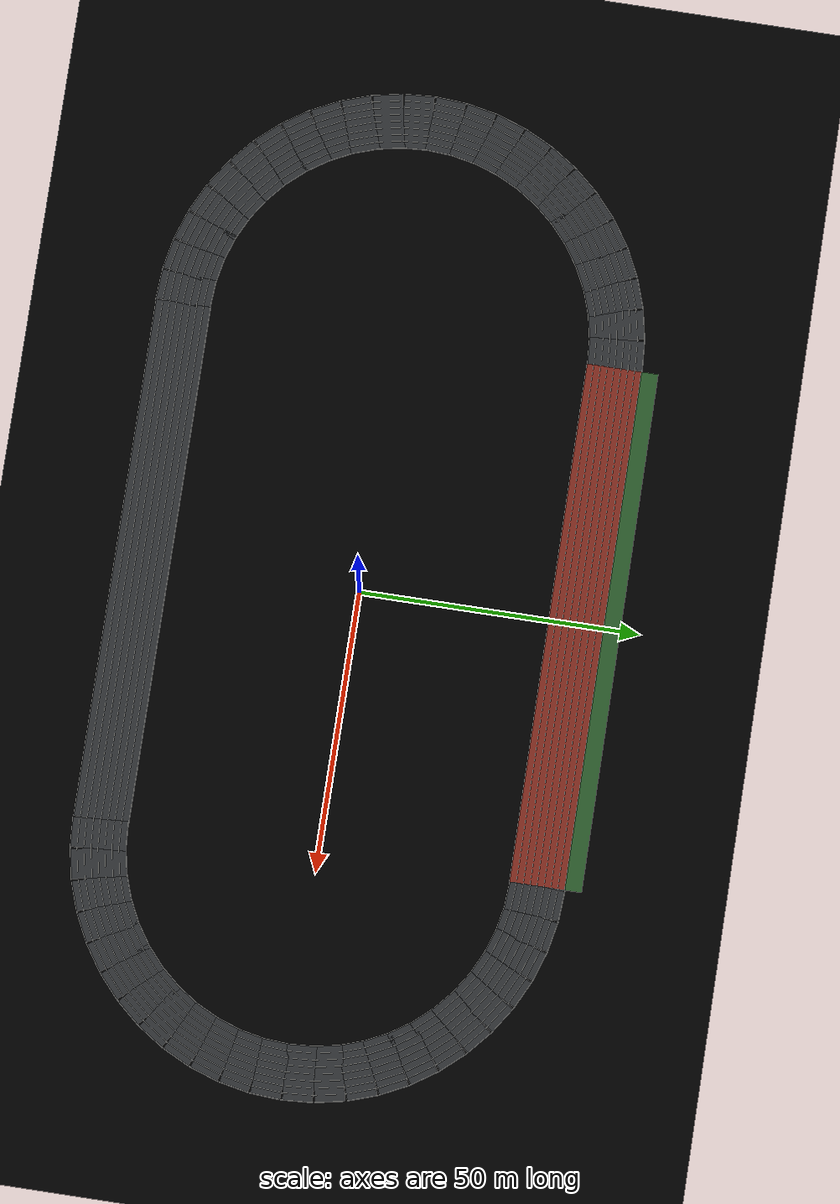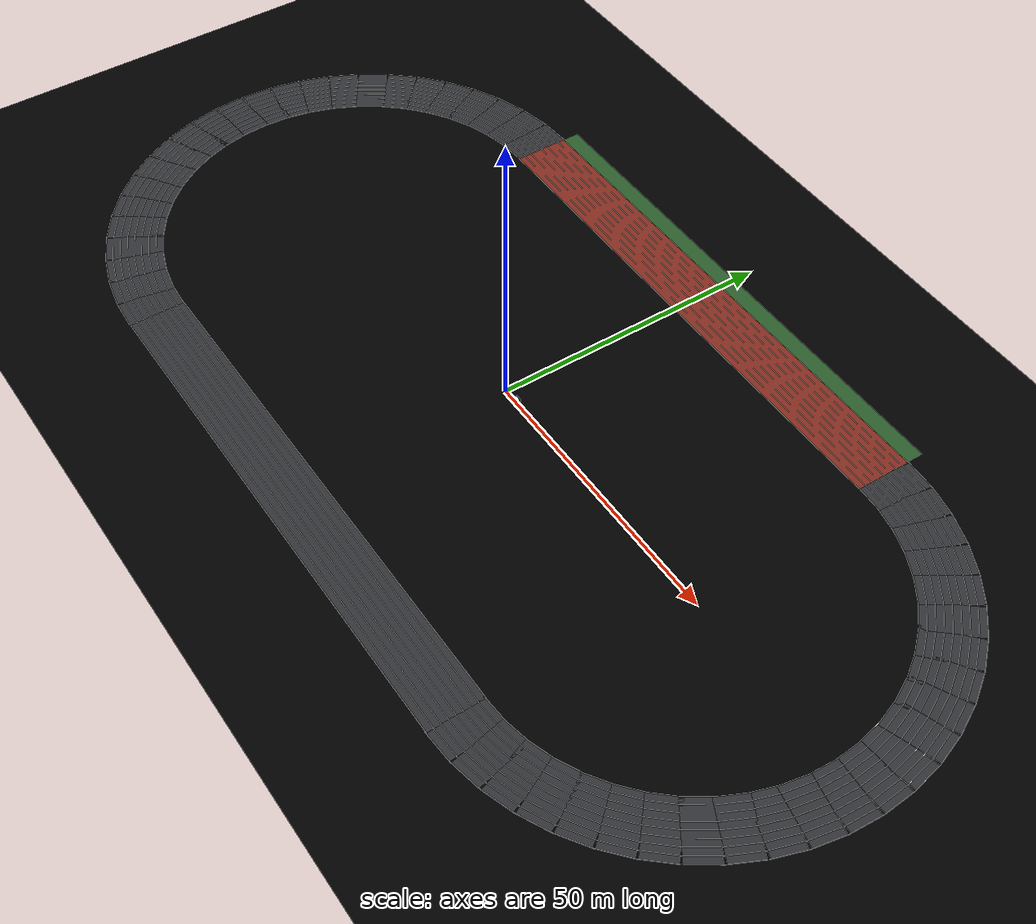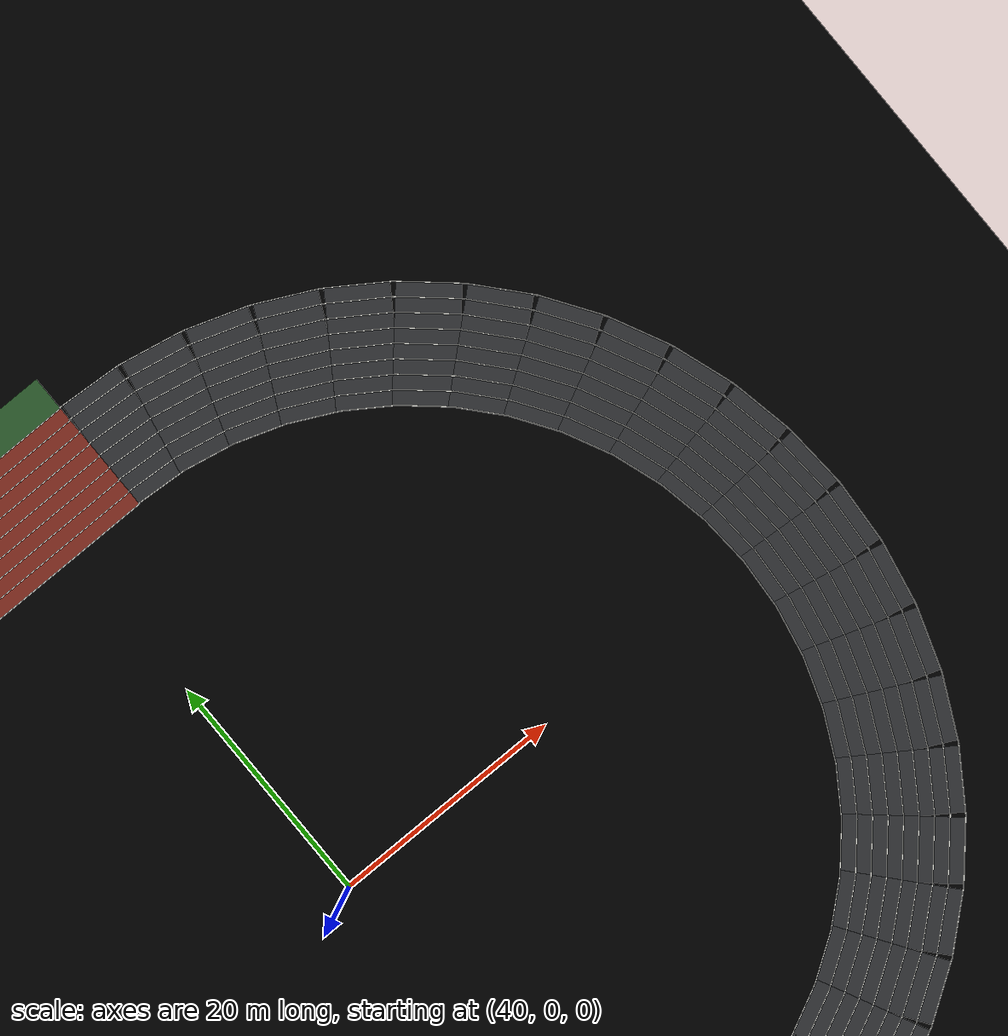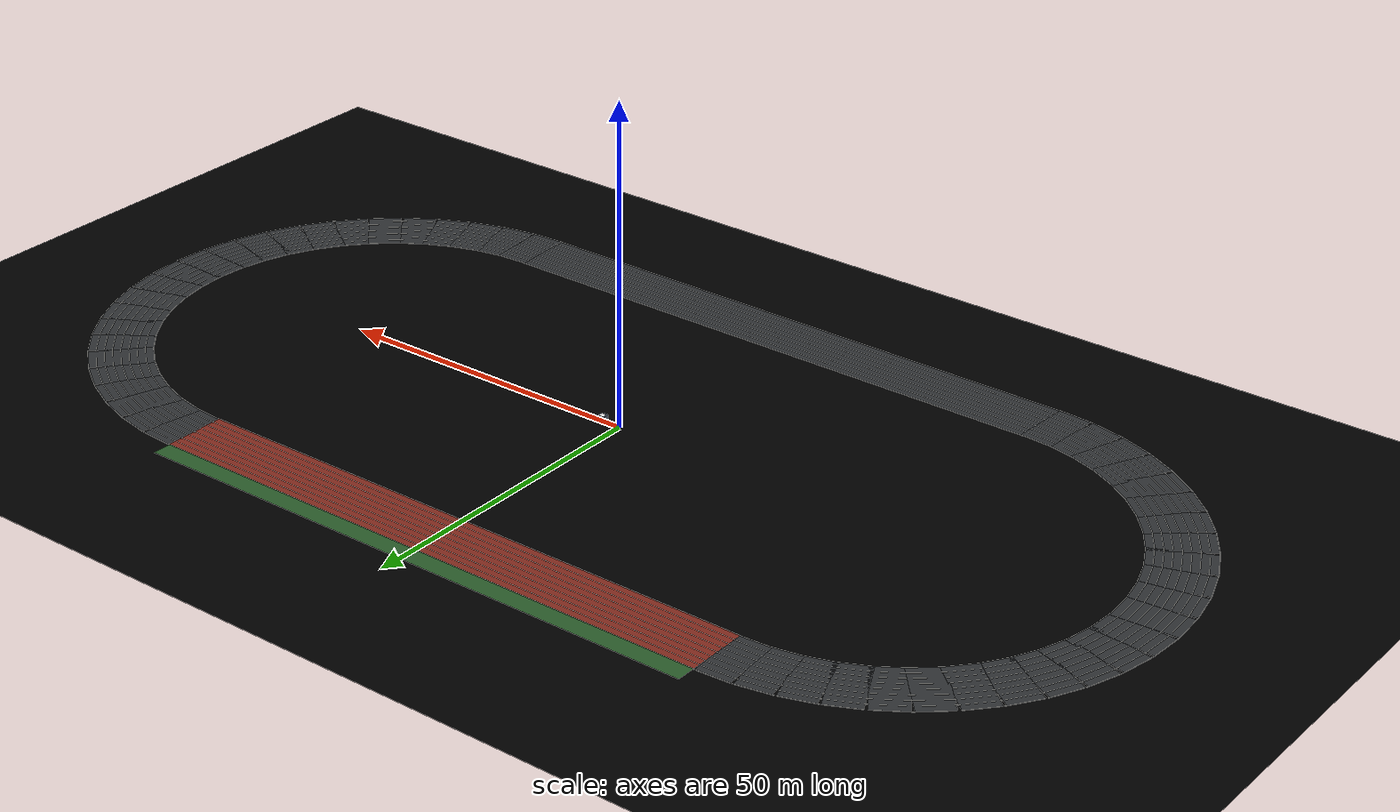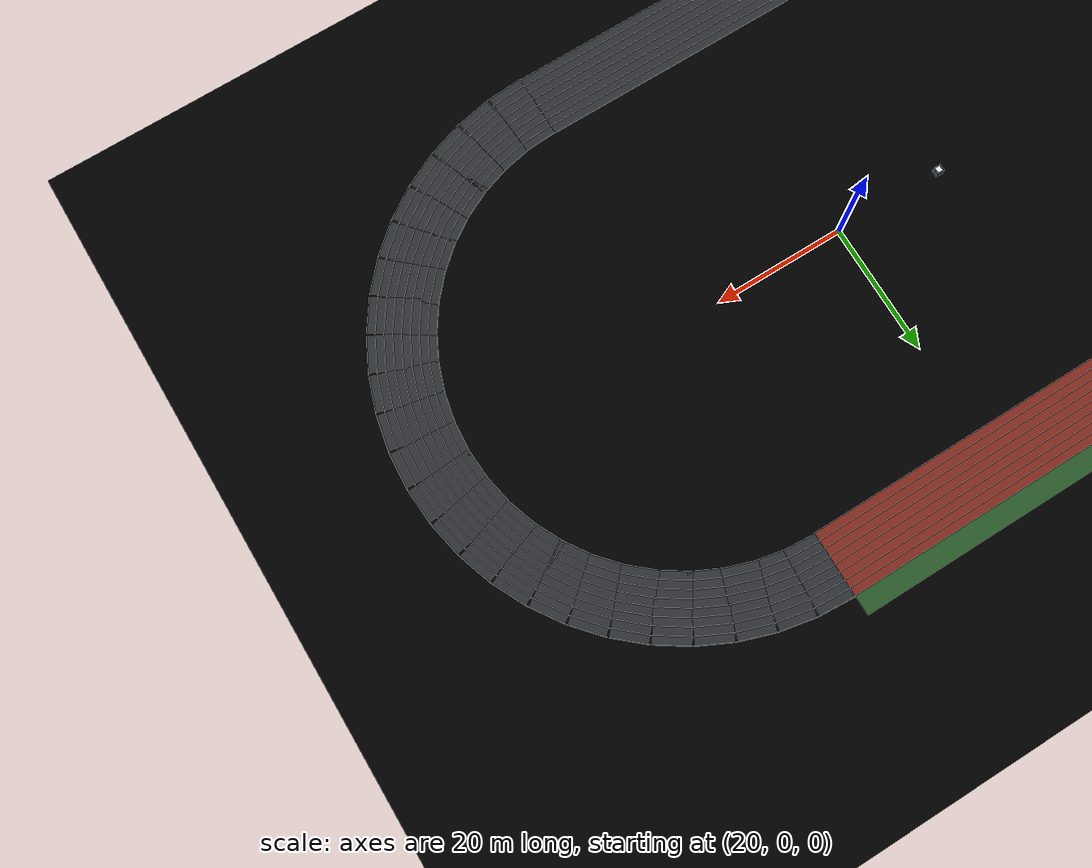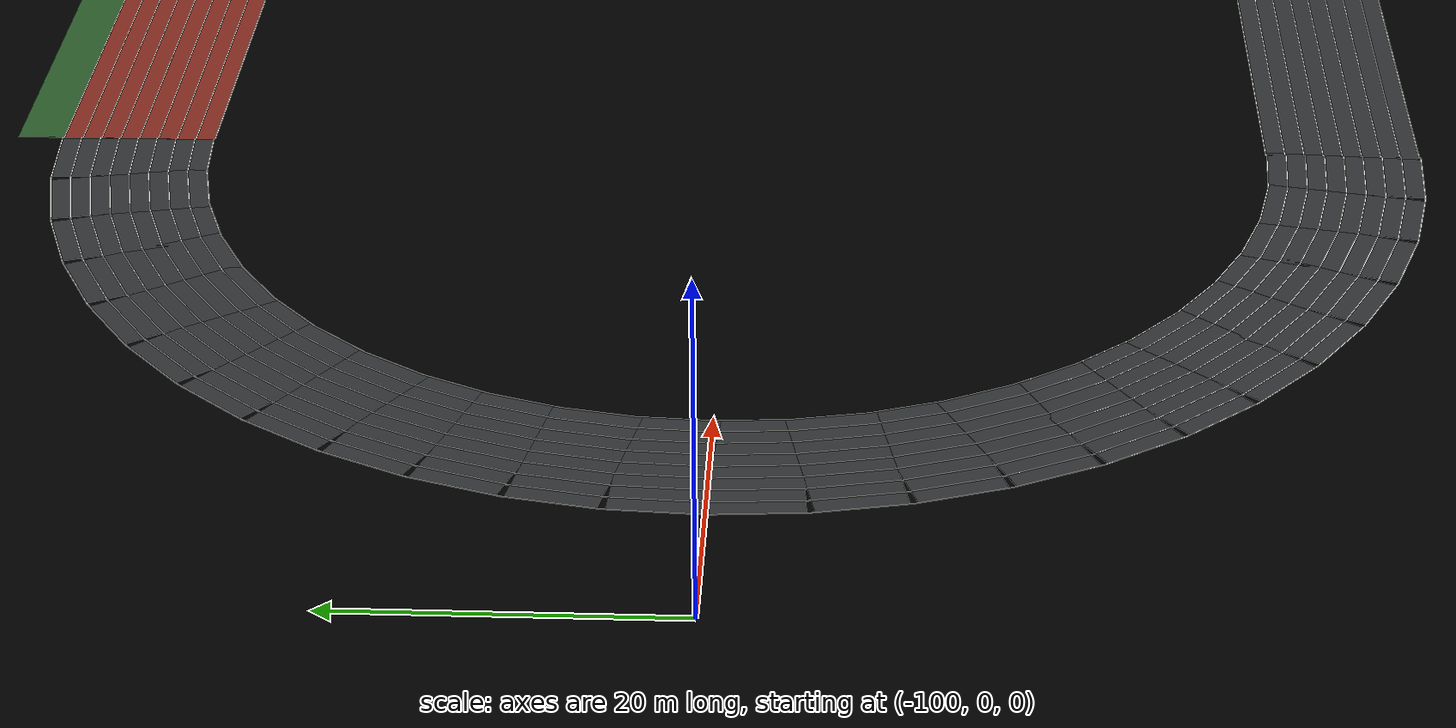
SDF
<sdf version="1.9">
 <world name="iris_down_camera_runway">
  <physics name="1ms" type="ignore">
   <max_step_size>0.001</max_step_size>
   <real_time_factor>1.0</real_time_factor>
  </physics>
  <plugin filename="gz-sim-physics-system" name="gz::sim::systems::Physics"/>
  <plugin filename="gz-sim-sensors-system" name="gz::sim::systems::Sensors">
   <render_engine>ogre2</render_engine>
  </plugin>
  <plugin filename="gz-sim-user-commands-system" name="gz::sim::systems::UserCommands"/>
  <plugin filename="gz-sim-scene-broadcaster-system" name="gz::sim::systems::SceneBroadcaster"/>
  <plugin filename="gz-sim-imu-system" name="gz::sim::systems::Imu"/>
  <plugin filename="gz-sim-navsat-system" name="gz::sim::systems::NavSat"/>
  <scene><ambient>1.0 1.0 1.0</ambient><background>0 0 0</background></scene>
  <spherical_coordinates>
   <latitude_deg>-35.363262</latitude_deg>
   <longitude_deg>149.165237</longitude_deg>
   <elevation>584</elevation>
   <heading_deg>0</heading_deg>
   <surface_model>EARTH_WGS84</surface_model>
  </spherical_coordinates>
  <light type="directional" name="sun">
   <pose>0 0 10 0 0 0</pose>
   <diffuse>0.8 0.8 0.8 1</diffuse>
   <specular>0.8 0.8 0.8 1</specular>
   <attenuation>
    <range>1000</range>
    <constant>0.9</constant>
    <linear>0.01</linear>
    <quadratic>0.001</quadratic>
   </attenuation>
   <direction>-0.5 0.1 -0.9</direction>
  </light>
  <model name="black_ground">
   <static>true</static>
   <pose>0 36.8 -0.001 0 0 0</pose>
   <link name="link">
    <visual name="visual">
     <geometry><box><size>2000 2000 0.01</size></box></geometry>
     <material>
      <ambient>0 0 0 1</ambient>
      <diffuse>0 0 0 1</diffuse>
      <specular>0 0 0 1</specular>
      <emissive>0 0 0 1</emissive>
     </material>
    </visual>
   </link>
  </model>
  <include><uri>model://running_track</uri></include>
  <include><uri>model://aruco_platform</uri><pose>3 0 0 0 0 0</pose></include>
 </world>
</sdf>

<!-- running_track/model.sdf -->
<sdf version="1.9">
  <!-- Generated by gen_track_model.py; edit the generator, not this file. -->
  <model name="running_track">
    <static>true</static>
    <link name="link">
      <visual name="track_surface_0">
        <pose>0.0000 -38.6500 0.0080 0 0 0.000000</pose>
        <cast_shadows>false</cast_shadows>
        <geometry>
          <box><size>92.9659 9.7600 0.0060</size></box>
        </geometry>
        <material>
          <ambient>0.2 0.21 0.22 1.0</ambient>
          <diffuse>0.2 0.21 0.22 1.0</diffuse>
          <specular>0.04 0.04 0.04 1</specular>
        </material>
      </visual>
      <visual name="track_surface_1">
        <pose>0.0000 38.6500 0.0080 0 0 3.141593</pose>
        <cast_shadows>false</cast_shadows>
        <geometry>
          <box><size>92.9659 9.7600 0.0060</size></box>
        </geometry>
        <material>
          <ambient>0.2 0.21 0.22 1.0</ambient>
          <diffuse>0.2 0.21 0.22 1.0</diffuse>
          <specular>0.04 0.04 0.04 1</specular>
        </material>
      </visual>
      <visual name="track_surface_2">
        <pose>49.0108 -38.5672 0.0080 0 0 0.065450</pose>
        <cast_shadows>false</cast_shadows>
        <geometry>
          <box><size>5.2579 9.7600 0.0060</size></box>
        </geometry>
        <material>
          <ambient>0.2 0.21 0.22 1.0</ambient>
          <diffuse>0.2 0.21 0.22 1.0</diffuse>
          <specular>0.04 0.04 0.04 1</specular>
        </material>
      </visual>
      <visual name="track_surface_3">
        <pose>54.0232 -37.9074 0.0080 0 0 0.196350</pose>
        <cast_shadows>false</cast_shadows>
        <geometry>
          <box><size>5.2579 9.7600 0.0060</size></box>
        </geometry>
        <material>
          <ambient>0.2 0.21 0.22 1.0</ambient>
          <diffuse>0.2 0.21 0.22 1.0</diffuse>
          <specular>0.04 0.04 0.04 1</specular>
        </material>
      </visual>
      <visual name="track_surface_4">
        <pose>58.9066 -36.5988 0.0080 0 0 0.327249</pose>
        <cast_shadows>false</cast_shadows>
        <geometry>
          <box><size>5.2579 9.7600 0.0060</size></box>
        </geometry>
        <material>
          <ambient>0.2 0.21 0.22 1.0</ambient>
          <diffuse>0.2 0.21 0.22 1.0</diffuse>
          <specular>0.04 0.04 0.04 1</specular>
        </material>
      </visual>
      <visual name="track_surface_5">
        <pose>63.5774 -34.6641 0.0080 0 0 0.458149</pose>
        <cast_shadows>false</cast_shadows>
        <geometry>
          <box><size>5.2579 9.7600 0.0060</size></box>
        </geometry>
        <material>
          <ambient>0.2 0.21 0.22 1.0</ambient>
          <diffuse>0.2 0.21 0.22 1.0</diffuse>
          <specular>0.04 0.04 0.04 1</specular>
        </material>
      </visual>
      <visual name="track_surface_6">
        <pose>67.9558 -32.1363 0.0080 0 0 0.589049</pose>
        <cast_shadows>false</cast_shadows>
        <geometry>
          <box><size>5.2579 9.7600 0.0060</size></box>
        </geometry>
        <material>
          <ambient>0.2 0.21 0.22 1.0</ambient>
          <diffuse>0.2 0.21 0.22 1.0</diffuse>
          <specular>0.04 0.04 0.04 1</specular>
        </material>
      </visual>
      <visual name="track_surface_7">
        <pose>71.9667 -29.0586 0.0080 0 0 0.719948</pose>
        <cast_shadows>false</cast_shadows>
        <geometry>
          <box><size>5.2579 9.7600 0.0060</size></box>
        </geometry>
        <material>
          <ambient>0.2 0.21 0.22 1.0</ambient>
          <diffuse>0.2 0.21 0.22 1.0</diffuse>
          <specular>0.04 0.04 0.04 1</specular>
        </material>
      </visual>
      <visual name="track_surface_8">
        <pose>75.5416 -25.4837 0.0080 0 0 0.850848</pose>
        <cast_shadows>false</cast_shadows>
        <geometry>
          <box><size>5.2579 9.7600 0.0060</size></box>
        </geometry>
        <material>
          <ambient>0.2 0.21 0.22 1.0</ambient>
          <diffuse>0.2 0.21 0.22 1.0</diffuse>
          <specular>0.04 0.04 0.04 1</specular>
        </material>
      </visual>
      <visual name="track_surface_9">
        <pose>78.6193 -21.4728 0.0080 0 0 0.981748</pose>
        <cast_shadows>false</cast_shadows>
        <geometry>
          <box><size>5.2579 9.7600 0.0060</size></box>
        </geometry>
        <material>
          <ambient>0.2 0.21 0.22 1.0</ambient>
          <diffuse>0.2 0.21 0.22 1.0</diffuse>
          <specular>0.04 0.04 0.04 1</specular>
        </material>
      </visual>
      <visual name="track_surface_10">
        <pose>81.1471 -17.0945 0.0080 0 0 1.112647</pose>
        <cast_shadows>false</cast_shadows>
        <geometry>
          <box><size>5.2579 9.7600 0.0060</size></box>
        </geometry>
        <material>
          <ambient>0.2 0.21 0.22 1.0</ambient>
          <diffuse>0.2 0.21 0.22 1.0</diffuse>
          <specular>0.04 0.04 0.04 1</specular>
        </material>
      </visual>
      <visual name="track_surface_11">
        <pose>83.0818 -12.4236 0.0080 0 0 1.243547</pose>
        <cast_shadows>false</cast_shadows>
        <geometry>
          <box><size>5.2579 9.7600 0.0060</size></box>
        </geometry>
        <material>
          <ambient>0.2 0.21 0.22 1.0</ambient>
          <diffuse>0.2 0.21 0.22 1.0</diffuse>
          <specular>0.04 0.04 0.04 1</specular>
        </material>
      </visual>
      <visual name="track_surface_12">
        <pose>84.3903 -7.5402 0.0080 0 0 1.374447</pose>
        <cast_shadows>false</cast_shadows>
        <geometry>
          <box><size>5.2579 9.7600 0.0060</size></box>
        </geometry>
        <material>
          <ambient>0.2 0.21 0.22 1.0</ambient>
          <diffuse>0.2 0.21 0.22 1.0</diffuse>
          <specular>0.04 0.04 0.04 1</specular>
        </material>
      </visual>
      <visual name="track_surface_13">
        <pose>85.0502 -2.5278 0.0080 0 0 1.505346</pose>
        <cast_shadows>false</cast_shadows>
        <geometry>
          <box><size>5.2579 9.7600 0.0060</size></box>
        </geometry>
        <material>
          <ambient>0.2 0.21 0.22 1.0</ambient>
          <diffuse>0.2 0.21 0.22 1.0</diffuse>
          <specular>0.04 0.04 0.04 1</specular>
        </material>
      </visual>
      <visual name="track_surface_14">
        <pose>85.0502 2.5278 0.0080 0 0 1.636246</pose>
        <cast_shadows>false</cast_shadows>
        <geometry>
          <box><size>5.2579 9.7600 0.0060</size></box>
        </geometry>
        <material>
          <ambient>0.2 0.21 0.22 1.0</ambient>
          <diffuse>0.2 0.21 0.22 1.0</diffuse>
          <specular>0.04 0.04 0.04 1</specular>
        </material>
      </visual>
      <visual name="track_surface_15">
        <pose>84.3903 7.5402 0.0080 0 0 1.767146</pose>
        <cast_shadows>false</cast_shadows>
        <geometry>
          <box><size>5.2579 9.7600 0.0060</size></box>
        </geometry>
        <material>
          <ambient>0.2 0.21 0.22 1.0</ambient>
          <diffuse>0.2 0.21 0.22 1.0</diffuse>
          <specular>0.04 0.04 0.04 1</specular>
        </material>
      </visual>
      <visual name="track_surface_16">
        <pose>83.0818 12.4236 0.0080 0 0 1.898046</pose>
        <cast_shadows>false</cast_shadows>
        <geometry>
          <box><size>5.2579 9.7600 0.0060</size></box>
        </geometry>
        <material>
          <ambient>0.2 0.21 0.22 1.0</ambient>
          <diffuse>0.2 0.21 0.22 1.0</diffuse>
          <specular>0.04 0.04 0.04 1</specular>
        </material>
      </visual>
      <visual name="track_surface_17">
        <pose>81.1471 17.0945 0.0080 0 0 2.028945</pose>
        <cast_shadows>false</cast_shadows>
        <geometry>
          <box><size>5.2579 9.7600 0.0060</size></box>
        </geometry>
        <material>
          <ambient>0.2 0.21 0.22 1.0</ambient>
          <diffuse>0.2 0.21 0.22 1.0</diffuse>
          <specular>0.04 0.04 0.04 1</specular>
        </material>
      </visual>
      <visual name="track_surface_18">
        <pose>78.6193 21.4728 0.0080 0 0 2.159845</pose>
        <cast_shadows>false</cast_shadows>
        <geometry>
          <box><size>5.2579 9.7600 0.0060</size></box>
        </geometry>
        <material>
          <ambient>0.2 0.21 0.22 1.0</ambient>
          <diffuse>0.2 0.21 0.22 1.0</diffuse>
          <specular>0.04 0.04 0.04 1</specular>
        </material>
      </visual>
      <visual name="track_surface_19">
        <pose>75.5416 25.4837 0.0080 0 0 2.290745</pose>
        <cast_shadows>false</cast_shadows>
        <geometry>
          <box><size>5.2579 9.7600 0.0060</size></box>
        </geometry>
        <material>
          <ambient>0.2 0.21 0.22 1.0</ambient>
          <diffuse>0.2 0.21 0.22 1.0</diffuse>
          <specular>0.04 0.04 0.04 1</specular>
        </material>
      </visual>
      <visual name="track_surface_20">
        <pose>71.9667 29.0586 0.0080 0 0 2.421644</pose>
        <cast_shadows>false</cast_shadows>
        <geometry>
          <box><size>5.2579 9.7600 0.0060</size></box>
        </geometry>
        <material>
          <ambient>0.2 0.21 0.22 1.0</ambient>
          <diffuse>0.2 0.21 0.22 1.0</diffuse>
          <specular>0.04 0.04 0.04 1</specular>
        </material>
      </visual>
      <visual name="track_surface_21">
        <pose>67.9558 32.1363 0.0080 0 0 2.552544</pose>
        <cast_shadows>false</cast_shadows>
        <geometry>
          <box><size>5.2579 9.7600 0.0060</size></box>
        </geometry>
        <material>
          <ambient>0.2 0.21 0.22 1.0</ambient>
          <diffuse>0.2 0.21 0.22 1.0</diffuse>
          <specular>0.04 0.04 0.04 1</specular>
        </material>
      </visual>
      <visual name="track_surface_22">
        <pose>63.5774 34.6641 0.0080 0 0 2.683444</pose>
        <cast_shadows>false</cast_shadows>
        <geometry>
          <box><size>5.2579 9.7600 0.0060</size></box>
        </geometry>
        <material>
          <ambient>0.2 0.21 0.22 1.0</ambient>
          <diffuse>0.2 0.21 0.22 1.0</diffuse>
          <specular>0.04 0.04 0.04 1</specular>
        </material>
      </visual>
      <visual name="track_surface_23">
        <pose>58.9066 36.5988 0.0080 0 0 2.814343</pose>
        <cast_shadows>false</cast_shadows>
        <geometry>
          <box><size>5.2579 9.7600 0.0060</size></box>
        </geometry>
        <material>
          <ambient>0.2 0.21 0.22 1.0</ambient>
          <diffuse>0.2 0.21 0.22 1.0</diffuse>
          <specular>0.04 0.04 0.04 1</specular>
        </material>
      </visual>
      <visual name="track_surface_24">
        <pose>54.0232 37.9074 0.0080 0 0 2.945243</pose>
        <cast_shadows>false</cast_shadows>
        <geometry>
          <box><size>5.2579 9.7600 0.0060</size></box>
        </geometry>
        <material>
          <ambient>0.2 0.21 0.22 1.0</ambient>
          <diffuse>0.2 0.21 0.22 1.0</diffuse>
          <specular>0.04 0.04 0.04 1</specular>
        </material>
      </visual>
      <visual name="track_surface_25">
        <pose>49.0108 38.5672 0.0080 0 0 3.076143</pose>
        <cast_shadows>false</cast_shadows>
        <geometry>
          <box><size>5.2579 9.7600 0.0060</size></box>
        </geometry>
        <material>
          <ambient>0.2 0.21 0.22 1.0</ambient>
          <diffuse>0.2 0.21 0.22 1.0</diffuse>
          <specular>0.04 0.04 0.04 1</specular>
        </material>
      </visual>
      <visual name="track_surface_26">
        <pose>-49.0108 38.5672 0.0080 0 0 3.207043</pose>
        <cast_shadows>false</cast_shadows>
        <geometry>
          <box><size>5.2579 9.7600 0.0060</size></box>
        </geometry>
        <material>
          <ambient>0.2 0.21 0.22 1.0</ambient>
          <diffuse>0.2 0.21 0.22 1.0</diffuse>
          <specular>0.04 0.04 0.04 1</specular>
        </material>
      </visual>
      <visual name="track_surface_27">
        <pose>-54.0232 37.9074 0.0080 0 0 3.337942</pose>
        <cast_shadows>false</cast_shadows>
        <geometry>
          <box><size>5.2579 9.7600 0.0060</size></box>
        </geometry>
        <material>
          <ambient>0.2 0.21 0.22 1.0</ambient>
          <diffuse>0.2 0.21 0.22 1.0</diffuse>
          <specular>0.04 0.04 0.04 1</specular>
        </material>
      </visual>
      <visual name="track_surface_28">
        <pose>-58.9066 36.5988 0.0080 0 0 3.468842</pose>
        <cast_shadows>false</cast_shadows>
        <geometry>
          <box><size>5.2579 9.7600 0.0060</size></box>
        </geometry>
        <material>
          <ambient>0.2 0.21 0.22 1.0</ambient>
          <diffuse>0.2 0.21 0.22 1.0</diffuse>
          <specular>0.04 0.04 0.04 1</specular>
        </material>
      </visual>
      <visual name="track_surface_29">
        <pose>-63.5774 34.6641 0.0080 0 0 3.599742</pose>
        <cast_shadows>false</cast_shadows>
        <geometry>
          <box><size>5.2579 9.7600 0.0060</size></box>
        </geometry>
        <material>
          <ambient>0.2 0.21 0.22 1.0</ambient>
          <diffuse>0.2 0.21 0.22 1.0</diffuse>
          <specular>0.04 0.04 0.04 1</specular>
        </material>
      </visual>
      <visual name="track_surface_30">
        <pose>-67.9558 32.1363 0.0080 0 0 3.730641</pose>
        <cast_shadows>false</cast_shadows>
        <geometry>
          <box><size>5.2579 9.7600 0.0060</size></box>
        </geometry>
        <material>
          <ambient>0.2 0.21 0.22 1.0</ambient>
          <diffuse>0.2 0.21 0.22 1.0</diffuse>
          <specular>0.04 0.04 0.04 1</specular>
        </material>
      </visual>
      <visual name="track_surface_31">
        <pose>-71.9667 29.0586 0.0080 0 0 3.861541</pose>
        <cast_shadows>false</cast_shadows>
        <geometry>
          <box><size>5.2579 9.7600 0.0060</size></box>
        </geometry>
        <material>
          <ambient>0.2 0.21 0.22 1.0</ambient>
          <diffuse>0.2 0.21 0.22 1.0</diffuse>
          <specular>0.04 0.04 0.04 1</specular>
        </material>
      </visual>
      <visual name="track_surface_32">
        <pose>-75.5416 25.4837 0.0080 0 0 3.992441</pose>
        <cast_shadows>false</cast_shadows>
        <geometry>
          <box><size>5.2579 9.7600 0.0060</size></box>
        </geometry>
        <material>
          <ambient>0.2 0.21 0.22 1.0</ambient>
          <diffuse>0.2 0.21 0.22 1.0</diffuse>
          <specular>0.04 0.04 0.04 1</specular>
        </material>
      </visual>
      <visual name="track_surface_33">
        <pose>-78.6193 21.4728 0.0080 0 0 4.123340</pose>
        <cast_shadows>false</cast_shadows>
        <geometry>
          <box><size>5.2579 9.7600 0.0060</size></box>
        </geometry>
        <material>
          <ambient>0.2 0.21 0.22 1.0</ambient>
          <diffuse>0.2 0.21 0.22 1.0</diffuse>
          <specular>0.04 0.04 0.04 1</specular>
        </material>
      </visual>
      <visual name="track_surface_34">
        <pose>-81.1471 17.0945 0.0080 0 0 4.254240</pose>
        <cast_shadows>false</cast_shadows>
        <geometry>
          <box><size>5.2579 9.7600 0.0060</size></box>
        </geometry>
        <material>
          <ambient>0.2 0.21 0.22 1.0</ambient>
          <diffuse>0.2 0.21 0.22 1.0</diffuse>
          <specular>0.04 0.04 0.04 1</specular>
        </material>
      </visual>
      <visual name="track_surface_35">
        <pose>-83.0818 12.4236 0.0080 0 0 4.385140</pose>
        <cast_shadows>false</cast_shadows>
        <geometry>
          <box><size>5.2579 9.7600 0.0060</size></box>
        </geometry>
        <material>
          <ambient>0.2 0.21 0.22 1.0</ambient>
          <diffuse>0.2 0.21 0.22 1.0</diffuse>
          <specular>0.04 0.04 0.04 1</specular>
        </material>
      </visual>
      <visual name="track_surface_36">
        <pose>-84.3903 7.5402 0.0080 0 0 4.516039</pose>
        <cast_shadows>false</cast_shadows>
        <geometry>
          <box><size>5.2579 9.7600 0.0060</size></box>
        </geometry>
        <material>
          <ambient>0.2 0.21 0.22 1.0</ambient>
          <diffuse>0.2 0.21 0.22 1.0</diffuse>
          <specular>0.04 0.04 0.04 1</specular>
        </material>
      </visual>
      <visual name="track_surface_37">
        <pose>-85.0502 2.5278 0.0080 0 0 4.646939</pose>
        <cast_shadows>false</cast_shadows>
        <geometry>
          <box><size>5.2579 9.7600 0.0060</size></box>
        </geometry>
        <material>
          <ambient>0.2 0.21 0.22 1.0</ambient>
          <diffuse>0.2 0.21 0.22 1.0</diffuse>
          <specular>0.04 0.04 0.04 1</specular>
        </material>
      </visual>
      <visual name="track_surface_38">
        <pose>-85.0502 -2.5278 0.0080 0 0 4.777839</pose>
        <cast_shadows>false</cast_shadows>
        <geometry>
          <box><size>5.2579 9.7600 0.0060</size></box>
        </geometry>
        <material>
          <ambient>0.2 0.21 0.22 1.0</ambient>
          <diffuse>0.2 0.21 0.22 1.0</diffuse>
          <specular>0.04 0.04 0.04 1</specular>
        </material>
      </visual>
      <visual name="track_surface_39">
        <pose>-84.3903 -7.5402 0.0080 0 0 4.908739</pose>
        <cast_shadows>false</cast_shadows>
        <geometry>
          <box><size>5.2579 9.7600 0.0060</size></box>
        </geometry>
        <material>
          <ambient>0.2 0.21 0.22 1.0</ambient>
          <diffuse>0.2 0.21 0.22 1.0</diffuse>
          <specular>0.04 0.04 0.04 1</specular>
        </material>
      </visual>
      <visual name="track_surface_40">
        <pose>-83.0818 -12.4236 0.0080 0 0 5.039638</pose>
        <cast_shadows>false</cast_shadows>
        <geometry>
          <box><size>5.2579 9.7600 0.0060</size></box>
        </geometry>
        <material>
          <ambient>0.2 0.21 0.22 1.0</ambient>
          <diffuse>0.2 0.21 0.22 1.0</diffuse>
          <specular>0.04 0.04 0.04 1</specular>
        </material>
      </visual>
      <visual name="track_surface_41">
        <pose>-81.1471 -17.0945 0.0080 0 0 5.170538</pose>
        <cast_shadows>false</cast_shadows>
        <geometry>
          <box><size>5.2579 9.7600 0.0060</size></box>
        </geometry>
        <material>
          <ambient>0.2 0.21 0.22 1.0</ambient>
          <diffuse>0.2 0.21 0.22 1.0</diffuse>
          <specular>0.04 0.04 0.04 1</specular>
        </material>
      </visual>
      <visual name="track_surface_42">
        <pose>-78.6193 -21.4728 0.0080 0 0 5.301438</pose>
        <cast_shadows>false</cast_shadows>
        <geometry>
          <box><size>5.2579 9.7600 0.0060</size></box>
        </geometry>
        <material>
          <ambient>0.2 0.21 0.22 1.0</ambient>
          <diffuse>0.2 0.21 0.22 1.0</diffuse>
          <specular>0.04 0.04 0.04 1</specular>
        </material>
      </visual>
      <visual name="track_surface_43">
        <pose>-75.5416 -25.4837 0.0080 0 0 5.432337</pose>
        <cast_shadows>false</cast_shadows>
        <geometry>
          <box><size>5.2579 9.7600 0.0060</size></box>
        </geometry>
        <material>
          <ambient>0.2 0.21 0.22 1.0</ambient>
          <diffuse>0.2 0.21 0.22 1.0</diffuse>
          <specular>0.04 0.04 0.04 1</specular>
        </material>
      </visual>
      <visual name="track_surface_44">
        <pose>-71.9667 -29.0586 0.0080 0 0 5.563237</pose>
        <cast_shadows>false</cast_shadows>
        <geometry>
          <box><size>5.2579 9.7600 0.0060</size></box>
        </geometry>
        <material>
          <ambient>0.2 0.21 0.22 1.0</ambient>
          <diffuse>0.2 0.21 0.22 1.0</diffuse>
          <specular>0.04 0.04 0.04 1</specular>
        </material>
      </visual>
      <visual name="track_surface_45">
        <pose>-67.9558 -32.1363 0.0080 0 0 5.694137</pose>
        <cast_shadows>false</cast_shadows>
        <geometry>
          <box><size>5.2579 9.7600 0.0060</size></box>
        </geometry>
        <material>
          <ambient>0.2 0.21 0.22 1.0</ambient>
          <diffuse>0.2 0.21 0.22 1.0</diffuse>
          <specular>0.04 0.04 0.04 1</specular>
        </material>
      </visual>
      <visual name="track_surface_46">
        <pose>-63.5774 -34.6641 0.0080 0 0 5.825036</pose>
        <cast_shadows>false</cast_shadows>
        <geometry>
          <box><size>5.2579 9.7600 0.0060</size></box>
        </geometry>
        <material>
          <ambient>0.2 0.21 0.22 1.0</ambient>
          <diffuse>0.2 0.21 0.22 1.0</diffuse>
          <specular>0.04 0.04 0.04 1</specular>
        </material>
      </visual>
      <visual name="track_surface_47">
        <pose>-58.9066 -36.5988 0.0080 0 0 5.955936</pose>
        <cast_shadows>false</cast_shadows>
        <geometry>
          <box><size>5.2579 9.7600 0.0060</size></box>
        </geometry>
        <material>
          <ambient>0.2 0.21 0.22 1.0</ambient>
          <diffuse>0.2 0.21 0.22 1.0</diffuse>
          <specular>0.04 0.04 0.04 1</specular>
        </material>
      </visual>
      <visual name="track_surface_48">
        <pose>-54.0232 -37.9074 0.0080 0 0 6.086836</pose>
        <cast_shadows>false</cast_shadows>
        <geometry>
          <box><size>5.2579 9.7600 0.0060</size></box>
        </geometry>
        <material>
          <ambient>0.2 0.21 0.22 1.0</ambient>
          <diffuse>0.2 0.21 0.22 1.0</diffuse>
          <specular>0.04 0.04 0.04 1</specular>
        </material>
      </visual>
      <visual name="track_surface_49">
        <pose>-49.0108 -38.5672 0.0080 0 0 6.217735</pose>
        <cast_shadows>false</cast_shadows>
        <geometry>
          <box><size>5.2579 9.7600 0.0060</size></box>
        </geometry>
        <material>
          <ambient>0.2 0.21 0.22 1.0</ambient>
          <diffuse>0.2 0.21 0.22 1.0</diffuse>
          <specular>0.04 0.04 0.04 1</specular>
        </material>
      </visual>
      <visual name="red_home_straight">
        <pose>0.0000 38.6500 0.0120 0 0 0.000000</pose>
        <cast_shadows>false</cast_shadows>
        <geometry>
          <box><size>92.9659 9.7600 0.0040</size></box>
        </geometry>
        <material>
          <ambient>0.54 0.18 0.13 1.0</ambient>
          <diffuse>0.54 0.18 0.13 1.0</diffuse>
          <specular>0.04 0.04 0.04 1</specular>
        </material>
      </visual>
      <visual name="green_home_apron">
        <pose>0.0000 45.0300 0.0080 0 0 0.000000</pose>
        <cast_shadows>false</cast_shadows>
        <geometry>
          <box><size>92.9659 3.0000 0.0060</size></box>
        </geometry>
        <material>
          <ambient>0.18 0.38 0.18 1.0</ambient>
          <diffuse>0.18 0.38 0.18 1.0</diffuse>
          <specular>0.04 0.04 0.04 1</specular>
        </material>
      </visual>
      <visual name="lane_0_0">
        <pose>0.0000 -43.5300 0.0165 0 0 0.000000</pose>
        <cast_shadows>false</cast_shadows>
        <geometry>
          <box><size>92.9659 0.0800 0.0030</size></box>
        </geometry>
        <material>
          <ambient>0.94 0.94 0.91 1.0</ambient>
          <diffuse>0.94 0.94 0.91 1.0</diffuse>
          <specular>0.04 0.04 0.04 1</specular>
        </material>
      </visual>
      <visual name="lane_0_1">
        <pose>0.0000 43.5300 0.0165 0 0 3.141593</pose>
        <cast_shadows>false</cast_shadows>
        <geometry>
          <box><size>92.9659 0.0800 0.0030</size></box>
        </geometry>
        <material>
          <ambient>0.94 0.94 0.91 1.0</ambient>
          <diffuse>0.94 0.94 0.91 1.0</diffuse>
          <specular>0.04 0.04 0.04 1</specular>
        </material>
      </visual>
      <visual name="lane_0_2">
        <pose>49.3300 -43.4368 0.0165 0 0 0.065450</pose>
        <cast_shadows>false</cast_shadows>
        <geometry>
          <box><size>5.9218 0.0800 0.0030</size></box>
        </geometry>
        <material>
          <ambient>0.94 0.94 0.91 1.0</ambient>
          <diffuse>0.94 0.94 0.91 1.0</diffuse>
          <specular>0.04 0.04 0.04 1</specular>
        </material>
      </visual>
      <visual name="lane_0_3">
        <pose>54.9753 -42.6936 0.0165 0 0 0.196350</pose>
        <cast_shadows>false</cast_shadows>
        <geometry>
          <box><size>5.9218 0.0800 0.0030</size></box>
        </geometry>
        <material>
          <ambient>0.94 0.94 0.91 1.0</ambient>
          <diffuse>0.94 0.94 0.91 1.0</diffuse>
          <specular>0.04 0.04 0.04 1</specular>
        </material>
      </visual>
      <visual name="lane_0_4">
        <pose>60.4752 -41.2199 0.0165 0 0 0.327249</pose>
        <cast_shadows>false</cast_shadows>
        <geometry>
          <box><size>5.9218 0.0800 0.0030</size></box>
        </geometry>
        <material>
          <ambient>0.94 0.94 0.91 1.0</ambient>
          <diffuse>0.94 0.94 0.91 1.0</diffuse>
          <specular>0.04 0.04 0.04 1</specular>
        </material>
      </visual>
      <visual name="lane_0_5">
        <pose>65.7358 -39.0409 0.0165 0 0 0.458149</pose>
        <cast_shadows>false</cast_shadows>
        <geometry>
          <box><size>5.9218 0.0800 0.0030</size></box>
        </geometry>
        <material>
          <ambient>0.94 0.94 0.91 1.0</ambient>
          <diffuse>0.94 0.94 0.91 1.0</diffuse>
          <specular>0.04 0.04 0.04 1</specular>
        </material>
      </visual>
      <visual name="lane_0_6">
        <pose>70.6669 -36.1939 0.0165 0 0 0.589049</pose>
        <cast_shadows>false</cast_shadows>
        <geometry>
          <box><size>5.9218 0.0800 0.0030</size></box>
        </geometry>
        <material>
          <ambient>0.94 0.94 0.91 1.0</ambient>
          <diffuse>0.94 0.94 0.91 1.0</diffuse>
          <specular>0.04 0.04 0.04 1</specular>
        </material>
      </visual>
      <visual name="lane_0_7">
        <pose>75.1843 -32.7276 0.0165 0 0 0.719948</pose>
        <cast_shadows>false</cast_shadows>
        <geometry>
          <box><size>5.9218 0.0800 0.0030</size></box>
        </geometry>
        <material>
          <ambient>0.94 0.94 0.91 1.0</ambient>
          <diffuse>0.94 0.94 0.91 1.0</diffuse>
          <specular>0.04 0.04 0.04 1</specular>
        </material>
      </visual>
      <visual name="lane_0_8">
        <pose>79.2106 -28.7013 0.0165 0 0 0.850848</pose>
        <cast_shadows>false</cast_shadows>
        <geometry>
          <box><size>5.9218 0.0800 0.0030</size></box>
        </geometry>
        <material>
          <ambient>0.94 0.94 0.91 1.0</ambient>
          <diffuse>0.94 0.94 0.91 1.0</diffuse>
          <specular>0.04 0.04 0.04 1</specular>
        </material>
      </visual>
      <visual name="lane_0_9">
        <pose>82.6768 -24.1840 0.0165 0 0 0.981748</pose>
        <cast_shadows>false</cast_shadows>
        <geometry>
          <box><size>5.9218 0.0800 0.0030</size></box>
        </geometry>
        <material>
          <ambient>0.94 0.94 0.91 1.0</ambient>
          <diffuse>0.94 0.94 0.91 1.0</diffuse>
          <specular>0.04 0.04 0.04 1</specular>
        </material>
      </visual>
      <visual name="lane_0_10">
        <pose>85.5238 -19.2528 0.0165 0 0 1.112647</pose>
        <cast_shadows>false</cast_shadows>
        <geometry>
          <box><size>5.9218 0.0800 0.0030</size></box>
        </geometry>
        <material>
          <ambient>0.94 0.94 0.91 1.0</ambient>
          <diffuse>0.94 0.94 0.91 1.0</diffuse>
          <specular>0.04 0.04 0.04 1</specular>
        </material>
      </visual>
      <visual name="lane_0_11">
        <pose>87.7028 -13.9923 0.0165 0 0 1.243547</pose>
        <cast_shadows>false</cast_shadows>
        <geometry>
          <box><size>5.9218 0.0800 0.0030</size></box>
        </geometry>
        <material>
          <ambient>0.94 0.94 0.91 1.0</ambient>
          <diffuse>0.94 0.94 0.91 1.0</diffuse>
          <specular>0.04 0.04 0.04 1</specular>
        </material>
      </visual>
      <visual name="lane_0_12">
        <pose>89.1766 -8.4923 0.0165 0 0 1.374447</pose>
        <cast_shadows>false</cast_shadows>
        <geometry>
          <box><size>5.9218 0.0800 0.0030</size></box>
        </geometry>
        <material>
          <ambient>0.94 0.94 0.91 1.0</ambient>
          <diffuse>0.94 0.94 0.91 1.0</diffuse>
          <specular>0.04 0.04 0.04 1</specular>
        </material>
      </visual>
      <visual name="lane_0_13">
        <pose>89.9198 -2.8470 0.0165 0 0 1.505346</pose>
        <cast_shadows>false</cast_shadows>
        <geometry>
          <box><size>5.9218 0.0800 0.0030</size></box>
        </geometry>
        <material>
          <ambient>0.94 0.94 0.91 1.0</ambient>
          <diffuse>0.94 0.94 0.91 1.0</diffuse>
          <specular>0.04 0.04 0.04 1</specular>
        </material>
      </visual>
      <visual name="lane_0_14">
        <pose>89.9198 2.8470 0.0165 0 0 1.636246</pose>
        <cast_shadows>false</cast_shadows>
        <geometry>
          <box><size>5.9218 0.0800 0.0030</size></box>
        </geometry>
        <material>
          <ambient>0.94 0.94 0.91 1.0</ambient>
          <diffuse>0.94 0.94 0.91 1.0</diffuse>
          <specular>0.04 0.04 0.04 1</specular>
        </material>
      </visual>
      <visual name="lane_0_15">
        <pose>89.1766 8.4923 0.0165 0 0 1.767146</pose>
        <cast_shadows>false</cast_shadows>
        <geometry>
          <box><size>5.9218 0.0800 0.0030</size></box>
        </geometry>
        <material>
          <ambient>0.94 0.94 0.91 1.0</ambient>
          <diffuse>0.94 0.94 0.91 1.0</diffuse>
          <specular>0.04 0.04 0.04 1</specular>
        </material>
      </visual>
      <visual name="lane_0_16">
        <pose>87.7028 13.9923 0.0165 0 0 1.898046</pose>
        <cast_shadows>false</cast_shadows>
        <geometry>
          <box><size>5.9218 0.0800 0.0030</size></box>
        </geometry>
        <material>
          <ambient>0.94 0.94 0.91 1.0</ambient>
          <diffuse>0.94 0.94 0.91 1.0</diffuse>
          <specular>0.04 0.04 0.04 1</specular>
        </material>
      </visual>
      <visual name="lane_0_17">
        <pose>85.5238 19.2528 0.0165 0 0 2.028945</pose>
        <cast_shadows>false</cast_shadows>
        <geometry>
          <box><size>5.9218 0.0800 0.0030</size></box>
        </geometry>
        <material>
          <ambient>0.94 0.94 0.91 1.0</ambient>
          <diffuse>0.94 0.94 0.91 1.0</diffuse>
          <specular>0.04 0.04 0.04 1</specular>
        </material>
      </visual>
      <visual name="lane_0_18">
        <pose>82.6768 24.1840 0.0165 0 0 2.159845</pose>
        <cast_shadows>false</cast_shadows>
        <geometry>
          <box><size>5.9218 0.0800 0.0030</size></box>
        </geometry>
        <material>
          <ambient>0.94 0.94 0.91 1.0</ambient>
          <diffuse>0.94 0.94 0.91 1.0</diffuse>
          <specular>0.04 0.04 0.04 1</specular>
        </material>
      </visual>
      <visual name="lane_0_19">
        <pose>79.2106 28.7013 0.0165 0 0 2.290745</pose>
        <cast_shadows>false</cast_shadows>
        <geometry>
          <box><size>5.9218 0.0800 0.0030</size></box>
        </geometry>
        <material>
          <ambient>0.94 0.94 0.91 1.0</ambient>
          <diffuse>0.94 0.94 0.91 1.0</diffuse>
          <specular>0.04 0.04 0.04 1</specular>
        </material>
      </visual>
      <visual name="lane_0_20">
        <pose>75.1843 32.7276 0.0165 0 0 2.421644</pose>
        <cast_shadows>false</cast_shadows>
        <geometry>
          <box><size>5.9218 0.0800 0.0030</size></box>
        </geometry>
        <material>
          <ambient>0.94 0.94 0.91 1.0</ambient>
          <diffuse>0.94 0.94 0.91 1.0</diffuse>
          <specular>0.04 0.04 0.04 1</specular>
        </material>
      </visual>
      <visual name="lane_0_21">
        <pose>70.6669 36.1939 0.0165 0 0 2.552544</pose>
        <cast_shadows>false</cast_shadows>
        <geometry>
          <box><size>5.9218 0.0800 0.0030</size></box>
        </geometry>
        <material>
          <ambient>0.94 0.94 0.91 1.0</ambient>
          <diffuse>0.94 0.94 0.91 1.0</diffuse>
          <specular>0.04 0.04 0.04 1</specular>
        </material>
      </visual>
      <visual name="lane_0_22">
        <pose>65.7358 39.0409 0.0165 0 0 2.683444</pose>
        <cast_shadows>false</cast_shadows>
        <geometry>
          <box><size>5.9218 0.0800 0.0030</size></box>
        </geometry>
        <material>
          <ambient>0.94 0.94 0.91 1.0</ambient>
          <diffuse>0.94 0.94 0.91 1.0</diffuse>
          <specular>0.04 0.04 0.04 1</specular>
        </material>
      </visual>
      <visual name="lane_0_23">
        <pose>60.4752 41.2199 0.0165 0 0 2.814343</pose>
        <cast_shadows>false</cast_shadows>
        <geometry>
          <box><size>5.9218 0.0800 0.0030</size></box>
        </geometry>
        <material>
          <ambient>0.94 0.94 0.91 1.0</ambient>
          <diffuse>0.94 0.94 0.91 1.0</diffuse>
          <specular>0.04 0.04 0.04 1</specular>
        </material>
      </visual>
      <visual name="lane_0_24">
        <pose>54.9753 42.6936 0.0165 0 0 2.945243</pose>
        <cast_shadows>false</cast_shadows>
        <geometry>
          <box><size>5.9218 0.0800 0.0030</size></box>
        </geometry>
        <material>
          <ambient>0.94 0.94 0.91 1.0</ambient>
          <diffuse>0.94 0.94 0.91 1.0</diffuse>
          <specular>0.04 0.04 0.04 1</specular>
        </material>
      </visual>
      <visual name="lane_0_25">
        <pose>49.3300 43.4368 0.0165 0 0 3.076143</pose>
        <cast_shadows>false</cast_shadows>
        <geometry>
          <box><size>5.9218 0.0800 0.0030</size></box>
        </geometry>
        <material>
          <ambient>0.94 0.94 0.91 1.0</ambient>
          <diffuse>0.94 0.94 0.91 1.0</diffuse>
          <specular>0.04 0.04 0.04 1</specular>
        </material>
      </visual>
      <visual name="lane_0_26">
        <pose>-49.3300 43.4368 0.0165 0 0 3.207043</pose>
        <cast_shadows>false</cast_shadows>
        <geometry>
          <box><size>5.9218 0.0800 0.0030</size></box>
        </geometry>
        <material>
          <ambient>0.94 0.94 0.91 1.0</ambient>
          <diffuse>0.94 0.94 0.91 1.0</diffuse>
          <specular>0.04 0.04 0.04 1</specular>
        </material>
      </visual>
      <visual name="lane_0_27">
        <pose>-54.9753 42.6936 0.0165 0 0 3.337942</pose>
        <cast_shadows>false</cast_shadows>
        <geometry>
          <box><size>5.9218 0.0800 0.0030</size></box>
        </geometry>
        <material>
          <ambient>0.94 0.94 0.91 1.0</ambient>
          <diffuse>0.94 0.94 0.91 1.0</diffuse>
          <specular>0.04 0.04 0.04 1</specular>
        </material>
      </visual>
      <visual name="lane_0_28">
        <pose>-60.4752 41.2199 0.0165 0 0 3.468842</pose>
        <cast_shadows>false</cast_shadows>
        <geometry>
          <box><size>5.9218 0.0800 0.0030</size></box>
        </geometry>
        <material>
          <ambient>0.94 0.94 0.91 1.0</ambient>
          <diffuse>0.94 0.94 0.91 1.0</diffuse>
          <specular>0.04 0.04 0.04 1</specular>
        </material>
      </visual>
      <visual name="lane_0_29">
        <pose>-65.7358 39.0409 0.0165 0 0 3.599742</pose>
        <cast_shadows>false</cast_shadows>
        <geometry>
          <box><size>5.9218 0.0800 0.0030</size></box>
        </geometry>
        <material>
          <ambient>0.94 0.94 0.91 1.0</ambient>
          <diffuse>0.94 0.94 0.91 1.0</diffuse>
          <specular>0.04 0.04 0.04 1</specular>
        </material>
      </visual>
      <visual name="lane_0_30">
        <pose>-70.6669 36.1939 0.0165 0 0 3.730641</pose>
        <cast_shadows>false</cast_shadows>
        <geometry>
          <box><size>5.9218 0.0800 0.0030</size></box>
        </geometry>
        <material>
          <ambient>0.94 0.94 0.91 1.0</ambient>
          <diffuse>0.94 0.94 0.91 1.0</diffuse>
          <specular>0.04 0.04 0.04 1</specular>
        </material>
      </visual>
      <visual name="lane_0_31">
        <pose>-75.1843 32.7276 0.0165 0 0 3.861541</pose>
        <cast_shadows>false</cast_shadows>
        <geometry>
          <box><size>5.9218 0.0800 0.0030</size></box>
        </geometry>
        <material>
          <ambient>0.94 0.94 0.91 1.0</ambient>
          <diffuse>0.94 0.94 0.91 1.0</diffuse>
          <specular>0.04 0.04 0.04 1</specular>
        </material>
      </visual>
      <visual name="lane_0_32">
        <pose>-79.2106 28.7013 0.0165 0 0 3.992441</pose>
        <cast_shadows>false</cast_shadows>
        <geometry>
          <box><size>5.9218 0.0800 0.0030</size></box>
        </geometry>
        <material>
          <ambient>0.94 0.94 0.91 1.0</ambient>
          <diffuse>0.94 0.94 0.91 1.0</diffuse>
          <specular>0.04 0.04 0.04 1</specular>
        </material>
      </visual>
      <visual name="lane_0_33">
        <pose>-82.6768 24.1840 0.0165 0 0 4.123340</pose>
        <cast_shadows>false</cast_shadows>
        <geometry>
          <box><size>5.9218 0.0800 0.0030</size></box>
        </geometry>
        <material>
          <ambient>0.94 0.94 0.91 1.0</ambient>
          <diffuse>0.94 0.94 0.91 1.0</diffuse>
          <specular>0.04 0.04 0.04 1</specular>
        </material>
      </visual>
      <visual name="lane_0_34">
        <pose>-85.5238 19.2528 0.0165 0 0 4.254240</pose>
        <cast_shadows>false</cast_shadows>
        <geometry>
          <box><size>5.9218 0.0800 0.0030</size></box>
        </geometry>
        <material>
          <ambient>0.94 0.94 0.91 1.0</ambient>
          <diffuse>0.94 0.94 0.91 1.0</diffuse>
          <specular>0.04 0.04 0.04 1</specular>
        </material>
      </visual>
      <visual name="lane_0_35">
        <pose>-87.7028 13.9923 0.0165 0 0 4.385140</pose>
        <cast_shadows>false</cast_shadows>
        <geometry>
          <box><size>5.9218 0.0800 0.0030</size></box>
        </geometry>
        <material>
          <ambient>0.94 0.94 0.91 1.0</ambient>
          <diffuse>0.94 0.94 0.91 1.0</diffuse>
          <specular>0.04 0.04 0.04 1</specular>
        </material>
      </visual>
      <visual name="lane_0_36">
        <pose>-89.1766 8.4923 0.0165 0 0 4.516039</pose>
        <cast_shadows>false</cast_shadows>
        <geometry>
          <box><size>5.9218 0.0800 0.0030</size></box>
        </geometry>
        <material>
          <ambient>0.94 0.94 0.91 1.0</ambient>
          <diffuse>0.94 0.94 0.91 1.0</diffuse>
          <specular>0.04 0.04 0.04 1</specular>
        </material>
      </visual>
      <visual name="lane_0_37">
        <pose>-89.9198 2.8470 0.0165 0 0 4.646939</pose>
        <cast_shadows>false</cast_shadows>
        <geometry>
          <box><size>5.9218 0.0800 0.0030</size></box>
        </geometry>
        <material>
          <ambient>0.94 0.94 0.91 1.0</ambient>
          <diffuse>0.94 0.94 0.91 1.0</diffuse>
          <specular>0.04 0.04 0.04 1</specular>
        </material>
      </visual>
      <visual name="lane_0_38">
        <pose>-89.9198 -2.8470 0.0165 0 0 4.777839</pose>
        <cast_shadows>false</cast_shadows>
        <geometry>
          <box><size>5.9218 0.0800 0.0030</size></box>
        </geometry>
        <material>
          <ambient>0.94 0.94 0.91 1.0</ambient>
          <diffuse>0.94 0.94 0.91 1.0</diffuse>
          <specular>0.04 0.04 0.04 1</specular>
        </material>
      </visual>
      <visual name="lane_0_39">
        <pose>-89.1766 -8.4923 0.0165 0 0 4.908739</pose>
        <cast_shadows>false</cast_shadows>
        <geometry>
          <box><size>5.9218 0.0800 0.0030</size></box>
        </geometry>
        <material>
          <ambient>0.94 0.94 0.91 1.0</ambient>
          <diffuse>0.94 0.94 0.91 1.0</diffuse>
          <specular>0.04 0.04 0.04 1</specular>
        </material>
      </visual>
      <visual name="lane_0_40">
        <pose>-87.7028 -13.9923 0.0165 0 0 5.039638</pose>
        <cast_shadows>false</cast_shadows>
        <geometry>
          <box><size>5.9218 0.0800 0.0030</size></box>
        </geometry>
        <material>
          <ambient>0.94 0.94 0.91 1.0</ambient>
          <diffuse>0.94 0.94 0.91 1.0</diffuse>
          <specular>0.04 0.04 0.04 1</specular>
        </material>
      </visual>
      <visual name="lane_0_41">
        <pose>-85.5238 -19.2528 0.0165 0 0 5.170538</pose>
        <cast_shadows>false</cast_shadows>
        <geometry>
          <box><size>5.9218 0.0800 0.0030</size></box>
        </geometry>
        <material>
          <ambient>0.94 0.94 0.91 1.0</ambient>
          <diffuse>0.94 0.94 0.91 1.0</diffuse>
          <specular>0.04 0.04 0.04 1</specular>
        </material>
      </visual>
      <visual name="lane_0_42">
        <pose>-82.6768 -24.1840 0.0165 0 0 5.301438</pose>
        <cast_shadows>false</cast_shadows>
        <geometry>
          <box><size>5.9218 0.0800 0.0030</size></box>
        </geometry>
        <material>
          <ambient>0.94 0.94 0.91 1.0</ambient>
          <diffuse>0.94 0.94 0.91 1.0</diffuse>
          <specular>0.04 0.04 0.04 1</specular>
        </material>
      </visual>
      <visual name="lane_0_43">
        <pose>-79.2106 -28.7013 0.0165 0 0 5.432337</pose>
        <cast_shadows>false</cast_shadows>
        <geometry>
          <box><size>5.9218 0.0800 0.0030</size></box>
        </geometry>
        <material>
          <ambient>0.94 0.94 0.91 1.0</ambient>
          <diffuse>0.94 0.94 0.91 1.0</diffuse>
          <specular>0.04 0.04 0.04 1</specular>
        </material>
      </visual>
      <visual name="lane_0_44">
        <pose>-75.1843 -32.7276 0.0165 0 0 5.563237</pose>
        <cast_shadows>false</cast_shadows>
        <geometry>
          <box><size>5.9218 0.0800 0.0030</size></box>
        </geometry>
        <material>
          <ambient>0.94 0.94 0.91 1.0</ambient>
          <diffuse>0.94 0.94 0.91 1.0</diffuse>
          <specular>0.04 0.04 0.04 1</specular>
        </material>
      </visual>
      <visual name="lane_0_45">
        <pose>-70.6669 -36.1939 0.0165 0 0 5.694137</pose>
        <cast_shadows>false</cast_shadows>
        <geometry>
          <box><size>5.9218 0.0800 0.0030</size></box>
        </geometry>
        <material>
          <ambient>0.94 0.94 0.91 1.0</ambient>
          <diffuse>0.94 0.94 0.91 1.0</diffuse>
          <specular>0.04 0.04 0.04 1</specular>
        </material>
      </visual>
      <visual name="lane_0_46">
        <pose>-65.7358 -39.0409 0.0165 0 0 5.825036</pose>
        <cast_shadows>false</cast_shadows>
        <geometry>
          <box><size>5.9218 0.0800 0.0030</size></box>
        </geometry>
        <material>
          <ambient>0.94 0.94 0.91 1.0</ambient>
          <diffuse>0.94 0.94 0.91 1.0</diffuse>
          <specular>0.04 0.04 0.04 1</specular>
        </material>
      </visual>
      <visual name="lane_0_47">
        <pose>-60.4752 -41.2199 0.0165 0 0 5.955936</pose>
        <cast_shadows>false</cast_shadows>
        <geometry>
          <box><size>5.9218 0.0800 0.0030</size></box>
        </geometry>
        <material>
          <ambient>0.94 0.94 0.91 1.0</ambient>
          <diffuse>0.94 0.94 0.91 1.0</diffuse>
          <specular>0.04 0.04 0.04 1</specular>
        </material>
      </visual>
      <visual name="lane_0_48">
        <pose>-54.9753 -42.6936 0.0165 0 0 6.086836</pose>
        <cast_shadows>false</cast_shadows>
        <geometry>
          <box><size>5.9218 0.0800 0.0030</size></box>
        </geometry>
        <material>
          <ambient>0.94 0.94 0.91 1.0</ambient>
          <diffuse>0.94 0.94 0.91 1.0</diffuse>
          <specular>0.04 0.04 0.04 1</specular>
        </material>
      </visual>
      <visual name="lane_0_49">
        <pose>-49.3300 -43.4368 0.0165 0 0 6.217735</pose>
        <cast_shadows>false</cast_shadows>
        <geometry>
          <box><size>5.9218 0.0800 0.0030</size></box>
        </geometry>
        <material>
          <ambient>0.94 0.94 0.91 1.0</ambient>
          <diffuse>0.94 0.94 0.91 1.0</diffuse>
          <specular>0.04 0.04 0.04 1</specular>
        </material>
      </visual>
      <visual name="lane_1_0">
        <pose>0.0000 -42.3100 0.0165 0 0 0.000000</pose>
        <cast_shadows>false</cast_shadows>
        <geometry>
          <box><size>92.9659 0.0800 0.0030</size></box>
        </geometry>
        <material>
          <ambient>0.94 0.94 0.91 1.0</ambient>
          <diffuse>0.94 0.94 0.91 1.0</diffuse>
          <specular>0.04 0.04 0.04 1</specular>
        </material>
      </visual>
      <visual name="lane_1_1">
        <pose>0.0000 42.3100 0.0165 0 0 3.141593</pose>
        <cast_shadows>false</cast_shadows>
        <geometry>
          <box><size>92.9659 0.0800 0.0030</size></box>
        </geometry>
        <material>
          <ambient>0.94 0.94 0.91 1.0</ambient>
          <diffuse>0.94 0.94 0.91 1.0</diffuse>
          <specular>0.04 0.04 0.04 1</specular>
        </material>
      </visual>
      <visual name="lane_1_2">
        <pose>49.2502 -42.2194 0.0165 0 0 0.065450</pose>
        <cast_shadows>false</cast_shadows>
        <geometry>
          <box><size>5.7558 0.0800 0.0030</size></box>
        </geometry>
        <material>
          <ambient>0.94 0.94 0.91 1.0</ambient>
          <diffuse>0.94 0.94 0.91 1.0</diffuse>
          <specular>0.04 0.04 0.04 1</specular>
        </material>
      </visual>
      <visual name="lane_1_3">
        <pose>54.7372 -41.4970 0.0165 0 0 0.196350</pose>
        <cast_shadows>false</cast_shadows>
        <geometry>
          <box><size>5.7558 0.0800 0.0030</size></box>
        </geometry>
        <material>
          <ambient>0.94 0.94 0.91 1.0</ambient>
          <diffuse>0.94 0.94 0.91 1.0</diffuse>
          <specular>0.04 0.04 0.04 1</specular>
        </material>
      </visual>
      <visual name="lane_1_4">
        <pose>60.0831 -40.0646 0.0165 0 0 0.327249</pose>
        <cast_shadows>false</cast_shadows>
        <geometry>
          <box><size>5.7558 0.0800 0.0030</size></box>
        </geometry>
        <material>
          <ambient>0.94 0.94 0.91 1.0</ambient>
          <diffuse>0.94 0.94 0.91 1.0</diffuse>
          <specular>0.04 0.04 0.04 1</specular>
        </material>
      </visual>
      <visual name="lane_1_5">
        <pose>65.1962 -37.9467 0.0165 0 0 0.458149</pose>
        <cast_shadows>false</cast_shadows>
        <geometry>
          <box><size>5.7558 0.0800 0.0030</size></box>
        </geometry>
        <material>
          <ambient>0.94 0.94 0.91 1.0</ambient>
          <diffuse>0.94 0.94 0.91 1.0</diffuse>
          <specular>0.04 0.04 0.04 1</specular>
        </material>
      </visual>
      <visual name="lane_1_6">
        <pose>69.9891 -35.1795 0.0165 0 0 0.589049</pose>
        <cast_shadows>false</cast_shadows>
        <geometry>
          <box><size>5.7558 0.0800 0.0030</size></box>
        </geometry>
        <material>
          <ambient>0.94 0.94 0.91 1.0</ambient>
          <diffuse>0.94 0.94 0.91 1.0</diffuse>
          <specular>0.04 0.04 0.04 1</specular>
        </material>
      </visual>
      <visual name="lane_1_7">
        <pose>74.3799 -31.8103 0.0165 0 0 0.719948</pose>
        <cast_shadows>false</cast_shadows>
        <geometry>
          <box><size>5.7558 0.0800 0.0030</size></box>
        </geometry>
        <material>
          <ambient>0.94 0.94 0.91 1.0</ambient>
          <diffuse>0.94 0.94 0.91 1.0</diffuse>
          <specular>0.04 0.04 0.04 1</specular>
        </material>
      </visual>
      <visual name="lane_1_8">
        <pose>78.2933 -27.8969 0.0165 0 0 0.850848</pose>
        <cast_shadows>false</cast_shadows>
        <geometry>
          <box><size>5.7558 0.0800 0.0030</size></box>
        </geometry>
        <material>
          <ambient>0.94 0.94 0.91 1.0</ambient>
          <diffuse>0.94 0.94 0.91 1.0</diffuse>
          <specular>0.04 0.04 0.04 1</specular>
        </material>
      </visual>
      <visual name="lane_1_9">
        <pose>81.6624 -23.5062 0.0165 0 0 0.981748</pose>
        <cast_shadows>false</cast_shadows>
        <geometry>
          <box><size>5.7558 0.0800 0.0030</size></box>
        </geometry>
        <material>
          <ambient>0.94 0.94 0.91 1.0</ambient>
          <diffuse>0.94 0.94 0.91 1.0</diffuse>
          <specular>0.04 0.04 0.04 1</specular>
        </material>
      </visual>
      <visual name="lane_1_10">
        <pose>84.4297 -18.7132 0.0165 0 0 1.112647</pose>
        <cast_shadows>false</cast_shadows>
        <geometry>
          <box><size>5.7558 0.0800 0.0030</size></box>
        </geometry>
        <material>
          <ambient>0.94 0.94 0.91 1.0</ambient>
          <diffuse>0.94 0.94 0.91 1.0</diffuse>
          <specular>0.04 0.04 0.04 1</specular>
        </material>
      </visual>
      <visual name="lane_1_11">
        <pose>86.5476 -13.6001 0.0165 0 0 1.243547</pose>
        <cast_shadows>false</cast_shadows>
        <geometry>
          <box><size>5.7558 0.0800 0.0030</size></box>
        </geometry>
        <material>
          <ambient>0.94 0.94 0.91 1.0</ambient>
          <diffuse>0.94 0.94 0.91 1.0</diffuse>
          <specular>0.04 0.04 0.04 1</specular>
        </material>
      </visual>
      <visual name="lane_1_12">
        <pose>87.9800 -8.2543 0.0165 0 0 1.374447</pose>
        <cast_shadows>false</cast_shadows>
        <geometry>
          <box><size>5.7558 0.0800 0.0030</size></box>
        </geometry>
        <material>
          <ambient>0.94 0.94 0.91 1.0</ambient>
          <diffuse>0.94 0.94 0.91 1.0</diffuse>
          <specular>0.04 0.04 0.04 1</specular>
        </material>
      </visual>
      <visual name="lane_1_13">
        <pose>88.7024 -2.7672 0.0165 0 0 1.505346</pose>
        <cast_shadows>false</cast_shadows>
        <geometry>
          <box><size>5.7558 0.0800 0.0030</size></box>
        </geometry>
        <material>
          <ambient>0.94 0.94 0.91 1.0</ambient>
          <diffuse>0.94 0.94 0.91 1.0</diffuse>
          <specular>0.04 0.04 0.04 1</specular>
        </material>
      </visual>
      <visual name="lane_1_14">
        <pose>88.7024 2.7672 0.0165 0 0 1.636246</pose>
        <cast_shadows>false</cast_shadows>
        <geometry>
          <box><size>5.7558 0.0800 0.0030</size></box>
        </geometry>
        <material>
          <ambient>0.94 0.94 0.91 1.0</ambient>
          <diffuse>0.94 0.94 0.91 1.0</diffuse>
          <specular>0.04 0.04 0.04 1</specular>
        </material>
      </visual>
      <visual name="lane_1_15">
        <pose>87.9800 8.2543 0.0165 0 0 1.767146</pose>
        <cast_shadows>false</cast_shadows>
        <geometry>
          <box><size>5.7558 0.0800 0.0030</size></box>
        </geometry>
        <material>
          <ambient>0.94 0.94 0.91 1.0</ambient>
          <diffuse>0.94 0.94 0.91 1.0</diffuse>
          <specular>0.04 0.04 0.04 1</specular>
        </material>
      </visual>
      <visual name="lane_1_16">
        <pose>86.5476 13.6001 0.0165 0 0 1.898046</pose>
        <cast_shadows>false</cast_shadows>
        <geometry>
          <box><size>5.7558 0.0800 0.0030</size></box>
        </geometry>
        <material>
          <ambient>0.94 0.94 0.91 1.0</ambient>
          <diffuse>0.94 0.94 0.91 1.0</diffuse>
          <specular>0.04 0.04 0.04 1</specular>
        </material>
      </visual>
      <visual name="lane_1_17">
        <pose>84.4297 18.7132 0.0165 0 0 2.028945</pose>
        <cast_shadows>false</cast_shadows>
        <geometry>
          <box><size>5.7558 0.0800 0.0030</size></box>
        </geometry>
        <material>
          <ambient>0.94 0.94 0.91 1.0</ambient>
          <diffuse>0.94 0.94 0.91 1.0</diffuse>
          <specular>0.04 0.04 0.04 1</specular>
        </material>
      </visual>
      <visual name="lane_1_18">
        <pose>81.6624 23.5062 0.0165 0 0 2.159845</pose>
        <cast_shadows>false</cast_shadows>
        <geometry>
          <box><size>5.7558 0.0800 0.0030</size></box>
        </geometry>
        <material>
          <ambient>0.94 0.94 0.91 1.0</ambient>
          <diffuse>0.94 0.94 0.91 1.0</diffuse>
          <specular>0.04 0.04 0.04 1</specular>
        </material>
      </visual>
      <visual name="lane_1_19">
        <pose>78.2933 27.8969 0.0165 0 0 2.290745</pose>
        <cast_shadows>false</cast_shadows>
        <geometry>
          <box><size>5.7558 0.0800 0.0030</size></box>
        </geometry>
        <material>
          <ambient>0.94 0.94 0.91 1.0</ambient>
          <diffuse>0.94 0.94 0.91 1.0</diffuse>
          <specular>0.04 0.04 0.04 1</specular>
        </material>
      </visual>
      <visual name="lane_1_20">
        <pose>74.3799 31.8103 0.0165 0 0 2.421644</pose>
        <cast_shadows>false</cast_shadows>
        <geometry>
          <box><size>5.7558 0.0800 0.0030</size></box>
        </geometry>
        <material>
          <ambient>0.94 0.94 0.91 1.0</ambient>
          <diffuse>0.94 0.94 0.91 1.0</diffuse>
          <specular>0.04 0.04 0.04 1</specular>
        </material>
      </visual>
      <visual name="lane_1_21">
        <pose>69.9891 35.1795 0.0165 0 0 2.552544</pose>
        <cast_shadows>false</cast_shadows>
        <geometry>
          <box><size>5.7558 0.0800 0.0030</size></box>
        </geometry>
        <material>
          <ambient>0.94 0.94 0.91 1.0</ambient>
          <diffuse>0.94 0.94 0.91 1.0</diffuse>
          <specular>0.04 0.04 0.04 1</specular>
        </material>
      </visual>
      <visual name="lane_1_22">
        <pose>65.1962 37.9467 0.0165 0 0 2.683444</pose>
        <cast_shadows>false</cast_shadows>
        <geometry>
          <box><size>5.7558 0.0800 0.0030</size></box>
        </geometry>
        <material>
          <ambient>0.94 0.94 0.91 1.0</ambient>
          <diffuse>0.94 0.94 0.91 1.0</diffuse>
          <specular>0.04 0.04 0.04 1</specular>
        </material>
      </visual>
      <visual name="lane_1_23">
        <pose>60.0831 40.0646 0.0165 0 0 2.814343</pose>
        <cast_shadows>false</cast_shadows>
        <geometry>
          <box><size>5.7558 0.0800 0.0030</size></box>
        </geometry>
        <material>
          <ambient>0.94 0.94 0.91 1.0</ambient>
          <diffuse>0.94 0.94 0.91 1.0</diffuse>
          <specular>0.04 0.04 0.04 1</specular>
        </material>
      </visual>
      <visual name="lane_1_24">
        <pose>54.7372 41.4970 0.0165 0 0 2.945243</pose>
        <cast_shadows>false</cast_shadows>
        <geometry>
          <box><size>5.7558 0.0800 0.0030</size></box>
        </geometry>
        <material>
          <ambient>0.94 0.94 0.91 1.0</ambient>
          <diffuse>0.94 0.94 0.91 1.0</diffuse>
          <specular>0.04 0.04 0.04 1</specular>
        </material>
      </visual>
      <visual name="lane_1_25">
        <pose>49.2502 42.2194 0.0165 0 0 3.076143</pose>
        <cast_shadows>false</cast_shadows>
        <geometry>
          <box><size>5.7558 0.0800 0.0030</size></box>
        </geometry>
        <material>
          <ambient>0.94 0.94 0.91 1.0</ambient>
          <diffuse>0.94 0.94 0.91 1.0</diffuse>
          <specular>0.04 0.04 0.04 1</specular>
        </material>
      </visual>
      <visual name="lane_1_26">
        <pose>-49.2502 42.2194 0.0165 0 0 3.207043</pose>
        <cast_shadows>false</cast_shadows>
        <geometry>
          <box><size>5.7558 0.0800 0.0030</size></box>
        </geometry>
        <material>
          <ambient>0.94 0.94 0.91 1.0</ambient>
          <diffuse>0.94 0.94 0.91 1.0</diffuse>
          <specular>0.04 0.04 0.04 1</specular>
        </material>
      </visual>
      <visual name="lane_1_27">
        <pose>-54.7372 41.4970 0.0165 0 0 3.337942</pose>
        <cast_shadows>false</cast_shadows>
        <geometry>
          <box><size>5.7558 0.0800 0.0030</size></box>
        </geometry>
        <material>
          <ambient>0.94 0.94 0.91 1.0</ambient>
          <diffuse>0.94 0.94 0.91 1.0</diffuse>
          <specular>0.04 0.04 0.04 1</specular>
        </material>
      </visual>
      <visual name="lane_1_28">
        <pose>-60.0831 40.0646 0.0165 0 0 3.468842</pose>
        <cast_shadows>false</cast_shadows>
        <geometry>
          <box><size>5.7558 0.0800 0.0030</size></box>
        </geometry>
        <material>
          <ambient>0.94 0.94 0.91 1.0</ambient>
          <diffuse>0.94 0.94 0.91 1.0</diffuse>
          <specular>0.04 0.04 0.04 1</specular>
        </material>
      </visual>
      <visual name="lane_1_29">
        <pose>-65.1962 37.9467 0.0165 0 0 3.599742</pose>
        <cast_shadows>false</cast_shadows>
        <geometry>
          <box><size>5.7558 0.0800 0.0030</size></box>
        </geometry>
        <material>
          <ambient>0.94 0.94 0.91 1.0</ambient>
          <diffuse>0.94 0.94 0.91 1.0</diffuse>
          <specular>0.04 0.04 0.04 1</specular>
        </material>
      </visual>
      <visual name="lane_1_30">
        <pose>-69.9891 35.1795 0.0165 0 0 3.730641</pose>
        <cast_shadows>false</cast_shadows>
        <geometry>
          <box><size>5.7558 0.0800 0.0030</size></box>
        </geometry>
        <material>
          <ambient>0.94 0.94 0.91 1.0</ambient>
          <diffuse>0.94 0.94 0.91 1.0</diffuse>
          <specular>0.04 0.04 0.04 1</specular>
        </material>
      </visual>
      <visual name="lane_1_31">
        <pose>-74.3799 31.8103 0.0165 0 0 3.861541</pose>
        <cast_shadows>false</cast_shadows>
        <geometry>
          <box><size>5.7558 0.0800 0.0030</size></box>
        </geometry>
        <material>
          <ambient>0.94 0.94 0.91 1.0</ambient>
          <diffuse>0.94 0.94 0.91 1.0</diffuse>
          <specular>0.04 0.04 0.04 1</specular>
        </material>
      </visual>
      <visual name="lane_1_32">
        <pose>-78.2933 27.8969 0.0165 0 0 3.992441</pose>
        <cast_shadows>false</cast_shadows>
        <geometry>
          <box><size>5.7558 0.0800 0.0030</size></box>
        </geometry>
        <material>
          <ambient>0.94 0.94 0.91 1.0</ambient>
          <diffuse>0.94 0.94 0.91 1.0</diffuse>
          <specular>0.04 0.04 0.04 1</specular>
        </material>
      </visual>
      <visual name="lane_1_33">
        <pose>-81.6624 23.5062 0.0165 0 0 4.123340</pose>
        <cast_shadows>false</cast_shadows>
        <geometry>
          <box><size>5.7558 0.0800 0.0030</size></box>
        </geometry>
        <material>
          <ambient>0.94 0.94 0.91 1.0</ambient>
          <diffuse>0.94 0.94 0.91 1.0</diffuse>
          <specular>0.04 0.04 0.04 1</specular>
        </material>
      </visual>
      <visual name="lane_1_34">
        <pose>-84.4297 18.7132 0.0165 0 0 4.254240</pose>
        <cast_shadows>false</cast_shadows>
        <geometry>
          <box><size>5.7558 0.0800 0.0030</size></box>
        </geometry>
        <material>
          <ambient>0.94 0.94 0.91 1.0</ambient>
          <diffuse>0.94 0.94 0.91 1.0</diffuse>
          <specular>0.04 0.04 0.04 1</specular>
        </material>
      </visual>
      <visual name="lane_1_35">
        <pose>-86.5476 13.6001 0.0165 0 0 4.385140</pose>
        <cast_shadows>false</cast_shadows>
        <geometry>
          <box><size>5.7558 0.0800 0.0030</size></box>
        </geometry>
        <material>
          <ambient>0.94 0.94 0.91 1.0</ambient>
          <diffuse>0.94 0.94 0.91 1.0</diffuse>
          <specular>0.04 0.04 0.04 1</specular>
        </material>
      </visual>
      <visual name="lane_1_36">
        <pose>-87.9800 8.2543 0.0165 0 0 4.516039</pose>
        <cast_shadows>false</cast_shadows>
        <geometry>
          <box><size>5.7558 0.0800 0.0030</size></box>
        </geometry>
        <material>
          <ambient>0.94 0.94 0.91 1.0</ambient>
          <diffuse>0.94 0.94 0.91 1.0</diffuse>
          <specular>0.04 0.04 0.04 1</specular>
        </material>
      </visual>
      <visual name="lane_1_37">
        <pose>-88.7024 2.7672 0.0165 0 0 4.646939</pose>
        <cast_shadows>false</cast_shadows>
        <geometry>
          <box><size>5.7558 0.0800 0.0030</size></box>
        </geometry>
        <material>
          <ambient>0.94 0.94 0.91 1.0</ambient>
          <diffuse>0.94 0.94 0.91 1.0</diffuse>
          <specular>0.04 0.04 0.04 1</specular>
        </material>
      </visual>
      <visual name="lane_1_38">
        <pose>-88.7024 -2.7672 0.0165 0 0 4.777839</pose>
        <cast_shadows>false</cast_shadows>
        <geometry>
          <box><size>5.7558 0.0800 0.0030</size></box>
        </geometry>
        <material>
          <ambient>0.94 0.94 0.91 1.0</ambient>
          <diffuse>0.94 0.94 0.91 1.0</diffuse>
          <specular>0.04 0.04 0.04 1</specular>
        </material>
      </visual>
      <visual name="lane_1_39">
        <pose>-87.9800 -8.2543 0.0165 0 0 4.908739</pose>
        <cast_shadows>false</cast_shadows>
        <geometry>
          <box><size>5.7558 0.0800 0.0030</size></box>
        </geometry>
        <material>
          <ambient>0.94 0.94 0.91 1.0</ambient>
          <diffuse>0.94 0.94 0.91 1.0</diffuse>
          <specular>0.04 0.04 0.04 1</specular>
        </material>
      </visual>
      <visual name="lane_1_40">
        <pose>-86.5476 -13.6001 0.0165 0 0 5.039638</pose>
        <cast_shadows>false</cast_shadows>
        <geometry>
          <box><size>5.7558 0.0800 0.0030</size></box>
        </geometry>
        <material>
          <ambient>0.94 0.94 0.91 1.0</ambient>
          <diffuse>0.94 0.94 0.91 1.0</diffuse>
          <specular>0.04 0.04 0.04 1</specular>
        </material>
      </visual>
      <visual name="lane_1_41">
        <pose>-84.4297 -18.7132 0.0165 0 0 5.170538</pose>
        <cast_shadows>false</cast_shadows>
        <geometry>
          <box><size>5.7558 0.0800 0.0030</size></box>
        </geometry>
        <material>
          <ambient>0.94 0.94 0.91 1.0</ambient>
          <diffuse>0.94 0.94 0.91 1.0</diffuse>
          <specular>0.04 0.04 0.04 1</specular>
        </material>
      </visual>
      <visual name="lane_1_42">
        <pose>-81.6624 -23.5062 0.0165 0 0 5.301438</pose>
        <cast_shadows>false</cast_shadows>
        <geometry>
          <box><size>5.7558 0.0800 0.0030</size></box>
        </geometry>
        <material>
          <ambient>0.94 0.94 0.91 1.0</ambient>
          <diffuse>0.94 0.94 0.91 1.0</diffuse>
          <specular>0.04 0.04 0.04 1</specular>
        </material>
      </visual>
      <visual name="lane_1_43">
        <pose>-78.2933 -27.8969 0.0165 0 0 5.432337</pose>
        <cast_shadows>false</cast_shadows>
        <geometry>
          <box><size>5.7558 0.0800 0.0030</size></box>
        </geometry>
        <material>
          <ambient>0.94 0.94 0.91 1.0</ambient>
          <diffuse>0.94 0.94 0.91 1.0</diffuse>
          <specular>0.04 0.04 0.04 1</specular>
        </material>
      </visual>
      <visual name="lane_1_44">
        <pose>-74.3799 -31.8103 0.0165 0 0 5.563237</pose>
        <cast_shadows>false</cast_shadows>
        <geometry>
          <box><size>5.7558 0.0800 0.0030</size></box>
        </geometry>
        <material>
          <ambient>0.94 0.94 0.91 1.0</ambient>
          <diffuse>0.94 0.94 0.91 1.0</diffuse>
          <specular>0.04 0.04 0.04 1</specular>
        </material>
      </visual>
      <visual name="lane_1_45">
        <pose>-69.9891 -35.1795 0.0165 0 0 5.694137</pose>
        <cast_shadows>false</cast_shadows>
        <geometry>
          <box><size>5.7558 0.0800 0.0030</size></box>
        </geometry>
        <material>
          <ambient>0.94 0.94 0.91 1.0</ambient>
          <diffuse>0.94 0.94 0.91 1.0</diffuse>
          <specular>0.04 0.04 0.04 1</specular>
        </material>
      </visual>
      <visual name="lane_1_46">
        <pose>-65.1962 -37.9467 0.0165 0 0 5.825036</pose>
        <cast_shadows>false</cast_shadows>
        <geometry>
          <box><size>5.7558 0.0800 0.0030</size></box>
        </geometry>
        <material>
          <ambient>0.94 0.94 0.91 1.0</ambient>
          <diffuse>0.94 0.94 0.91 1.0</diffuse>
          <specular>0.04 0.04 0.04 1</specular>
        </material>
      </visual>
      <visual name="lane_1_47">
        <pose>-60.0831 -40.0646 0.0165 0 0 5.955936</pose>
        <cast_shadows>false</cast_shadows>
        <geometry>
          <box><size>5.7558 0.0800 0.0030</size></box>
        </geometry>
        <material>
          <ambient>0.94 0.94 0.91 1.0</ambient>
          <diffuse>0.94 0.94 0.91 1.0</diffuse>
          <specular>0.04 0.04 0.04 1</specular>
        </material>
      </visual>
      <visual name="lane_1_48">
        <pose>-54.7372 -41.4970 0.0165 0 0 6.086836</pose>
        <cast_shadows>false</cast_shadows>
        <geometry>
          <box><size>5.7558 0.0800 0.0030</size></box>
        </geometry>
        <material>
          <ambient>0.94 0.94 0.91 1.0</ambient>
          <diffuse>0.94 0.94 0.91 1.0</diffuse>
          <specular>0.04 0.04 0.04 1</specular>
        </material>
      </visual>
      <visual name="lane_1_49">
        <pose>-49.2502 -42.2194 0.0165 0 0 6.217735</pose>
        <cast_shadows>false</cast_shadows>
        <geometry>
          <box><size>5.7558 0.0800 0.0030</size></box>
        </geometry>
        <material>
          <ambient>0.94 0.94 0.91 1.0</ambient>
          <diffuse>0.94 0.94 0.91 1.0</diffuse>
          <specular>0.04 0.04 0.04 1</specular>
        </material>
      </visual>
      <visual name="lane_2_0">
        <pose>0.0000 -41.0900 0.0165 0 0 0.000000</pose>
        <cast_shadows>false</cast_shadows>
        <geometry>
          <box><size>92.9659 0.0800 0.0030</size></box>
        </geometry>
        <material>
          <ambient>0.94 0.94 0.91 1.0</ambient>
          <diffuse>0.94 0.94 0.91 1.0</diffuse>
          <specular>0.04 0.04 0.04 1</specular>
        </material>
      </visual>
      <visual name="lane_2_1">
        <pose>0.0000 41.0900 0.0165 0 0 3.141593</pose>
        <cast_shadows>false</cast_shadows>
        <geometry>
          <box><size>92.9659 0.0800 0.0030</size></box>
        </geometry>
        <material>
          <ambient>0.94 0.94 0.91 1.0</ambient>
          <diffuse>0.94 0.94 0.91 1.0</diffuse>
          <specular>0.04 0.04 0.04 1</specular>
        </material>
      </visual>
      <visual name="lane_2_2">
        <pose>49.1704 -41.0020 0.0165 0 0 0.065450</pose>
        <cast_shadows>false</cast_shadows>
        <geometry>
          <box><size>5.5898 0.0800 0.0030</size></box>
        </geometry>
        <material>
          <ambient>0.94 0.94 0.91 1.0</ambient>
          <diffuse>0.94 0.94 0.91 1.0</diffuse>
          <specular>0.04 0.04 0.04 1</specular>
        </material>
      </visual>
      <visual name="lane_2_3">
        <pose>54.4992 -40.3005 0.0165 0 0 0.196350</pose>
        <cast_shadows>false</cast_shadows>
        <geometry>
          <box><size>5.5898 0.0800 0.0030</size></box>
        </geometry>
        <material>
          <ambient>0.94 0.94 0.91 1.0</ambient>
          <diffuse>0.94 0.94 0.91 1.0</diffuse>
          <specular>0.04 0.04 0.04 1</specular>
        </material>
      </visual>
      <visual name="lane_2_4">
        <pose>59.6909 -38.9094 0.0165 0 0 0.327249</pose>
        <cast_shadows>false</cast_shadows>
        <geometry>
          <box><size>5.5898 0.0800 0.0030</size></box>
        </geometry>
        <material>
          <ambient>0.94 0.94 0.91 1.0</ambient>
          <diffuse>0.94 0.94 0.91 1.0</diffuse>
          <specular>0.04 0.04 0.04 1</specular>
        </material>
      </visual>
      <visual name="lane_2_5">
        <pose>64.6566 -36.8525 0.0165 0 0 0.458149</pose>
        <cast_shadows>false</cast_shadows>
        <geometry>
          <box><size>5.5898 0.0800 0.0030</size></box>
        </geometry>
        <material>
          <ambient>0.94 0.94 0.91 1.0</ambient>
          <diffuse>0.94 0.94 0.91 1.0</diffuse>
          <specular>0.04 0.04 0.04 1</specular>
        </material>
      </visual>
      <visual name="lane_2_6">
        <pose>69.3114 -34.1651 0.0165 0 0 0.589049</pose>
        <cast_shadows>false</cast_shadows>
        <geometry>
          <box><size>5.5898 0.0800 0.0030</size></box>
        </geometry>
        <material>
          <ambient>0.94 0.94 0.91 1.0</ambient>
          <diffuse>0.94 0.94 0.91 1.0</diffuse>
          <specular>0.04 0.04 0.04 1</specular>
        </material>
      </visual>
      <visual name="lane_2_7">
        <pose>73.5755 -30.8931 0.0165 0 0 0.719948</pose>
        <cast_shadows>false</cast_shadows>
        <geometry>
          <box><size>5.5898 0.0800 0.0030</size></box>
        </geometry>
        <material>
          <ambient>0.94 0.94 0.91 1.0</ambient>
          <diffuse>0.94 0.94 0.91 1.0</diffuse>
          <specular>0.04 0.04 0.04 1</specular>
        </material>
      </visual>
      <visual name="lane_2_8">
        <pose>77.3761 -27.0925 0.0165 0 0 0.850848</pose>
        <cast_shadows>false</cast_shadows>
        <geometry>
          <box><size>5.5898 0.0800 0.0030</size></box>
        </geometry>
        <material>
          <ambient>0.94 0.94 0.91 1.0</ambient>
          <diffuse>0.94 0.94 0.91 1.0</diffuse>
          <specular>0.04 0.04 0.04 1</specular>
        </material>
      </visual>
      <visual name="lane_2_9">
        <pose>80.6481 -22.8284 0.0165 0 0 0.981748</pose>
        <cast_shadows>false</cast_shadows>
        <geometry>
          <box><size>5.5898 0.0800 0.0030</size></box>
        </geometry>
        <material>
          <ambient>0.94 0.94 0.91 1.0</ambient>
          <diffuse>0.94 0.94 0.91 1.0</diffuse>
          <specular>0.04 0.04 0.04 1</specular>
        </material>
      </visual>
      <visual name="lane_2_10">
        <pose>83.3355 -18.1736 0.0165 0 0 1.112647</pose>
        <cast_shadows>false</cast_shadows>
        <geometry>
          <box><size>5.5898 0.0800 0.0030</size></box>
        </geometry>
        <material>
          <ambient>0.94 0.94 0.91 1.0</ambient>
          <diffuse>0.94 0.94 0.91 1.0</diffuse>
          <specular>0.04 0.04 0.04 1</specular>
        </material>
      </visual>
      <visual name="lane_2_11">
        <pose>85.3923 -13.2079 0.0165 0 0 1.243547</pose>
        <cast_shadows>false</cast_shadows>
        <geometry>
          <box><size>5.5898 0.0800 0.0030</size></box>
        </geometry>
        <material>
          <ambient>0.94 0.94 0.91 1.0</ambient>
          <diffuse>0.94 0.94 0.91 1.0</diffuse>
          <specular>0.04 0.04 0.04 1</specular>
        </material>
      </visual>
      <visual name="lane_2_12">
        <pose>86.7834 -8.0163 0.0165 0 0 1.374447</pose>
        <cast_shadows>false</cast_shadows>
        <geometry>
          <box><size>5.5898 0.0800 0.0030</size></box>
        </geometry>
        <material>
          <ambient>0.94 0.94 0.91 1.0</ambient>
          <diffuse>0.94 0.94 0.91 1.0</diffuse>
          <specular>0.04 0.04 0.04 1</specular>
        </material>
      </visual>
      <visual name="lane_2_13">
        <pose>87.4850 -2.6874 0.0165 0 0 1.505346</pose>
        <cast_shadows>false</cast_shadows>
        <geometry>
          <box><size>5.5898 0.0800 0.0030</size></box>
        </geometry>
        <material>
          <ambient>0.94 0.94 0.91 1.0</ambient>
          <diffuse>0.94 0.94 0.91 1.0</diffuse>
          <specular>0.04 0.04 0.04 1</specular>
        </material>
      </visual>
      <visual name="lane_2_14">
        <pose>87.4850 2.6874 0.0165 0 0 1.636246</pose>
        <cast_shadows>false</cast_shadows>
        <geometry>
          <box><size>5.5898 0.0800 0.0030</size></box>
        </geometry>
        <material>
          <ambient>0.94 0.94 0.91 1.0</ambient>
          <diffuse>0.94 0.94 0.91 1.0</diffuse>
          <specular>0.04 0.04 0.04 1</specular>
        </material>
      </visual>
      <visual name="lane_2_15">
        <pose>86.7834 8.0163 0.0165 0 0 1.767146</pose>
        <cast_shadows>false</cast_shadows>
        <geometry>
          <box><size>5.5898 0.0800 0.0030</size></box>
        </geometry>
        <material>
          <ambient>0.94 0.94 0.91 1.0</ambient>
          <diffuse>0.94 0.94 0.91 1.0</diffuse>
          <specular>0.04 0.04 0.04 1</specular>
        </material>
      </visual>
      <visual name="lane_2_16">
        <pose>85.3923 13.2079 0.0165 0 0 1.898046</pose>
        <cast_shadows>false</cast_shadows>
        <geometry>
          <box><size>5.5898 0.0800 0.0030</size></box>
        </geometry>
        <material>
          <ambient>0.94 0.94 0.91 1.0</ambient>
          <diffuse>0.94 0.94 0.91 1.0</diffuse>
          <specular>0.04 0.04 0.04 1</specular>
        </material>
      </visual>
      <visual name="lane_2_17">
        <pose>83.3355 18.1736 0.0165 0 0 2.028945</pose>
        <cast_shadows>false</cast_shadows>
        <geometry>
          <box><size>5.5898 0.0800 0.0030</size></box>
        </geometry>
        <material>
          <ambient>0.94 0.94 0.91 1.0</ambient>
          <diffuse>0.94 0.94 0.91 1.0</diffuse>
          <specular>0.04 0.04 0.04 1</specular>
        </material>
      </visual>
      <visual name="lane_2_18">
        <pose>80.6481 22.8284 0.0165 0 0 2.159845</pose>
        <cast_shadows>false</cast_shadows>
        <geometry>
          <box><size>5.5898 0.0800 0.0030</size></box>
        </geometry>
        <material>
          <ambient>0.94 0.94 0.91 1.0</ambient>
          <diffuse>0.94 0.94 0.91 1.0</diffuse>
          <specular>0.04 0.04 0.04 1</specular>
        </material>
      </visual>
      <visual name="lane_2_19">
        <pose>77.3761 27.0925 0.0165 0 0 2.290745</pose>
        <cast_shadows>false</cast_shadows>
        <geometry>
          <box><size>5.5898 0.0800 0.0030</size></box>
        </geometry>
        <material>
          <ambient>0.94 0.94 0.91 1.0</ambient>
          <diffuse>0.94 0.94 0.91 1.0</diffuse>
          <specular>0.04 0.04 0.04 1</specular>
        </material>
      </visual>
      <visual name="lane_2_20">
        <pose>73.5755 30.8931 0.0165 0 0 2.421644</pose>
        <cast_shadows>false</cast_shadows>
        <geometry>
          <box><size>5.5898 0.0800 0.0030</size></box>
        </geometry>
        <material>
          <ambient>0.94 0.94 0.91 1.0</ambient>
          <diffuse>0.94 0.94 0.91 1.0</diffuse>
          <specular>0.04 0.04 0.04 1</specular>
        </material>
      </visual>
      <visual name="lane_2_21">
        <pose>69.3114 34.1651 0.0165 0 0 2.552544</pose>
        <cast_shadows>false</cast_shadows>
        <geometry>
          <box><size>5.5898 0.0800 0.0030</size></box>
        </geometry>
        <material>
          <ambient>0.94 0.94 0.91 1.0</ambient>
          <diffuse>0.94 0.94 0.91 1.0</diffuse>
          <specular>0.04 0.04 0.04 1</specular>
        </material>
      </visual>
      <visual name="lane_2_22">
        <pose>64.6566 36.8525 0.0165 0 0 2.683444</pose>
        <cast_shadows>false</cast_shadows>
        <geometry>
          <box><size>5.5898 0.0800 0.0030</size></box>
        </geometry>
        <material>
          <ambient>0.94 0.94 0.91 1.0</ambient>
          <diffuse>0.94 0.94 0.91 1.0</diffuse>
          <specular>0.04 0.04 0.04 1</specular>
        </material>
      </visual>
      <visual name="lane_2_23">
        <pose>59.6909 38.9094 0.0165 0 0 2.814343</pose>
        <cast_shadows>false</cast_shadows>
        <geometry>
          <box><size>5.5898 0.0800 0.0030</size></box>
        </geometry>
        <material>
          <ambient>0.94 0.94 0.91 1.0</ambient>
          <diffuse>0.94 0.94 0.91 1.0</diffuse>
          <specular>0.04 0.04 0.04 1</specular>
        </material>
      </visual>
      <visual name="lane_2_24">
        <pose>54.4992 40.3005 0.0165 0 0 2.945243</pose>
        <cast_shadows>false</cast_shadows>
        <geometry>
          <box><size>5.5898 0.0800 0.0030</size></box>
        </geometry>
        <material>
          <ambient>0.94 0.94 0.91 1.0</ambient>
          <diffuse>0.94 0.94 0.91 1.0</diffuse>
          <specular>0.04 0.04 0.04 1</specular>
        </material>
      </visual>
      <visual name="lane_2_25">
        <pose>49.1704 41.0020 0.0165 0 0 3.076143</pose>
        <cast_shadows>false</cast_shadows>
        <geometry>
          <box><size>5.5898 0.0800 0.0030</size></box>
        </geometry>
        <material>
          <ambient>0.94 0.94 0.91 1.0</ambient>
          <diffuse>0.94 0.94 0.91 1.0</diffuse>
          <specular>0.04 0.04 0.04 1</specular>
        </material>
      </visual>
      <visual name="lane_2_26">
        <pose>-49.1704 41.0020 0.0165 0 0 3.207043</pose>
        <cast_shadows>false</cast_shadows>
        <geometry>
          <box><size>5.5898 0.0800 0.0030</size></box>
        </geometry>
        <material>
          <ambient>0.94 0.94 0.91 1.0</ambient>
          <diffuse>0.94 0.94 0.91 1.0</diffuse>
          <specular>0.04 0.04 0.04 1</specular>
        </material>
      </visual>
      <visual name="lane_2_27">
        <pose>-54.4992 40.3005 0.0165 0 0 3.337942</pose>
        <cast_shadows>false</cast_shadows>
        <geometry>
          <box><size>5.5898 0.0800 0.0030</size></box>
        </geometry>
        <material>
          <ambient>0.94 0.94 0.91 1.0</ambient>
          <diffuse>0.94 0.94 0.91 1.0</diffuse>
          <specular>0.04 0.04 0.04 1</specular>
        </material>
      </visual>
      <visual name="lane_2_28">
        <pose>-59.6909 38.9094 0.0165 0 0 3.468842</pose>
        <cast_shadows>false</cast_shadows>
        <geometry>
          <box><size>5.5898 0.0800 0.0030</size></box>
        </geometry>
        <material>
          <ambient>0.94 0.94 0.91 1.0</ambient>
          <diffuse>0.94 0.94 0.91 1.0</diffuse>
          <specular>0.04 0.04 0.04 1</specular>
        </material>
      </visual>
      <visual name="lane_2_29">
        <pose>-64.6566 36.8525 0.0165 0 0 3.599742</pose>
        <cast_shadows>false</cast_shadows>
        <geometry>
          <box><size>5.5898 0.0800 0.0030</size></box>
        </geometry>
        <material>
          <ambient>0.94 0.94 0.91 1.0</ambient>
          <diffuse>0.94 0.94 0.91 1.0</diffuse>
          <specular>0.04 0.04 0.04 1</specular>
        </material>
      </visual>
      <visual name="lane_2_30">
        <pose>-69.3114 34.1651 0.0165 0 0 3.730641</pose>
        <cast_shadows>false</cast_shadows>
        <geometry>
          <box><size>5.5898 0.0800 0.0030</size></box>
        </geometry>
        <material>
          <ambient>0.94 0.94 0.91 1.0</ambient>
          <diffuse>0.94 0.94 0.91 1.0</diffuse>
          <specular>0.04 0.04 0.04 1</specular>
        </material>
      </visual>
      <visual name="lane_2_31">
        <pose>-73.5755 30.8931 0.0165 0 0 3.861541</pose>
        <cast_shadows>false</cast_shadows>
        <geometry>
          <box><size>5.5898 0.0800 0.0030</size></box>
        </geometry>
        <material>
          <ambient>0.94 0.94 0.91 1.0</ambient>
          <diffuse>0.94 0.94 0.91 1.0</diffuse>
          <specular>0.04 0.04 0.04 1</specular>
        </material>
      </visual>
      <visual name="lane_2_32">
        <pose>-77.3761 27.0925 0.0165 0 0 3.992441</pose>
        <cast_shadows>false</cast_shadows>
        <geometry>
          <box><size>5.5898 0.0800 0.0030</size></box>
        </geometry>
        <material>
          <ambient>0.94 0.94 0.91 1.0</ambient>
          <diffuse>0.94 0.94 0.91 1.0</diffuse>
          <specular>0.04 0.04 0.04 1</specular>
        </material>
      </visual>
      <visual name="lane_2_33">
        <pose>-80.6481 22.8284 0.0165 0 0 4.123340</pose>
        <cast_shadows>false</cast_shadows>
        <geometry>
          <box><size>5.5898 0.0800 0.0030</size></box>
        </geometry>
        <material>
          <ambient>0.94 0.94 0.91 1.0</ambient>
          <diffuse>0.94 0.94 0.91 1.0</diffuse>
          <specular>0.04 0.04 0.04 1</specular>
        </material>
      </visual>
      <visual name="lane_2_34">
        <pose>-83.3355 18.1736 0.0165 0 0 4.254240</pose>
        <cast_shadows>false</cast_shadows>
        <geometry>
          <box><size>5.5898 0.0800 0.0030</size></box>
        </geometry>
        <material>
          <ambient>0.94 0.94 0.91 1.0</ambient>
          <diffuse>0.94 0.94 0.91 1.0</diffuse>
          <specular>0.04 0.04 0.04 1</specular>
        </material>
      </visual>
      <visual name="lane_2_35">
        <pose>-85.3923 13.2079 0.0165 0 0 4.385140</pose>
        <cast_shadows>false</cast_shadows>
        <geometry>
          <box><size>5.5898 0.0800 0.0030</size></box>
        </geometry>
        <material>
          <ambient>0.94 0.94 0.91 1.0</ambient>
          <diffuse>0.94 0.94 0.91 1.0</diffuse>
          <specular>0.04 0.04 0.04 1</specular>
        </material>
      </visual>
      <visual name="lane_2_36">
        <pose>-86.7834 8.0163 0.0165 0 0 4.516039</pose>
        <cast_shadows>false</cast_shadows>
        <geometry>
          <box><size>5.5898 0.0800 0.0030</size></box>
        </geometry>
        <material>
          <ambient>0.94 0.94 0.91 1.0</ambient>
          <diffuse>0.94 0.94 0.91 1.0</diffuse>
          <specular>0.04 0.04 0.04 1</specular>
        </material>
      </visual>
      <visual name="lane_2_37">
        <pose>-87.4850 2.6874 0.0165 0 0 4.646939</pose>
        <cast_shadows>false</cast_shadows>
        <geometry>
          <box><size>5.5898 0.0800 0.0030</size></box>
        </geometry>
        <material>
          <ambient>0.94 0.94 0.91 1.0</ambient>
          <diffuse>0.94 0.94 0.91 1.0</diffuse>
          <specular>0.04 0.04 0.04 1</specular>
        </material>
      </visual>
      <visual name="lane_2_38">
        <pose>-87.4850 -2.6874 0.0165 0 0 4.777839</pose>
        <cast_shadows>false</cast_shadows>
        <geometry>
          <box><size>5.5898 0.0800 0.0030</size></box>
        </geometry>
        <material>
          <ambient>0.94 0.94 0.91 1.0</ambient>
          <diffuse>0.94 0.94 0.91 1.0</diffuse>
          <specular>0.04 0.04 0.04 1</specular>
        </material>
      </visual>
      <visual name="lane_2_39">
        <pose>-86.7834 -8.0163 0.0165 0 0 4.908739</pose>
        <cast_shadows>false</cast_shadows>
        <geometry>
          <box><size>5.5898 0.0800 0.0030</size></box>
        </geometry>
        <material>
          <ambient>0.94 0.94 0.91 1.0</ambient>
          <diffuse>0.94 0.94 0.91 1.0</diffuse>
          <specular>0.04 0.04 0.04 1</specular>
        </material>
      </visual>
      <visual name="lane_2_40">
        <pose>-85.3923 -13.2079 0.0165 0 0 5.039638</pose>
        <cast_shadows>false</cast_shadows>
        <geometry>
          <box><size>5.5898 0.0800 0.0030</size></box>
        </geometry>
        <material>
          <ambient>0.94 0.94 0.91 1.0</ambient>
          <diffuse>0.94 0.94 0.91 1.0</diffuse>
          <specular>0.04 0.04 0.04 1</specular>
        </material>
      </visual>
      <visual name="lane_2_41">
        <pose>-83.3355 -18.1736 0.0165 0 0 5.170538</pose>
        <cast_shadows>false</cast_shadows>
        <geometry>
          <box><size>5.5898 0.0800 0.0030</size></box>
        </geometry>
        <material>
          <ambient>0.94 0.94 0.91 1.0</ambient>
          <diffuse>0.94 0.94 0.91 1.0</diffuse>
          <specular>0.04 0.04 0.04 1</specular>
        </material>
      </visual>
      <visual name="lane_2_42">
        <pose>-80.6481 -22.8284 0.0165 0 0 5.301438</pose>
        <cast_shadows>false</cast_shadows>
        <geometry>
          <box><size>5.5898 0.0800 0.0030</size></box>
        </geometry>
        <material>
          <ambient>0.94 0.94 0.91 1.0</ambient>
          <diffuse>0.94 0.94 0.91 1.0</diffuse>
          <specular>0.04 0.04 0.04 1</specular>
        </material>
      </visual>
      <visual name="lane_2_43">
        <pose>-77.3761 -27.0925 0.0165 0 0 5.432337</pose>
        <cast_shadows>false</cast_shadows>
        <geometry>
          <box><size>5.5898 0.0800 0.0030</size></box>
        </geometry>
        <material>
          <ambient>0.94 0.94 0.91 1.0</ambient>
          <diffuse>0.94 0.94 0.91 1.0</diffuse>
          <specular>0.04 0.04 0.04 1</specular>
        </material>
      </visual>
      <visual name="lane_2_44">
        <pose>-73.5755 -30.8931 0.0165 0 0 5.563237</pose>
        <cast_shadows>false</cast_shadows>
        <geometry>
          <box><size>5.5898 0.0800 0.0030</size></box>
        </geometry>
        <material>
          <ambient>0.94 0.94 0.91 1.0</ambient>
          <diffuse>0.94 0.94 0.91 1.0</diffuse>
          <specular>0.04 0.04 0.04 1</specular>
        </material>
      </visual>
      <visual name="lane_2_45">
        <pose>-69.3114 -34.1651 0.0165 0 0 5.694137</pose>
        <cast_shadows>false</cast_shadows>
        <geometry>
          <box><size>5.5898 0.0800 0.0030</size></box>
        </geometry>
        <material>
          <ambient>0.94 0.94 0.91 1.0</ambient>
          <diffuse>0.94 0.94 0.91 1.0</diffuse>
          <specular>0.04 0.04 0.04 1</specular>
        </material>
      </visual>
      <visual name="lane_2_46">
        <pose>-64.6566 -36.8525 0.0165 0 0 5.825036</pose>
        <cast_shadows>false</cast_shadows>
        <geometry>
          <box><size>5.5898 0.0800 0.0030</size></box>
        </geometry>
        <material>
          <ambient>0.94 0.94 0.91 1.0</ambient>
          <diffuse>0.94 0.94 0.91 1.0</diffuse>
          <specular>0.04 0.04 0.04 1</specular>
        </material>
      </visual>
      <visual name="lane_2_47">
        <pose>-59.6909 -38.9094 0.0165 0 0 5.955936</pose>
        <cast_shadows>false</cast_shadows>
        <geometry>
          <box><size>5.5898 0.0800 0.0030</size></box>
        </geometry>
        <material>
          <ambient>0.94 0.94 0.91 1.0</ambient>
          <diffuse>0.94 0.94 0.91 1.0</diffuse>
          <specular>0.04 0.04 0.04 1</specular>
        </material>
      </visual>
      <visual name="lane_2_48">
        <pose>-54.4992 -40.3005 0.0165 0 0 6.086836</pose>
        <cast_shadows>false</cast_shadows>
        <geometry>
          <box><size>5.5898 0.0800 0.0030</size></box>
        </geometry>
        <material>
          <ambient>0.94 0.94 0.91 1.0</ambient>
          <diffuse>0.94 0.94 0.91 1.0</diffuse>
          <specular>0.04 0.04 0.04 1</specular>
        </material>
      </visual>
      <visual name="lane_2_49">
        <pose>-49.1704 -41.0020 0.0165 0 0 6.217735</pose>
        <cast_shadows>false</cast_shadows>
        <geometry>
          <box><size>5.5898 0.0800 0.0030</size></box>
        </geometry>
        <material>
          <ambient>0.94 0.94 0.91 1.0</ambient>
          <diffuse>0.94 0.94 0.91 1.0</diffuse>
          <specular>0.04 0.04 0.04 1</specular>
        </material>
      </visual>
      <visual name="lane_3_0">
        <pose>0.0000 -39.8700 0.0165 0 0 0.000000</pose>
        <cast_shadows>false</cast_shadows>
        <geometry>
          <box><size>92.9659 0.0800 0.0030</size></box>
        </geometry>
        <material>
          <ambient>0.94 0.94 0.91 1.0</ambient>
          <diffuse>0.94 0.94 0.91 1.0</diffuse>
          <specular>0.04 0.04 0.04 1</specular>
        </material>
      </visual>
      <visual name="lane_3_1">
        <pose>0.0000 39.8700 0.0165 0 0 3.141593</pose>
        <cast_shadows>false</cast_shadows>
        <geometry>
          <box><size>92.9659 0.0800 0.0030</size></box>
        </geometry>
        <material>
          <ambient>0.94 0.94 0.91 1.0</ambient>
          <diffuse>0.94 0.94 0.91 1.0</diffuse>
          <specular>0.04 0.04 0.04 1</specular>
        </material>
      </visual>
      <visual name="lane_3_2">
        <pose>49.0906 -39.7846 0.0165 0 0 0.065450</pose>
        <cast_shadows>false</cast_shadows>
        <geometry>
          <box><size>5.4239 0.0800 0.0030</size></box>
        </geometry>
        <material>
          <ambient>0.94 0.94 0.91 1.0</ambient>
          <diffuse>0.94 0.94 0.91 1.0</diffuse>
          <specular>0.04 0.04 0.04 1</specular>
        </material>
      </visual>
      <visual name="lane_3_3">
        <pose>54.2612 -39.1039 0.0165 0 0 0.196350</pose>
        <cast_shadows>false</cast_shadows>
        <geometry>
          <box><size>5.4239 0.0800 0.0030</size></box>
        </geometry>
        <material>
          <ambient>0.94 0.94 0.91 1.0</ambient>
          <diffuse>0.94 0.94 0.91 1.0</diffuse>
          <specular>0.04 0.04 0.04 1</specular>
        </material>
      </visual>
      <visual name="lane_3_4">
        <pose>59.2988 -37.7541 0.0165 0 0 0.327249</pose>
        <cast_shadows>false</cast_shadows>
        <geometry>
          <box><size>5.4239 0.0800 0.0030</size></box>
        </geometry>
        <material>
          <ambient>0.94 0.94 0.91 1.0</ambient>
          <diffuse>0.94 0.94 0.91 1.0</diffuse>
          <specular>0.04 0.04 0.04 1</specular>
        </material>
      </visual>
      <visual name="lane_3_5">
        <pose>64.1170 -35.7583 0.0165 0 0 0.458149</pose>
        <cast_shadows>false</cast_shadows>
        <geometry>
          <box><size>5.4239 0.0800 0.0030</size></box>
        </geometry>
        <material>
          <ambient>0.94 0.94 0.91 1.0</ambient>
          <diffuse>0.94 0.94 0.91 1.0</diffuse>
          <specular>0.04 0.04 0.04 1</specular>
        </material>
      </visual>
      <visual name="lane_3_6">
        <pose>68.6336 -33.1507 0.0165 0 0 0.589049</pose>
        <cast_shadows>false</cast_shadows>
        <geometry>
          <box><size>5.4239 0.0800 0.0030</size></box>
        </geometry>
        <material>
          <ambient>0.94 0.94 0.91 1.0</ambient>
          <diffuse>0.94 0.94 0.91 1.0</diffuse>
          <specular>0.04 0.04 0.04 1</specular>
        </material>
      </visual>
      <visual name="lane_3_7">
        <pose>72.7711 -29.9759 0.0165 0 0 0.719948</pose>
        <cast_shadows>false</cast_shadows>
        <geometry>
          <box><size>5.4239 0.0800 0.0030</size></box>
        </geometry>
        <material>
          <ambient>0.94 0.94 0.91 1.0</ambient>
          <diffuse>0.94 0.94 0.91 1.0</diffuse>
          <specular>0.04 0.04 0.04 1</specular>
        </material>
      </visual>
      <visual name="lane_3_8">
        <pose>76.4588 -26.2881 0.0165 0 0 0.850848</pose>
        <cast_shadows>false</cast_shadows>
        <geometry>
          <box><size>5.4239 0.0800 0.0030</size></box>
        </geometry>
        <material>
          <ambient>0.94 0.94 0.91 1.0</ambient>
          <diffuse>0.94 0.94 0.91 1.0</diffuse>
          <specular>0.04 0.04 0.04 1</specular>
        </material>
      </visual>
      <visual name="lane_3_9">
        <pose>79.6337 -22.1506 0.0165 0 0 0.981748</pose>
        <cast_shadows>false</cast_shadows>
        <geometry>
          <box><size>5.4239 0.0800 0.0030</size></box>
        </geometry>
        <material>
          <ambient>0.94 0.94 0.91 1.0</ambient>
          <diffuse>0.94 0.94 0.91 1.0</diffuse>
          <specular>0.04 0.04 0.04 1</specular>
        </material>
      </visual>
      <visual name="lane_3_10">
        <pose>82.2413 -17.6341 0.0165 0 0 1.112647</pose>
        <cast_shadows>false</cast_shadows>
        <geometry>
          <box><size>5.4239 0.0800 0.0030</size></box>
        </geometry>
        <material>
          <ambient>0.94 0.94 0.91 1.0</ambient>
          <diffuse>0.94 0.94 0.91 1.0</diffuse>
          <specular>0.04 0.04 0.04 1</specular>
        </material>
      </visual>
      <visual name="lane_3_11">
        <pose>84.2371 -12.8158 0.0165 0 0 1.243547</pose>
        <cast_shadows>false</cast_shadows>
        <geometry>
          <box><size>5.4239 0.0800 0.0030</size></box>
        </geometry>
        <material>
          <ambient>0.94 0.94 0.91 1.0</ambient>
          <diffuse>0.94 0.94 0.91 1.0</diffuse>
          <specular>0.04 0.04 0.04 1</specular>
        </material>
      </visual>
      <visual name="lane_3_12">
        <pose>85.5869 -7.7783 0.0165 0 0 1.374447</pose>
        <cast_shadows>false</cast_shadows>
        <geometry>
          <box><size>5.4239 0.0800 0.0030</size></box>
        </geometry>
        <material>
          <ambient>0.94 0.94 0.91 1.0</ambient>
          <diffuse>0.94 0.94 0.91 1.0</diffuse>
          <specular>0.04 0.04 0.04 1</specular>
        </material>
      </visual>
      <visual name="lane_3_13">
        <pose>86.2676 -2.6076 0.0165 0 0 1.505346</pose>
        <cast_shadows>false</cast_shadows>
        <geometry>
          <box><size>5.4239 0.0800 0.0030</size></box>
        </geometry>
        <material>
          <ambient>0.94 0.94 0.91 1.0</ambient>
          <diffuse>0.94 0.94 0.91 1.0</diffuse>
          <specular>0.04 0.04 0.04 1</specular>
        </material>
      </visual>
      <visual name="lane_3_14">
        <pose>86.2676 2.6076 0.0165 0 0 1.636246</pose>
        <cast_shadows>false</cast_shadows>
        <geometry>
          <box><size>5.4239 0.0800 0.0030</size></box>
        </geometry>
        <material>
          <ambient>0.94 0.94 0.91 1.0</ambient>
          <diffuse>0.94 0.94 0.91 1.0</diffuse>
          <specular>0.04 0.04 0.04 1</specular>
        </material>
      </visual>
      <visual name="lane_3_15">
        <pose>85.5869 7.7783 0.0165 0 0 1.767146</pose>
        <cast_shadows>false</cast_shadows>
        <geometry>
          <box><size>5.4239 0.0800 0.0030</size></box>
        </geometry>
        <material>
          <ambient>0.94 0.94 0.91 1.0</ambient>
          <diffuse>0.94 0.94 0.91 1.0</diffuse>
          <specular>0.04 0.04 0.04 1</specular>
        </material>
      </visual>
      <visual name="lane_3_16">
        <pose>84.2371 12.8158 0.0165 0 0 1.898046</pose>
        <cast_shadows>false</cast_shadows>
        <geometry>
          <box><size>5.4239 0.0800 0.0030</size></box>
        </geometry>
        <material>
          <ambient>0.94 0.94 0.91 1.0</ambient>
          <diffuse>0.94 0.94 0.91 1.0</diffuse>
          <specular>0.04 0.04 0.04 1</specular>
        </material>
      </visual>
      <visual name="lane_3_17">
        <pose>82.2413 17.6341 0.0165 0 0 2.028945</pose>
        <cast_shadows>false</cast_shadows>
        <geometry>
          <box><size>5.4239 0.0800 0.0030</size></box>
        </geometry>
        <material>
          <ambient>0.94 0.94 0.91 1.0</ambient>
          <diffuse>0.94 0.94 0.91 1.0</diffuse>
          <specular>0.04 0.04 0.04 1</specular>
        </material>
      </visual>
      <visual name="lane_3_18">
        <pose>79.6337 22.1506 0.0165 0 0 2.159845</pose>
        <cast_shadows>false</cast_shadows>
        <geometry>
          <box><size>5.4239 0.0800 0.0030</size></box>
        </geometry>
        <material>
          <ambient>0.94 0.94 0.91 1.0</ambient>
          <diffuse>0.94 0.94 0.91 1.0</diffuse>
          <specular>0.04 0.04 0.04 1</specular>
        </material>
      </visual>
      <visual name="lane_3_19">
        <pose>76.4588 26.2881 0.0165 0 0 2.290745</pose>
        <cast_shadows>false</cast_shadows>
        <geometry>
          <box><size>5.4239 0.0800 0.0030</size></box>
        </geometry>
        <material>
          <ambient>0.94 0.94 0.91 1.0</ambient>
          <diffuse>0.94 0.94 0.91 1.0</diffuse>
          <specular>0.04 0.04 0.04 1</specular>
        </material>
      </visual>
      <visual name="lane_3_20">
        <pose>72.7711 29.9759 0.0165 0 0 2.421644</pose>
        <cast_shadows>false</cast_shadows>
        <geometry>
          <box><size>5.4239 0.0800 0.0030</size></box>
        </geometry>
        <material>
          <ambient>0.94 0.94 0.91 1.0</ambient>
          <diffuse>0.94 0.94 0.91 1.0</diffuse>
          <specular>0.04 0.04 0.04 1</specular>
        </material>
      </visual>
      <visual name="lane_3_21">
        <pose>68.6336 33.1507 0.0165 0 0 2.552544</pose>
        <cast_shadows>false</cast_shadows>
        <geometry>
          <box><size>5.4239 0.0800 0.0030</size></box>
        </geometry>
        <material>
          <ambient>0.94 0.94 0.91 1.0</ambient>
          <diffuse>0.94 0.94 0.91 1.0</diffuse>
          <specular>0.04 0.04 0.04 1</specular>
        </material>
      </visual>
      <visual name="lane_3_22">
        <pose>64.1170 35.7583 0.0165 0 0 2.683444</pose>
        <cast_shadows>false</cast_shadows>
        <geometry>
          <box><size>5.4239 0.0800 0.0030</size></box>
        </geometry>
        <material>
          <ambient>0.94 0.94 0.91 1.0</ambient>
          <diffuse>0.94 0.94 0.91 1.0</diffuse>
          <specular>0.04 0.04 0.04 1</specular>
        </material>
      </visual>
      <visual name="lane_3_23">
        <pose>59.2988 37.7541 0.0165 0 0 2.814343</pose>
        <cast_shadows>false</cast_shadows>
        <geometry>
          <box><size>5.4239 0.0800 0.0030</size></box>
        </geometry>
        <material>
          <ambient>0.94 0.94 0.91 1.0</ambient>
          <diffuse>0.94 0.94 0.91 1.0</diffuse>
          <specular>0.04 0.04 0.04 1</specular>
        </material>
      </visual>
      <visual name="lane_3_24">
        <pose>54.2612 39.1039 0.0165 0 0 2.945243</pose>
        <cast_shadows>false</cast_shadows>
        <geometry>
          <box><size>5.4239 0.0800 0.0030</size></box>
        </geometry>
        <material>
          <ambient>0.94 0.94 0.91 1.0</ambient>
          <diffuse>0.94 0.94 0.91 1.0</diffuse>
          <specular>0.04 0.04 0.04 1</specular>
        </material>
      </visual>
      <visual name="lane_3_25">
        <pose>49.0906 39.7846 0.0165 0 0 3.076143</pose>
        <cast_shadows>false</cast_shadows>
        <geometry>
          <box><size>5.4239 0.0800 0.0030</size></box>
        </geometry>
        <material>
          <ambient>0.94 0.94 0.91 1.0</ambient>
          <diffuse>0.94 0.94 0.91 1.0</diffuse>
          <specular>0.04 0.04 0.04 1</specular>
        </material>
      </visual>
      <visual name="lane_3_26">
        <pose>-49.0906 39.7846 0.0165 0 0 3.207043</pose>
        <cast_shadows>false</cast_shadows>
        <geometry>
          <box><size>5.4239 0.0800 0.0030</size></box>
        </geometry>
        <material>
          <ambient>0.94 0.94 0.91 1.0</ambient>
          <diffuse>0.94 0.94 0.91 1.0</diffuse>
          <specular>0.04 0.04 0.04 1</specular>
        </material>
      </visual>
      <visual name="lane_3_27">
        <pose>-54.2612 39.1039 0.0165 0 0 3.337942</pose>
        <cast_shadows>false</cast_shadows>
        <geometry>
          <box><size>5.4239 0.0800 0.0030</size></box>
        </geometry>
        <material>
          <ambient>0.94 0.94 0.91 1.0</ambient>
          <diffuse>0.94 0.94 0.91 1.0</diffuse>
          <specular>0.04 0.04 0.04 1</specular>
        </material>
      </visual>
      <visual name="lane_3_28">
        <pose>-59.2988 37.7541 0.0165 0 0 3.468842</pose>
        <cast_shadows>false</cast_shadows>
        <geometry>
          <box><size>5.4239 0.0800 0.0030</size></box>
        </geometry>
        <material>
          <ambient>0.94 0.94 0.91 1.0</ambient>
          <diffuse>0.94 0.94 0.91 1.0</diffuse>
          <specular>0.04 0.04 0.04 1</specular>
        </material>
      </visual>
      <visual name="lane_3_29">
        <pose>-64.1170 35.7583 0.0165 0 0 3.599742</pose>
        <cast_shadows>false</cast_shadows>
        <geometry>
          <box><size>5.4239 0.0800 0.0030</size></box>
        </geometry>
        <material>
          <ambient>0.94 0.94 0.91 1.0</ambient>
          <diffuse>0.94 0.94 0.91 1.0</diffuse>
          <specular>0.04 0.04 0.04 1</specular>
        </material>
      </visual>
      <visual name="lane_3_30">
        <pose>-68.6336 33.1507 0.0165 0 0 3.730641</pose>
        <cast_shadows>false</cast_shadows>
        <geometry>
          <box><size>5.4239 0.0800 0.0030</size></box>
        </geometry>
        <material>
          <ambient>0.94 0.94 0.91 1.0</ambient>
          <diffuse>0.94 0.94 0.91 1.0</diffuse>
          <specular>0.04 0.04 0.04 1</specular>
        </material>
      </visual>
      <visual name="lane_3_31">
        <pose>-72.7711 29.9759 0.0165 0 0 3.861541</pose>
        <cast_shadows>false</cast_shadows>
        <geometry>
          <box><size>5.4239 0.0800 0.0030</size></box>
        </geometry>
        <material>
          <ambient>0.94 0.94 0.91 1.0</ambient>
          <diffuse>0.94 0.94 0.91 1.0</diffuse>
          <specular>0.04 0.04 0.04 1</specular>
        </material>
      </visual>
      <visual name="lane_3_32">
        <pose>-76.4588 26.2881 0.0165 0 0 3.992441</pose>
        <cast_shadows>false</cast_shadows>
        <geometry>
          <box><size>5.4239 0.0800 0.0030</size></box>
        </geometry>
        <material>
          <ambient>0.94 0.94 0.91 1.0</ambient>
          <diffuse>0.94 0.94 0.91 1.0</diffuse>
          <specular>0.04 0.04 0.04 1</specular>
        </material>
      </visual>
      <visual name="lane_3_33">
        <pose>-79.6337 22.1506 0.0165 0 0 4.123340</pose>
        <cast_shadows>false</cast_shadows>
        <geometry>
          <box><size>5.4239 0.0800 0.0030</size></box>
        </geometry>
        <material>
          <ambient>0.94 0.94 0.91 1.0</ambient>
          <diffuse>0.94 0.94 0.91 1.0</diffuse>
          <specular>0.04 0.04 0.04 1</specular>
        </material>
      </visual>
      <visual name="lane_3_34">
        <pose>-82.2413 17.6341 0.0165 0 0 4.254240</pose>
        <cast_shadows>false</cast_shadows>
        <geometry>
          <box><size>5.4239 0.0800 0.0030</size></box>
        </geometry>
        <material>
          <ambient>0.94 0.94 0.91 1.0</ambient>
          <diffuse>0.94 0.94 0.91 1.0</diffuse>
          <specular>0.04 0.04 0.04 1</specular>
        </material>
      </visual>
      <visual name="lane_3_35">
        <pose>-84.2371 12.8158 0.0165 0 0 4.385140</pose>
        <cast_shadows>false</cast_shadows>
        <geometry>
          <box><size>5.4239 0.0800 0.0030</size></box>
        </geometry>
        <material>
          <ambient>0.94 0.94 0.91 1.0</ambient>
          <diffuse>0.94 0.94 0.91 1.0</diffuse>
          <specular>0.04 0.04 0.04 1</specular>
        </material>
      </visual>
      <visual name="lane_3_36">
        <pose>-85.5869 7.7783 0.0165 0 0 4.516039</pose>
        <cast_shadows>false</cast_shadows>
        <geometry>
          <box><size>5.4239 0.0800 0.0030</size></box>
        </geometry>
        <material>
          <ambient>0.94 0.94 0.91 1.0</ambient>
          <diffuse>0.94 0.94 0.91 1.0</diffuse>
          <specular>0.04 0.04 0.04 1</specular>
        </material>
      </visual>
      <visual name="lane_3_37">
        <pose>-86.2676 2.6076 0.0165 0 0 4.646939</pose>
        <cast_shadows>false</cast_shadows>
        <geometry>
          <box><size>5.4239 0.0800 0.0030</size></box>
        </geometry>
        <material>
          <ambient>0.94 0.94 0.91 1.0</ambient>
          <diffuse>0.94 0.94 0.91 1.0</diffuse>
          <specular>0.04 0.04 0.04 1</specular>
        </material>
      </visual>
      <visual name="lane_3_38">
        <pose>-86.2676 -2.6076 0.0165 0 0 4.777839</pose>
        <cast_shadows>false</cast_shadows>
        <geometry>
          <box><size>5.4239 0.0800 0.0030</size></box>
        </geometry>
        <material>
          <ambient>0.94 0.94 0.91 1.0</ambient>
          <diffuse>0.94 0.94 0.91 1.0</diffuse>
          <specular>0.04 0.04 0.04 1</specular>
        </material>
      </visual>
      <visual name="lane_3_39">
        <pose>-85.5869 -7.7783 0.0165 0 0 4.908739</pose>
        <cast_shadows>false</cast_shadows>
        <geometry>
          <box><size>5.4239 0.0800 0.0030</size></box>
        </geometry>
        <material>
          <ambient>0.94 0.94 0.91 1.0</ambient>
          <diffuse>0.94 0.94 0.91 1.0</diffuse>
          <specular>0.04 0.04 0.04 1</specular>
        </material>
      </visual>
      <visual name="lane_3_40">
        <pose>-84.2371 -12.8158 0.0165 0 0 5.039638</pose>
        <cast_shadows>false</cast_shadows>
        <geometry>
          <box><size>5.4239 0.0800 0.0030</size></box>
        </geometry>
        <material>
          <ambient>0.94 0.94 0.91 1.0</ambient>
          <diffuse>0.94 0.94 0.91 1.0</diffuse>
          <specular>0.04 0.04 0.04 1</specular>
        </material>
      </visual>
      <visual name="lane_3_41">
        <pose>-82.2413 -17.6341 0.0165 0 0 5.170538</pose>
        <cast_shadows>false</cast_shadows>
        <geometry>
          <box><size>5.4239 0.0800 0.0030</size></box>
        </geometry>
        <material>
          <ambient>0.94 0.94 0.91 1.0</ambient>
          <diffuse>0.94 0.94 0.91 1.0</diffuse>
          <specular>0.04 0.04 0.04 1</specular>
        </material>
      </visual>
      <visual name="lane_3_42">
        <pose>-79.6337 -22.1506 0.0165 0 0 5.301438</pose>
        <cast_shadows>false</cast_shadows>
        <geometry>
          <box><size>5.4239 0.0800 0.0030</size></box>
        </geometry>
        <material>
          <ambient>0.94 0.94 0.91 1.0</ambient>
          <diffuse>0.94 0.94 0.91 1.0</diffuse>
          <specular>0.04 0.04 0.04 1</specular>
        </material>
      </visual>
      <visual name="lane_3_43">
        <pose>-76.4588 -26.2881 0.0165 0 0 5.432337</pose>
        <cast_shadows>false</cast_shadows>
        <geometry>
          <box><size>5.4239 0.0800 0.0030</size></box>
        </geometry>
        <material>
          <ambient>0.94 0.94 0.91 1.0</ambient>
          <diffuse>0.94 0.94 0.91 1.0</diffuse>
          <specular>0.04 0.04 0.04 1</specular>
        </material>
      </visual>
      <visual name="lane_3_44">
        <pose>-72.7711 -29.9759 0.0165 0 0 5.563237</pose>
        <cast_shadows>false</cast_shadows>
        <geometry>
          <box><size>5.4239 0.0800 0.0030</size></box>
        </geometry>
        <material>
          <ambient>0.94 0.94 0.91 1.0</ambient>
          <diffuse>0.94 0.94 0.91 1.0</diffuse>
          <specular>0.04 0.04 0.04 1</specular>
        </material>
      </visual>
      <visual name="lane_3_45">
        <pose>-68.6336 -33.1507 0.0165 0 0 5.694137</pose>
        <cast_shadows>false</cast_shadows>
        <geometry>
          <box><size>5.4239 0.0800 0.0030</size></box>
        </geometry>
        <material>
          <ambient>0.94 0.94 0.91 1.0</ambient>
          <diffuse>0.94 0.94 0.91 1.0</diffuse>
          <specular>0.04 0.04 0.04 1</specular>
        </material>
      </visual>
      <visual name="lane_3_46">
        <pose>-64.1170 -35.7583 0.0165 0 0 5.825036</pose>
        <cast_shadows>false</cast_shadows>
        <geometry>
          <box><size>5.4239 0.0800 0.0030</size></box>
        </geometry>
        <material>
          <ambient>0.94 0.94 0.91 1.0</ambient>
          <diffuse>0.94 0.94 0.91 1.0</diffuse>
          <specular>0.04 0.04 0.04 1</specular>
        </material>
      </visual>
      <visual name="lane_3_47">
        <pose>-59.2988 -37.7541 0.0165 0 0 5.955936</pose>
        <cast_shadows>false</cast_shadows>
        <geometry>
          <box><size>5.4239 0.0800 0.0030</size></box>
        </geometry>
        <material>
          <ambient>0.94 0.94 0.91 1.0</ambient>
          <diffuse>0.94 0.94 0.91 1.0</diffuse>
          <specular>0.04 0.04 0.04 1</specular>
        </material>
      </visual>
      <visual name="lane_3_48">
        <pose>-54.2612 -39.1039 0.0165 0 0 6.086836</pose>
        <cast_shadows>false</cast_shadows>
        <geometry>
          <box><size>5.4239 0.0800 0.0030</size></box>
        </geometry>
        <material>
          <ambient>0.94 0.94 0.91 1.0</ambient>
          <diffuse>0.94 0.94 0.91 1.0</diffuse>
          <specular>0.04 0.04 0.04 1</specular>
        </material>
      </visual>
      <visual name="lane_3_49">
        <pose>-49.0906 -39.7846 0.0165 0 0 6.217735</pose>
        <cast_shadows>false</cast_shadows>
        <geometry>
          <box><size>5.4239 0.0800 0.0030</size></box>
        </geometry>
        <material>
          <ambient>0.94 0.94 0.91 1.0</ambient>
          <diffuse>0.94 0.94 0.91 1.0</diffuse>
          <specular>0.04 0.04 0.04 1</specular>
        </material>
      </visual>
      <visual name="lane_4_0">
        <pose>0.0000 -38.6500 0.0165 0 0 0.000000</pose>
        <cast_shadows>false</cast_shadows>
        <geometry>
          <box><size>92.9659 0.0800 0.0030</size></box>
        </geometry>
        <material>
          <ambient>0.94 0.94 0.91 1.0</ambient>
          <diffuse>0.94 0.94 0.91 1.0</diffuse>
          <specular>0.04 0.04 0.04 1</specular>
        </material>
      </visual>
      <visual name="lane_4_1">
        <pose>0.0000 38.6500 0.0165 0 0 3.141593</pose>
        <cast_shadows>false</cast_shadows>
        <geometry>
          <box><size>92.9659 0.0800 0.0030</size></box>
        </geometry>
        <material>
          <ambient>0.94 0.94 0.91 1.0</ambient>
          <diffuse>0.94 0.94 0.91 1.0</diffuse>
          <specular>0.04 0.04 0.04 1</specular>
        </material>
      </visual>
      <visual name="lane_4_2">
        <pose>49.0108 -38.5672 0.0165 0 0 0.065450</pose>
        <cast_shadows>false</cast_shadows>
        <geometry>
          <box><size>5.2579 0.0800 0.0030</size></box>
        </geometry>
        <material>
          <ambient>0.94 0.94 0.91 1.0</ambient>
          <diffuse>0.94 0.94 0.91 1.0</diffuse>
          <specular>0.04 0.04 0.04 1</specular>
        </material>
      </visual>
      <visual name="lane_4_3">
        <pose>54.0232 -37.9074 0.0165 0 0 0.196350</pose>
        <cast_shadows>false</cast_shadows>
        <geometry>
          <box><size>5.2579 0.0800 0.0030</size></box>
        </geometry>
        <material>
          <ambient>0.94 0.94 0.91 1.0</ambient>
          <diffuse>0.94 0.94 0.91 1.0</diffuse>
          <specular>0.04 0.04 0.04 1</specular>
        </material>
      </visual>
      <visual name="lane_4_4">
        <pose>58.9066 -36.5988 0.0165 0 0 0.327249</pose>
        <cast_shadows>false</cast_shadows>
        <geometry>
          <box><size>5.2579 0.0800 0.0030</size></box>
        </geometry>
        <material>
          <ambient>0.94 0.94 0.91 1.0</ambient>
          <diffuse>0.94 0.94 0.91 1.0</diffuse>
          <specular>0.04 0.04 0.04 1</specular>
        </material>
      </visual>
      <visual name="lane_4_5">
        <pose>63.5774 -34.6641 0.0165 0 0 0.458149</pose>
        <cast_shadows>false</cast_shadows>
        <geometry>
          <box><size>5.2579 0.0800 0.0030</size></box>
        </geometry>
        <material>
          <ambient>0.94 0.94 0.91 1.0</ambient>
          <diffuse>0.94 0.94 0.91 1.0</diffuse>
          <specular>0.04 0.04 0.04 1</specular>
        </material>
      </visual>
      <visual name="lane_4_6">
        <pose>67.9558 -32.1363 0.0165 0 0 0.589049</pose>
        <cast_shadows>false</cast_shadows>
        <geometry>
          <box><size>5.2579 0.0800 0.0030</size></box>
        </geometry>
        <material>
          <ambient>0.94 0.94 0.91 1.0</ambient>
          <diffuse>0.94 0.94 0.91 1.0</diffuse>
          <specular>0.04 0.04 0.04 1</specular>
        </material>
      </visual>
      <visual name="lane_4_7">
        <pose>71.9667 -29.0586 0.0165 0 0 0.719948</pose>
        <cast_shadows>false</cast_shadows>
        <geometry>
          <box><size>5.2579 0.0800 0.0030</size></box>
        </geometry>
        <material>
          <ambient>0.94 0.94 0.91 1.0</ambient>
          <diffuse>0.94 0.94 0.91 1.0</diffuse>
          <specular>0.04 0.04 0.04 1</specular>
        </material>
      </visual>
      <visual name="lane_4_8">
        <pose>75.5416 -25.4837 0.0165 0 0 0.850848</pose>
        <cast_shadows>false</cast_shadows>
        <geometry>
          <box><size>5.2579 0.0800 0.0030</size></box>
        </geometry>
        <material>
          <ambient>0.94 0.94 0.91 1.0</ambient>
          <diffuse>0.94 0.94 0.91 1.0</diffuse>
          <specular>0.04 0.04 0.04 1</specular>
        </material>
      </visual>
      <visual name="lane_4_9">
        <pose>78.6193 -21.4728 0.0165 0 0 0.981748</pose>
        <cast_shadows>false</cast_shadows>
        <geometry>
          <box><size>5.2579 0.0800 0.0030</size></box>
        </geometry>
        <material>
          <ambient>0.94 0.94 0.91 1.0</ambient>
          <diffuse>0.94 0.94 0.91 1.0</diffuse>
          <specular>0.04 0.04 0.04 1</specular>
        </material>
      </visual>
      <visual name="lane_4_10">
        <pose>81.1471 -17.0945 0.0165 0 0 1.112647</pose>
        <cast_shadows>false</cast_shadows>
        <geometry>
          <box><size>5.2579 0.0800 0.0030</size></box>
        </geometry>
        <material>
          <ambient>0.94 0.94 0.91 1.0</ambient>
          <diffuse>0.94 0.94 0.91 1.0</diffuse>
          <specular>0.04 0.04 0.04 1</specular>
        </material>
      </visual>
      <visual name="lane_4_11">
        <pose>83.0818 -12.4236 0.0165 0 0 1.243547</pose>
        <cast_shadows>false</cast_shadows>
        <geometry>
          <box><size>5.2579 0.0800 0.0030</size></box>
        </geometry>
        <material>
          <ambient>0.94 0.94 0.91 1.0</ambient>
          <diffuse>0.94 0.94 0.91 1.0</diffuse>
          <specular>0.04 0.04 0.04 1</specular>
        </material>
      </visual>
      <visual name="lane_4_12">
        <pose>84.3903 -7.5402 0.0165 0 0 1.374447</pose>
        <cast_shadows>false</cast_shadows>
        <geometry>
          <box><size>5.2579 0.0800 0.0030</size></box>
        </geometry>
        <material>
          <ambient>0.94 0.94 0.91 1.0</ambient>
          <diffuse>0.94 0.94 0.91 1.0</diffuse>
          <specular>0.04 0.04 0.04 1</specular>
        </material>
      </visual>
      <visual name="lane_4_13">
        <pose>85.0502 -2.5278 0.0165 0 0 1.505346</pose>
        <cast_shadows>false</cast_shadows>
        <geometry>
          <box><size>5.2579 0.0800 0.0030</size></box>
        </geometry>
        <material>
          <ambient>0.94 0.94 0.91 1.0</ambient>
          <diffuse>0.94 0.94 0.91 1.0</diffuse>
          <specular>0.04 0.04 0.04 1</specular>
        </material>
      </visual>
      <visual name="lane_4_14">
        <pose>85.0502 2.5278 0.0165 0 0 1.636246</pose>
        <cast_shadows>false</cast_shadows>
        <geometry>
          <box><size>5.2579 0.0800 0.0030</size></box>
        </geometry>
        <material>
          <ambient>0.94 0.94 0.91 1.0</ambient>
          <diffuse>0.94 0.94 0.91 1.0</diffuse>
          <specular>0.04 0.04 0.04 1</specular>
        </material>
      </visual>
      <visual name="lane_4_15">
        <pose>84.3903 7.5402 0.0165 0 0 1.767146</pose>
        <cast_shadows>false</cast_shadows>
        <geometry>
          <box><size>5.2579 0.0800 0.0030</size></box>
        </geometry>
        <material>
          <ambient>0.94 0.94 0.91 1.0</ambient>
          <diffuse>0.94 0.94 0.91 1.0</diffuse>
          <specular>0.04 0.04 0.04 1</specular>
        </material>
      </visual>
      <visual name="lane_4_16">
        <pose>83.0818 12.4236 0.0165 0 0 1.898046</pose>
        <cast_shadows>false</cast_shadows>
        <geometry>
          <box><size>5.2579 0.0800 0.0030</size></box>
        </geometry>
        <material>
          <ambient>0.94 0.94 0.91 1.0</ambient>
          <diffuse>0.94 0.94 0.91 1.0</diffuse>
          <specular>0.04 0.04 0.04 1</specular>
        </material>
      </visual>
      <visual name="lane_4_17">
        <pose>81.1471 17.0945 0.0165 0 0 2.028945</pose>
        <cast_shadows>false</cast_shadows>
        <geometry>
          <box><size>5.2579 0.0800 0.0030</size></box>
        </geometry>
        <material>
          <ambient>0.94 0.94 0.91 1.0</ambient>
          <diffuse>0.94 0.94 0.91 1.0</diffuse>
          <specular>0.04 0.04 0.04 1</specular>
        </material>
      </visual>
      <visual name="lane_4_18">
        <pose>78.6193 21.4728 0.0165 0 0 2.159845</pose>
        <cast_shadows>false</cast_shadows>
        <geometry>
          <box><size>5.2579 0.0800 0.0030</size></box>
        </geometry>
        <material>
          <ambient>0.94 0.94 0.91 1.0</ambient>
          <diffuse>0.94 0.94 0.91 1.0</diffuse>
          <specular>0.04 0.04 0.04 1</specular>
        </material>
      </visual>
      <visual name="lane_4_19">
        <pose>75.5416 25.4837 0.0165 0 0 2.290745</pose>
        <cast_shadows>false</cast_shadows>
        <geometry>
          <box><size>5.2579 0.0800 0.0030</size></box>
        </geometry>
        <material>
          <ambient>0.94 0.94 0.91 1.0</ambient>
          <diffuse>0.94 0.94 0.91 1.0</diffuse>
          <specular>0.04 0.04 0.04 1</specular>
        </material>
      </visual>
      <visual name="lane_4_20">
        <pose>71.9667 29.0586 0.0165 0 0 2.421644</pose>
        <cast_shadows>false</cast_shadows>
        <geometry>
          <box><size>5.2579 0.0800 0.0030</size></box>
        </geometry>
        <material>
          <ambient>0.94 0.94 0.91 1.0</ambient>
          <diffuse>0.94 0.94 0.91 1.0</diffuse>
          <specular>0.04 0.04 0.04 1</specular>
        </material>
      </visual>
      <visual name="lane_4_21">
        <pose>67.9558 32.1363 0.0165 0 0 2.552544</pose>
        <cast_shadows>false</cast_shadows>
        <geometry>
          <box><size>5.2579 0.0800 0.0030</size></box>
        </geometry>
        <material>
          <ambient>0.94 0.94 0.91 1.0</ambient>
          <diffuse>0.94 0.94 0.91 1.0</diffuse>
          <specular>0.04 0.04 0.04 1</specular>
        </material>
      </visual>
      <visual name="lane_4_22">
        <pose>63.5774 34.6641 0.0165 0 0 2.683444</pose>
        <cast_shadows>false</cast_shadows>
        <geometry>
          <box><size>5.2579 0.0800 0.0030</size></box>
        </geometry>
        <material>
          <ambient>0.94 0.94 0.91 1.0</ambient>
          <diffuse>0.94 0.94 0.91 1.0</diffuse>
          <specular>0.04 0.04 0.04 1</specular>
        </material>
      </visual>
      <visual name="lane_4_23">
        <pose>58.9066 36.5988 0.0165 0 0 2.814343</pose>
        <cast_shadows>false</cast_shadows>
        <geometry>
          <box><size>5.2579 0.0800 0.0030</size></box>
        </geometry>
        <material>
          <ambient>0.94 0.94 0.91 1.0</ambient>
          <diffuse>0.94 0.94 0.91 1.0</diffuse>
          <specular>0.04 0.04 0.04 1</specular>
        </material>
      </visual>
      <visual name="lane_4_24">
        <pose>54.0232 37.9074 0.0165 0 0 2.945243</pose>
        <cast_shadows>false</cast_shadows>
        <geometry>
          <box><size>5.2579 0.0800 0.0030</size></box>
        </geometry>
        <material>
          <ambient>0.94 0.94 0.91 1.0</ambient>
          <diffuse>0.94 0.94 0.91 1.0</diffuse>
          <specular>0.04 0.04 0.04 1</specular>
        </material>
      </visual>
      <visual name="lane_4_25">
        <pose>49.0108 38.5672 0.0165 0 0 3.076143</pose>
        <cast_shadows>false</cast_shadows>
        <geometry>
          <box><size>5.2579 0.0800 0.0030</size></box>
        </geometry>
        <material>
          <ambient>0.94 0.94 0.91 1.0</ambient>
          <diffuse>0.94 0.94 0.91 1.0</diffuse>
          <specular>0.04 0.04 0.04 1</specular>
        </material>
      </visual>
      <visual name="lane_4_26">
        <pose>-49.0108 38.5672 0.0165 0 0 3.207043</pose>
        <cast_shadows>false</cast_shadows>
        <geometry>
          <box><size>5.2579 0.0800 0.0030</size></box>
        </geometry>
        <material>
          <ambient>0.94 0.94 0.91 1.0</ambient>
          <diffuse>0.94 0.94 0.91 1.0</diffuse>
          <specular>0.04 0.04 0.04 1</specular>
        </material>
      </visual>
      <visual name="lane_4_27">
        <pose>-54.0232 37.9074 0.0165 0 0 3.337942</pose>
        <cast_shadows>false</cast_shadows>
        <geometry>
          <box><size>5.2579 0.0800 0.0030</size></box>
        </geometry>
        <material>
          <ambient>0.94 0.94 0.91 1.0</ambient>
          <diffuse>0.94 0.94 0.91 1.0</diffuse>
          <specular>0.04 0.04 0.04 1</specular>
        </material>
      </visual>
      <visual name="lane_4_28">
        <pose>-58.9066 36.5988 0.0165 0 0 3.468842</pose>
        <cast_shadows>false</cast_shadows>
        <geometry>
          <box><size>5.2579 0.0800 0.0030</size></box>
        </geometry>
        <material>
          <ambient>0.94 0.94 0.91 1.0</ambient>
          <diffuse>0.94 0.94 0.91 1.0</diffuse>
          <specular>0.04 0.04 0.04 1</specular>
        </material>
      </visual>
      <visual name="lane_4_29">
        <pose>-63.5774 34.6641 0.0165 0 0 3.599742</pose>
        <cast_shadows>false</cast_shadows>
        <geometry>
          <box><size>5.2579 0.0800 0.0030</size></box>
        </geometry>
        <material>
          <ambient>0.94 0.94 0.91 1.0</ambient>
          <diffuse>0.94 0.94 0.91 1.0</diffuse>
          <specular>0.04 0.04 0.04 1</specular>
        </material>
      </visual>
      <visual name="lane_4_30">
        <pose>-67.9558 32.1363 0.0165 0 0 3.730641</pose>
        <cast_shadows>false</cast_shadows>
        <geometry>
          <box><size>5.2579 0.0800 0.0030</size></box>
        </geometry>
        <material>
          <ambient>0.94 0.94 0.91 1.0</ambient>
          <diffuse>0.94 0.94 0.91 1.0</diffuse>
          <specular>0.04 0.04 0.04 1</specular>
        </material>
      </visual>
      <visual name="lane_4_31">
        <pose>-71.9667 29.0586 0.0165 0 0 3.861541</pose>
        <cast_shadows>false</cast_shadows>
        <geometry>
          <box><size>5.2579 0.0800 0.0030</size></box>
        </geometry>
        <material>
          <ambient>0.94 0.94 0.91 1.0</ambient>
          <diffuse>0.94 0.94 0.91 1.0</diffuse>
          <specular>0.04 0.04 0.04 1</specular>
        </material>
      </visual>
      <visual name="lane_4_32">
        <pose>-75.5416 25.4837 0.0165 0 0 3.992441</pose>
        <cast_shadows>false</cast_shadows>
        <geometry>
          <box><size>5.2579 0.0800 0.0030</size></box>
        </geometry>
        <material>
          <ambient>0.94 0.94 0.91 1.0</ambient>
          <diffuse>0.94 0.94 0.91 1.0</diffuse>
          <specular>0.04 0.04 0.04 1</specular>
        </material>
      </visual>
      <visual name="lane_4_33">
        <pose>-78.6193 21.4728 0.0165 0 0 4.123340</pose>
        <cast_shadows>false</cast_shadows>
        <geometry>
          <box><size>5.2579 0.0800 0.0030</size></box>
        </geometry>
        <material>
          <ambient>0.94 0.94 0.91 1.0</ambient>
          <diffuse>0.94 0.94 0.91 1.0</diffuse>
          <specular>0.04 0.04 0.04 1</specular>
        </material>
      </visual>
      <visual name="lane_4_34">
        <pose>-81.1471 17.0945 0.0165 0 0 4.254240</pose>
        <cast_shadows>false</cast_shadows>
        <geometry>
          <box><size>5.2579 0.0800 0.0030</size></box>
        </geometry>
        <material>
          <ambient>0.94 0.94 0.91 1.0</ambient>
          <diffuse>0.94 0.94 0.91 1.0</diffuse>
          <specular>0.04 0.04 0.04 1</specular>
        </material>
      </visual>
      <visual name="lane_4_35">
        <pose>-83.0818 12.4236 0.0165 0 0 4.385140</pose>
        <cast_shadows>false</cast_shadows>
        <geometry>
          <box><size>5.2579 0.0800 0.0030</size></box>
        </geometry>
        <material>
          <ambient>0.94 0.94 0.91 1.0</ambient>
          <diffuse>0.94 0.94 0.91 1.0</diffuse>
          <specular>0.04 0.04 0.04 1</specular>
        </material>
      </visual>
      <visual name="lane_4_36">
        <pose>-84.3903 7.5402 0.0165 0 0 4.516039</pose>
        <cast_shadows>false</cast_shadows>
        <geometry>
          <box><size>5.2579 0.0800 0.0030</size></box>
        </geometry>
        <material>
          <ambient>0.94 0.94 0.91 1.0</ambient>
          <diffuse>0.94 0.94 0.91 1.0</diffuse>
          <specular>0.04 0.04 0.04 1</specular>
        </material>
      </visual>
      <visual name="lane_4_37">
        <pose>-85.0502 2.5278 0.0165 0 0 4.646939</pose>
        <cast_shadows>false</cast_shadows>
        <geometry>
          <box><size>5.2579 0.0800 0.0030</size></box>
        </geometry>
        <material>
          <ambient>0.94 0.94 0.91 1.0</ambient>
          <diffuse>0.94 0.94 0.91 1.0</diffuse>
          <specular>0.04 0.04 0.04 1</specular>
        </material>
      </visual>
      <visual name="lane_4_38">
        <pose>-85.0502 -2.5278 0.0165 0 0 4.777839</pose>
        <cast_shadows>false</cast_shadows>
        <geometry>
          <box><size>5.2579 0.0800 0.0030</size></box>
        </geometry>
        <material>
          <ambient>0.94 0.94 0.91 1.0</ambient>
          <diffuse>0.94 0.94 0.91 1.0</diffuse>
          <specular>0.04 0.04 0.04 1</specular>
        </material>
      </visual>
      <visual name="lane_4_39">
        <pose>-84.3903 -7.5402 0.0165 0 0 4.908739</pose>
        <cast_shadows>false</cast_shadows>
        <geometry>
          <box><size>5.2579 0.0800 0.0030</size></box>
        </geometry>
        <material>
          <ambient>0.94 0.94 0.91 1.0</ambient>
          <diffuse>0.94 0.94 0.91 1.0</diffuse>
          <specular>0.04 0.04 0.04 1</specular>
        </material>
      </visual>
      <visual name="lane_4_40">
        <pose>-83.0818 -12.4236 0.0165 0 0 5.039638</pose>
        <cast_shadows>false</cast_shadows>
        <geometry>
          <box><size>5.2579 0.0800 0.0030</size></box>
        </geometry>
        <material>
          <ambient>0.94 0.94 0.91 1.0</ambient>
          <diffuse>0.94 0.94 0.91 1.0</diffuse>
          <specular>0.04 0.04 0.04 1</specular>
        </material>
      </visual>
      <visual name="lane_4_41">
        <pose>-81.1471 -17.0945 0.0165 0 0 5.170538</pose>
        <cast_shadows>false</cast_shadows>
        <geometry>
          <box><size>5.2579 0.0800 0.0030</size></box>
        </geometry>
        <material>
          <ambient>0.94 0.94 0.91 1.0</ambient>
          <diffuse>0.94 0.94 0.91 1.0</diffuse>
          <specular>0.04 0.04 0.04 1</specular>
        </material>
      </visual>
      <visual name="lane_4_42">
        <pose>-78.6193 -21.4728 0.0165 0 0 5.301438</pose>
        <cast_shadows>false</cast_shadows>
        <geometry>
          <box><size>5.2579 0.0800 0.0030</size></box>
        </geometry>
        <material>
          <ambient>0.94 0.94 0.91 1.0</ambient>
          <diffuse>0.94 0.94 0.91 1.0</diffuse>
          <specular>0.04 0.04 0.04 1</specular>
        </material>
      </visual>
      <visual name="lane_4_43">
        <pose>-75.5416 -25.4837 0.0165 0 0 5.432337</pose>
        <cast_shadows>false</cast_shadows>
        <geometry>
          <box><size>5.2579 0.0800 0.0030</size></box>
        </geometry>
        <material>
          <ambient>0.94 0.94 0.91 1.0</ambient>
          <diffuse>0.94 0.94 0.91 1.0</diffuse>
          <specular>0.04 0.04 0.04 1</specular>
        </material>
      </visual>
      <visual name="lane_4_44">
        <pose>-71.9667 -29.0586 0.0165 0 0 5.563237</pose>
        <cast_shadows>false</cast_shadows>
        <geometry>
          <box><size>5.2579 0.0800 0.0030</size></box>
        </geometry>
        <material>
          <ambient>0.94 0.94 0.91 1.0</ambient>
          <diffuse>0.94 0.94 0.91 1.0</diffuse>
          <specular>0.04 0.04 0.04 1</specular>
        </material>
      </visual>
      <visual name="lane_4_45">
        <pose>-67.9558 -32.1363 0.0165 0 0 5.694137</pose>
        <cast_shadows>false</cast_shadows>
        <geometry>
          <box><size>5.2579 0.0800 0.0030</size></box>
        </geometry>
        <material>
          <ambient>0.94 0.94 0.91 1.0</ambient>
          <diffuse>0.94 0.94 0.91 1.0</diffuse>
          <specular>0.04 0.04 0.04 1</specular>
        </material>
      </visual>
      <visual name="lane_4_46">
        <pose>-63.5774 -34.6641 0.0165 0 0 5.825036</pose>
        <cast_shadows>false</cast_shadows>
        <geometry>
          <box><size>5.2579 0.0800 0.0030</size></box>
        </geometry>
        <material>
          <ambient>0.94 0.94 0.91 1.0</ambient>
          <diffuse>0.94 0.94 0.91 1.0</diffuse>
          <specular>0.04 0.04 0.04 1</specular>
        </material>
      </visual>
      <visual name="lane_4_47">
        <pose>-58.9066 -36.5988 0.0165 0 0 5.955936</pose>
        <cast_shadows>false</cast_shadows>
        <geometry>
          <box><size>5.2579 0.0800 0.0030</size></box>
        </geometry>
        <material>
          <ambient>0.94 0.94 0.91 1.0</ambient>
          <diffuse>0.94 0.94 0.91 1.0</diffuse>
          <specular>0.04 0.04 0.04 1</specular>
        </material>
      </visual>
      <visual name="lane_4_48">
        <pose>-54.0232 -37.9074 0.0165 0 0 6.086836</pose>
        <cast_shadows>false</cast_shadows>
        <geometry>
          <box><size>5.2579 0.0800 0.0030</size></box>
        </geometry>
        <material>
          <ambient>0.94 0.94 0.91 1.0</ambient>
          <diffuse>0.94 0.94 0.91 1.0</diffuse>
          <specular>0.04 0.04 0.04 1</specular>
        </material>
      </visual>
      <visual name="lane_4_49">
        <pose>-49.0108 -38.5672 0.0165 0 0 6.217735</pose>
        <cast_shadows>false</cast_shadows>
        <geometry>
          <box><size>5.2579 0.0800 0.0030</size></box>
        </geometry>
        <material>
          <ambient>0.94 0.94 0.91 1.0</ambient>
          <diffuse>0.94 0.94 0.91 1.0</diffuse>
          <specular>0.04 0.04 0.04 1</specular>
        </material>
      </visual>
      <visual name="lane_5_0">
        <pose>0.0000 -37.4300 0.0165 0 0 0.000000</pose>
        <cast_shadows>false</cast_shadows>
        <geometry>
          <box><size>92.9659 0.0800 0.0030</size></box>
        </geometry>
        <material>
          <ambient>0.94 0.94 0.91 1.0</ambient>
          <diffuse>0.94 0.94 0.91 1.0</diffuse>
          <specular>0.04 0.04 0.04 1</specular>
        </material>
      </visual>
      <visual name="lane_5_1">
        <pose>0.0000 37.4300 0.0165 0 0 3.141593</pose>
        <cast_shadows>false</cast_shadows>
        <geometry>
          <box><size>92.9659 0.0800 0.0030</size></box>
        </geometry>
        <material>
          <ambient>0.94 0.94 0.91 1.0</ambient>
          <diffuse>0.94 0.94 0.91 1.0</diffuse>
          <specular>0.04 0.04 0.04 1</specular>
        </material>
      </visual>
      <visual name="lane_5_2">
        <pose>48.9310 -37.3499 0.0165 0 0 0.065450</pose>
        <cast_shadows>false</cast_shadows>
        <geometry>
          <box><size>5.0919 0.0800 0.0030</size></box>
        </geometry>
        <material>
          <ambient>0.94 0.94 0.91 1.0</ambient>
          <diffuse>0.94 0.94 0.91 1.0</diffuse>
          <specular>0.04 0.04 0.04 1</specular>
        </material>
      </visual>
      <visual name="lane_5_3">
        <pose>53.7852 -36.7108 0.0165 0 0 0.196350</pose>
        <cast_shadows>false</cast_shadows>
        <geometry>
          <box><size>5.0919 0.0800 0.0030</size></box>
        </geometry>
        <material>
          <ambient>0.94 0.94 0.91 1.0</ambient>
          <diffuse>0.94 0.94 0.91 1.0</diffuse>
          <specular>0.04 0.04 0.04 1</specular>
        </material>
      </visual>
      <visual name="lane_5_4">
        <pose>58.5144 -35.4436 0.0165 0 0 0.327249</pose>
        <cast_shadows>false</cast_shadows>
        <geometry>
          <box><size>5.0919 0.0800 0.0030</size></box>
        </geometry>
        <material>
          <ambient>0.94 0.94 0.91 1.0</ambient>
          <diffuse>0.94 0.94 0.91 1.0</diffuse>
          <specular>0.04 0.04 0.04 1</specular>
        </material>
      </visual>
      <visual name="lane_5_5">
        <pose>63.0378 -33.5699 0.0165 0 0 0.458149</pose>
        <cast_shadows>false</cast_shadows>
        <geometry>
          <box><size>5.0919 0.0800 0.0030</size></box>
        </geometry>
        <material>
          <ambient>0.94 0.94 0.91 1.0</ambient>
          <diffuse>0.94 0.94 0.91 1.0</diffuse>
          <specular>0.04 0.04 0.04 1</specular>
        </material>
      </visual>
      <visual name="lane_5_6">
        <pose>67.2780 -31.1219 0.0165 0 0 0.589049</pose>
        <cast_shadows>false</cast_shadows>
        <geometry>
          <box><size>5.0919 0.0800 0.0030</size></box>
        </geometry>
        <material>
          <ambient>0.94 0.94 0.91 1.0</ambient>
          <diffuse>0.94 0.94 0.91 1.0</diffuse>
          <specular>0.04 0.04 0.04 1</specular>
        </material>
      </visual>
      <visual name="lane_5_7">
        <pose>71.1623 -28.1414 0.0165 0 0 0.719948</pose>
        <cast_shadows>false</cast_shadows>
        <geometry>
          <box><size>5.0919 0.0800 0.0030</size></box>
        </geometry>
        <material>
          <ambient>0.94 0.94 0.91 1.0</ambient>
          <diffuse>0.94 0.94 0.91 1.0</diffuse>
          <specular>0.04 0.04 0.04 1</specular>
        </material>
      </visual>
      <visual name="lane_5_8">
        <pose>74.6243 -24.6793 0.0165 0 0 0.850848</pose>
        <cast_shadows>false</cast_shadows>
        <geometry>
          <box><size>5.0919 0.0800 0.0030</size></box>
        </geometry>
        <material>
          <ambient>0.94 0.94 0.91 1.0</ambient>
          <diffuse>0.94 0.94 0.91 1.0</diffuse>
          <specular>0.04 0.04 0.04 1</specular>
        </material>
      </visual>
      <visual name="lane_5_9">
        <pose>77.6049 -20.7950 0.0165 0 0 0.981748</pose>
        <cast_shadows>false</cast_shadows>
        <geometry>
          <box><size>5.0919 0.0800 0.0030</size></box>
        </geometry>
        <material>
          <ambient>0.94 0.94 0.91 1.0</ambient>
          <diffuse>0.94 0.94 0.91 1.0</diffuse>
          <specular>0.04 0.04 0.04 1</specular>
        </material>
      </visual>
      <visual name="lane_5_10">
        <pose>80.0529 -16.5549 0.0165 0 0 1.112647</pose>
        <cast_shadows>false</cast_shadows>
        <geometry>
          <box><size>5.0919 0.0800 0.0030</size></box>
        </geometry>
        <material>
          <ambient>0.94 0.94 0.91 1.0</ambient>
          <diffuse>0.94 0.94 0.91 1.0</diffuse>
          <specular>0.04 0.04 0.04 1</specular>
        </material>
      </visual>
      <visual name="lane_5_11">
        <pose>81.9266 -12.0315 0.0165 0 0 1.243547</pose>
        <cast_shadows>false</cast_shadows>
        <geometry>
          <box><size>5.0919 0.0800 0.0030</size></box>
        </geometry>
        <material>
          <ambient>0.94 0.94 0.91 1.0</ambient>
          <diffuse>0.94 0.94 0.91 1.0</diffuse>
          <specular>0.04 0.04 0.04 1</specular>
        </material>
      </visual>
      <visual name="lane_5_12">
        <pose>83.1938 -7.3022 0.0165 0 0 1.374447</pose>
        <cast_shadows>false</cast_shadows>
        <geometry>
          <box><size>5.0919 0.0800 0.0030</size></box>
        </geometry>
        <material>
          <ambient>0.94 0.94 0.91 1.0</ambient>
          <diffuse>0.94 0.94 0.91 1.0</diffuse>
          <specular>0.04 0.04 0.04 1</specular>
        </material>
      </visual>
      <visual name="lane_5_13">
        <pose>83.8328 -2.4480 0.0165 0 0 1.505346</pose>
        <cast_shadows>false</cast_shadows>
        <geometry>
          <box><size>5.0919 0.0800 0.0030</size></box>
        </geometry>
        <material>
          <ambient>0.94 0.94 0.91 1.0</ambient>
          <diffuse>0.94 0.94 0.91 1.0</diffuse>
          <specular>0.04 0.04 0.04 1</specular>
        </material>
      </visual>
      <visual name="lane_5_14">
        <pose>83.8328 2.4480 0.0165 0 0 1.636246</pose>
        <cast_shadows>false</cast_shadows>
        <geometry>
          <box><size>5.0919 0.0800 0.0030</size></box>
        </geometry>
        <material>
          <ambient>0.94 0.94 0.91 1.0</ambient>
          <diffuse>0.94 0.94 0.91 1.0</diffuse>
          <specular>0.04 0.04 0.04 1</specular>
        </material>
      </visual>
      <visual name="lane_5_15">
        <pose>83.1938 7.3022 0.0165 0 0 1.767146</pose>
        <cast_shadows>false</cast_shadows>
        <geometry>
          <box><size>5.0919 0.0800 0.0030</size></box>
        </geometry>
        <material>
          <ambient>0.94 0.94 0.91 1.0</ambient>
          <diffuse>0.94 0.94 0.91 1.0</diffuse>
          <specular>0.04 0.04 0.04 1</specular>
        </material>
      </visual>
      <visual name="lane_5_16">
        <pose>81.9266 12.0315 0.0165 0 0 1.898046</pose>
        <cast_shadows>false</cast_shadows>
        <geometry>
          <box><size>5.0919 0.0800 0.0030</size></box>
        </geometry>
        <material>
          <ambient>0.94 0.94 0.91 1.0</ambient>
          <diffuse>0.94 0.94 0.91 1.0</diffuse>
          <specular>0.04 0.04 0.04 1</specular>
        </material>
      </visual>
      <visual name="lane_5_17">
        <pose>80.0529 16.5549 0.0165 0 0 2.028945</pose>
        <cast_shadows>false</cast_shadows>
        <geometry>
          <box><size>5.0919 0.0800 0.0030</size></box>
        </geometry>
        <material>
          <ambient>0.94 0.94 0.91 1.0</ambient>
          <diffuse>0.94 0.94 0.91 1.0</diffuse>
          <specular>0.04 0.04 0.04 1</specular>
        </material>
      </visual>
      <visual name="lane_5_18">
        <pose>77.6049 20.7950 0.0165 0 0 2.159845</pose>
        <cast_shadows>false</cast_shadows>
        <geometry>
          <box><size>5.0919 0.0800 0.0030</size></box>
        </geometry>
        <material>
          <ambient>0.94 0.94 0.91 1.0</ambient>
          <diffuse>0.94 0.94 0.91 1.0</diffuse>
          <specular>0.04 0.04 0.04 1</specular>
        </material>
      </visual>
      <visual name="lane_5_19">
        <pose>74.6243 24.6793 0.0165 0 0 2.290745</pose>
        <cast_shadows>false</cast_shadows>
        <geometry>
          <box><size>5.0919 0.0800 0.0030</size></box>
        </geometry>
        <material>
          <ambient>0.94 0.94 0.91 1.0</ambient>
          <diffuse>0.94 0.94 0.91 1.0</diffuse>
          <specular>0.04 0.04 0.04 1</specular>
        </material>
      </visual>
      <visual name="lane_5_20">
        <pose>71.1623 28.1414 0.0165 0 0 2.421644</pose>
        <cast_shadows>false</cast_shadows>
        <geometry>
          <box><size>5.0919 0.0800 0.0030</size></box>
        </geometry>
        <material>
          <ambient>0.94 0.94 0.91 1.0</ambient>
          <diffuse>0.94 0.94 0.91 1.0</diffuse>
          <specular>0.04 0.04 0.04 1</specular>
        </material>
      </visual>
      <visual name="lane_5_21">
        <pose>67.2780 31.1219 0.0165 0 0 2.552544</pose>
        <cast_shadows>false</cast_shadows>
        <geometry>
          <box><size>5.0919 0.0800 0.0030</size></box>
        </geometry>
        <material>
          <ambient>0.94 0.94 0.91 1.0</ambient>
          <diffuse>0.94 0.94 0.91 1.0</diffuse>
          <specular>0.04 0.04 0.04 1</specular>
        </material>
      </visual>
      <visual name="lane_5_22">
        <pose>63.0378 33.5699 0.0165 0 0 2.683444</pose>
        <cast_shadows>false</cast_shadows>
        <geometry>
          <box><size>5.0919 0.0800 0.0030</size></box>
        </geometry>
        <material>
          <ambient>0.94 0.94 0.91 1.0</ambient>
          <diffuse>0.94 0.94 0.91 1.0</diffuse>
          <specular>0.04 0.04 0.04 1</specular>
        </material>
      </visual>
      <visual name="lane_5_23">
        <pose>58.5144 35.4436 0.0165 0 0 2.814343</pose>
        <cast_shadows>false</cast_shadows>
        <geometry>
          <box><size>5.0919 0.0800 0.0030</size></box>
        </geometry>
        <material>
          <ambient>0.94 0.94 0.91 1.0</ambient>
          <diffuse>0.94 0.94 0.91 1.0</diffuse>
          <specular>0.04 0.04 0.04 1</specular>
        </material>
      </visual>
      <visual name="lane_5_24">
        <pose>53.7852 36.7108 0.0165 0 0 2.945243</pose>
        <cast_shadows>false</cast_shadows>
        <geometry>
          <box><size>5.0919 0.0800 0.0030</size></box>
        </geometry>
        <material>
          <ambient>0.94 0.94 0.91 1.0</ambient>
          <diffuse>0.94 0.94 0.91 1.0</diffuse>
          <specular>0.04 0.04 0.04 1</specular>
        </material>
      </visual>
      <visual name="lane_5_25">
        <pose>48.9310 37.3499 0.0165 0 0 3.076143</pose>
        <cast_shadows>false</cast_shadows>
        <geometry>
          <box><size>5.0919 0.0800 0.0030</size></box>
        </geometry>
        <material>
          <ambient>0.94 0.94 0.91 1.0</ambient>
          <diffuse>0.94 0.94 0.91 1.0</diffuse>
          <specular>0.04 0.04 0.04 1</specular>
        </material>
      </visual>
      <visual name="lane_5_26">
        <pose>-48.9310 37.3499 0.0165 0 0 3.207043</pose>
        <cast_shadows>false</cast_shadows>
        <geometry>
          <box><size>5.0919 0.0800 0.0030</size></box>
        </geometry>
        <material>
          <ambient>0.94 0.94 0.91 1.0</ambient>
          <diffuse>0.94 0.94 0.91 1.0</diffuse>
          <specular>0.04 0.04 0.04 1</specular>
        </material>
      </visual>
      <visual name="lane_5_27">
        <pose>-53.7852 36.7108 0.0165 0 0 3.337942</pose>
        <cast_shadows>false</cast_shadows>
        <geometry>
          <box><size>5.0919 0.0800 0.0030</size></box>
        </geometry>
        <material>
          <ambient>0.94 0.94 0.91 1.0</ambient>
          <diffuse>0.94 0.94 0.91 1.0</diffuse>
          <specular>0.04 0.04 0.04 1</specular>
        </material>
      </visual>
      <visual name="lane_5_28">
        <pose>-58.5144 35.4436 0.0165 0 0 3.468842</pose>
        <cast_shadows>false</cast_shadows>
        <geometry>
          <box><size>5.0919 0.0800 0.0030</size></box>
        </geometry>
        <material>
          <ambient>0.94 0.94 0.91 1.0</ambient>
          <diffuse>0.94 0.94 0.91 1.0</diffuse>
          <specular>0.04 0.04 0.04 1</specular>
        </material>
      </visual>
      <visual name="lane_5_29">
        <pose>-63.0378 33.5699 0.0165 0 0 3.599742</pose>
        <cast_shadows>false</cast_shadows>
        <geometry>
          <box><size>5.0919 0.0800 0.0030</size></box>
        </geometry>
        <material>
          <ambient>0.94 0.94 0.91 1.0</ambient>
          <diffuse>0.94 0.94 0.91 1.0</diffuse>
          <specular>0.04 0.04 0.04 1</specular>
        </material>
      </visual>
      <visual name="lane_5_30">
        <pose>-67.2780 31.1219 0.0165 0 0 3.730641</pose>
        <cast_shadows>false</cast_shadows>
        <geometry>
          <box><size>5.0919 0.0800 0.0030</size></box>
        </geometry>
        <material>
          <ambient>0.94 0.94 0.91 1.0</ambient>
          <diffuse>0.94 0.94 0.91 1.0</diffuse>
          <specular>0.04 0.04 0.04 1</specular>
        </material>
      </visual>
      <visual name="lane_5_31">
        <pose>-71.1623 28.1414 0.0165 0 0 3.861541</pose>
        <cast_shadows>false</cast_shadows>
        <geometry>
          <box><size>5.0919 0.0800 0.0030</size></box>
        </geometry>
        <material>
          <ambient>0.94 0.94 0.91 1.0</ambient>
          <diffuse>0.94 0.94 0.91 1.0</diffuse>
          <specular>0.04 0.04 0.04 1</specular>
        </material>
      </visual>
      <visual name="lane_5_32">
        <pose>-74.6243 24.6793 0.0165 0 0 3.992441</pose>
        <cast_shadows>false</cast_shadows>
        <geometry>
          <box><size>5.0919 0.0800 0.0030</size></box>
        </geometry>
        <material>
          <ambient>0.94 0.94 0.91 1.0</ambient>
          <diffuse>0.94 0.94 0.91 1.0</diffuse>
          <specular>0.04 0.04 0.04 1</specular>
        </material>
      </visual>
      <visual name="lane_5_33">
        <pose>-77.6049 20.7950 0.0165 0 0 4.123340</pose>
        <cast_shadows>false</cast_shadows>
        <geometry>
          <box><size>5.0919 0.0800 0.0030</size></box>
        </geometry>
        <material>
          <ambient>0.94 0.94 0.91 1.0</ambient>
          <diffuse>0.94 0.94 0.91 1.0</diffuse>
          <specular>0.04 0.04 0.04 1</specular>
        </material>
      </visual>
      <visual name="lane_5_34">
        <pose>-80.0529 16.5549 0.0165 0 0 4.254240</pose>
        <cast_shadows>false</cast_shadows>
        <geometry>
          <box><size>5.0919 0.0800 0.0030</size></box>
        </geometry>
        <material>
          <ambient>0.94 0.94 0.91 1.0</ambient>
          <diffuse>0.94 0.94 0.91 1.0</diffuse>
          <specular>0.04 0.04 0.04 1</specular>
        </material>
      </visual>
      <visual name="lane_5_35">
        <pose>-81.9266 12.0315 0.0165 0 0 4.385140</pose>
        <cast_shadows>false</cast_shadows>
        <geometry>
          <box><size>5.0919 0.0800 0.0030</size></box>
        </geometry>
        <material>
          <ambient>0.94 0.94 0.91 1.0</ambient>
          <diffuse>0.94 0.94 0.91 1.0</diffuse>
          <specular>0.04 0.04 0.04 1</specular>
        </material>
      </visual>
      <visual name="lane_5_36">
        <pose>-83.1938 7.3022 0.0165 0 0 4.516039</pose>
        <cast_shadows>false</cast_shadows>
        <geometry>
          <box><size>5.0919 0.0800 0.0030</size></box>
        </geometry>
        <material>
          <ambient>0.94 0.94 0.91 1.0</ambient>
          <diffuse>0.94 0.94 0.91 1.0</diffuse>
          <specular>0.04 0.04 0.04 1</specular>
        </material>
      </visual>
      <visual name="lane_5_37">
        <pose>-83.8328 2.4480 0.0165 0 0 4.646939</pose>
        <cast_shadows>false</cast_shadows>
        <geometry>
          <box><size>5.0919 0.0800 0.0030</size></box>
        </geometry>
        <material>
          <ambient>0.94 0.94 0.91 1.0</ambient>
          <diffuse>0.94 0.94 0.91 1.0</diffuse>
          <specular>0.04 0.04 0.04 1</specular>
        </material>
      </visual>
      <visual name="lane_5_38">
        <pose>-83.8328 -2.4480 0.0165 0 0 4.777839</pose>
        <cast_shadows>false</cast_shadows>
        <geometry>
          <box><size>5.0919 0.0800 0.0030</size></box>
        </geometry>
        <material>
          <ambient>0.94 0.94 0.91 1.0</ambient>
          <diffuse>0.94 0.94 0.91 1.0</diffuse>
          <specular>0.04 0.04 0.04 1</specular>
        </material>
      </visual>
      <visual name="lane_5_39">
        <pose>-83.1938 -7.3022 0.0165 0 0 4.908739</pose>
        <cast_shadows>false</cast_shadows>
        <geometry>
          <box><size>5.0919 0.0800 0.0030</size></box>
        </geometry>
        <material>
          <ambient>0.94 0.94 0.91 1.0</ambient>
          <diffuse>0.94 0.94 0.91 1.0</diffuse>
          <specular>0.04 0.04 0.04 1</specular>
        </material>
      </visual>
      <visual name="lane_5_40">
        <pose>-81.9266 -12.0315 0.0165 0 0 5.039638</pose>
        <cast_shadows>false</cast_shadows>
        <geometry>
          <box><size>5.0919 0.0800 0.0030</size></box>
        </geometry>
        <material>
          <ambient>0.94 0.94 0.91 1.0</ambient>
          <diffuse>0.94 0.94 0.91 1.0</diffuse>
          <specular>0.04 0.04 0.04 1</specular>
        </material>
      </visual>
      <visual name="lane_5_41">
        <pose>-80.0529 -16.5549 0.0165 0 0 5.170538</pose>
        <cast_shadows>false</cast_shadows>
        <geometry>
          <box><size>5.0919 0.0800 0.0030</size></box>
        </geometry>
        <material>
          <ambient>0.94 0.94 0.91 1.0</ambient>
          <diffuse>0.94 0.94 0.91 1.0</diffuse>
          <specular>0.04 0.04 0.04 1</specular>
        </material>
      </visual>
      <visual name="lane_5_42">
        <pose>-77.6049 -20.7950 0.0165 0 0 5.301438</pose>
        <cast_shadows>false</cast_shadows>
        <geometry>
          <box><size>5.0919 0.0800 0.0030</size></box>
        </geometry>
        <material>
          <ambient>0.94 0.94 0.91 1.0</ambient>
          <diffuse>0.94 0.94 0.91 1.0</diffuse>
          <specular>0.04 0.04 0.04 1</specular>
        </material>
      </visual>
      <visual name="lane_5_43">
        <pose>-74.6243 -24.6793 0.0165 0 0 5.432337</pose>
        <cast_shadows>false</cast_shadows>
        <geometry>
          <box><size>5.0919 0.0800 0.0030</size></box>
        </geometry>
        <material>
          <ambient>0.94 0.94 0.91 1.0</ambient>
          <diffuse>0.94 0.94 0.91 1.0</diffuse>
          <specular>0.04 0.04 0.04 1</specular>
        </material>
      </visual>
      <visual name="lane_5_44">
        <pose>-71.1623 -28.1414 0.0165 0 0 5.563237</pose>
        <cast_shadows>false</cast_shadows>
        <geometry>
          <box><size>5.0919 0.0800 0.0030</size></box>
        </geometry>
        <material>
          <ambient>0.94 0.94 0.91 1.0</ambient>
          <diffuse>0.94 0.94 0.91 1.0</diffuse>
          <specular>0.04 0.04 0.04 1</specular>
        </material>
      </visual>
      <visual name="lane_5_45">
        <pose>-67.2780 -31.1219 0.0165 0 0 5.694137</pose>
        <cast_shadows>false</cast_shadows>
        <geometry>
          <box><size>5.0919 0.0800 0.0030</size></box>
        </geometry>
        <material>
          <ambient>0.94 0.94 0.91 1.0</ambient>
          <diffuse>0.94 0.94 0.91 1.0</diffuse>
          <specular>0.04 0.04 0.04 1</specular>
        </material>
      </visual>
      <visual name="lane_5_46">
        <pose>-63.0378 -33.5699 0.0165 0 0 5.825036</pose>
        <cast_shadows>false</cast_shadows>
        <geometry>
          <box><size>5.0919 0.0800 0.0030</size></box>
        </geometry>
        <material>
          <ambient>0.94 0.94 0.91 1.0</ambient>
          <diffuse>0.94 0.94 0.91 1.0</diffuse>
          <specular>0.04 0.04 0.04 1</specular>
        </material>
      </visual>
      <visual name="lane_5_47">
        <pose>-58.5144 -35.4436 0.0165 0 0 5.955936</pose>
        <cast_shadows>false</cast_shadows>
        <geometry>
          <box><size>5.0919 0.0800 0.0030</size></box>
        </geometry>
        <material>
          <ambient>0.94 0.94 0.91 1.0</ambient>
          <diffuse>0.94 0.94 0.91 1.0</diffuse>
          <specular>0.04 0.04 0.04 1</specular>
        </material>
      </visual>
      <visual name="lane_5_48">
        <pose>-53.7852 -36.7108 0.0165 0 0 6.086836</pose>
        <cast_shadows>false</cast_shadows>
        <geometry>
          <box><size>5.0919 0.0800 0.0030</size></box>
        </geometry>
        <material>
          <ambient>0.94 0.94 0.91 1.0</ambient>
          <diffuse>0.94 0.94 0.91 1.0</diffuse>
          <specular>0.04 0.04 0.04 1</specular>
        </material>
      </visual>
      <visual name="lane_5_49">
        <pose>-48.9310 -37.3499 0.0165 0 0 6.217735</pose>
        <cast_shadows>false</cast_shadows>
        <geometry>
          <box><size>5.0919 0.0800 0.0030</size></box>
        </geometry>
        <material>
          <ambient>0.94 0.94 0.91 1.0</ambient>
          <diffuse>0.94 0.94 0.91 1.0</diffuse>
          <specular>0.04 0.04 0.04 1</specular>
        </material>
      </visual>
      <visual name="lane_6_0">
        <pose>0.0000 -36.2100 0.0165 0 0 0.000000</pose>
        <cast_shadows>false</cast_shadows>
        <geometry>
          <box><size>92.9659 0.0800 0.0030</size></box>
        </geometry>
        <material>
          <ambient>0.94 0.94 0.91 1.0</ambient>
          <diffuse>0.94 0.94 0.91 1.0</diffuse>
          <specular>0.04 0.04 0.04 1</specular>
        </material>
      </visual>
      <visual name="lane_6_1">
        <pose>0.0000 36.2100 0.0165 0 0 3.141593</pose>
        <cast_shadows>false</cast_shadows>
        <geometry>
          <box><size>92.9659 0.0800 0.0030</size></box>
        </geometry>
        <material>
          <ambient>0.94 0.94 0.91 1.0</ambient>
          <diffuse>0.94 0.94 0.91 1.0</diffuse>
          <specular>0.04 0.04 0.04 1</specular>
        </material>
      </visual>
      <visual name="lane_6_2">
        <pose>48.8512 -36.1325 0.0165 0 0 0.065450</pose>
        <cast_shadows>false</cast_shadows>
        <geometry>
          <box><size>4.9260 0.0800 0.0030</size></box>
        </geometry>
        <material>
          <ambient>0.94 0.94 0.91 1.0</ambient>
          <diffuse>0.94 0.94 0.91 1.0</diffuse>
          <specular>0.04 0.04 0.04 1</specular>
        </material>
      </visual>
      <visual name="lane_6_3">
        <pose>53.5472 -35.5142 0.0165 0 0 0.196350</pose>
        <cast_shadows>false</cast_shadows>
        <geometry>
          <box><size>4.9260 0.0800 0.0030</size></box>
        </geometry>
        <material>
          <ambient>0.94 0.94 0.91 1.0</ambient>
          <diffuse>0.94 0.94 0.91 1.0</diffuse>
          <specular>0.04 0.04 0.04 1</specular>
        </material>
      </visual>
      <visual name="lane_6_4">
        <pose>58.1223 -34.2883 0.0165 0 0 0.327249</pose>
        <cast_shadows>false</cast_shadows>
        <geometry>
          <box><size>4.9260 0.0800 0.0030</size></box>
        </geometry>
        <material>
          <ambient>0.94 0.94 0.91 1.0</ambient>
          <diffuse>0.94 0.94 0.91 1.0</diffuse>
          <specular>0.04 0.04 0.04 1</specular>
        </material>
      </visual>
      <visual name="lane_6_5">
        <pose>62.4982 -32.4758 0.0165 0 0 0.458149</pose>
        <cast_shadows>false</cast_shadows>
        <geometry>
          <box><size>4.9260 0.0800 0.0030</size></box>
        </geometry>
        <material>
          <ambient>0.94 0.94 0.91 1.0</ambient>
          <diffuse>0.94 0.94 0.91 1.0</diffuse>
          <specular>0.04 0.04 0.04 1</specular>
        </material>
      </visual>
      <visual name="lane_6_6">
        <pose>66.6002 -30.1075 0.0165 0 0 0.589049</pose>
        <cast_shadows>false</cast_shadows>
        <geometry>
          <box><size>4.9260 0.0800 0.0030</size></box>
        </geometry>
        <material>
          <ambient>0.94 0.94 0.91 1.0</ambient>
          <diffuse>0.94 0.94 0.91 1.0</diffuse>
          <specular>0.04 0.04 0.04 1</specular>
        </material>
      </visual>
      <visual name="lane_6_7">
        <pose>70.3579 -27.2241 0.0165 0 0 0.719948</pose>
        <cast_shadows>false</cast_shadows>
        <geometry>
          <box><size>4.9260 0.0800 0.0030</size></box>
        </geometry>
        <material>
          <ambient>0.94 0.94 0.91 1.0</ambient>
          <diffuse>0.94 0.94 0.91 1.0</diffuse>
          <specular>0.04 0.04 0.04 1</specular>
        </material>
      </visual>
      <visual name="lane_6_8">
        <pose>73.7071 -23.8749 0.0165 0 0 0.850848</pose>
        <cast_shadows>false</cast_shadows>
        <geometry>
          <box><size>4.9260 0.0800 0.0030</size></box>
        </geometry>
        <material>
          <ambient>0.94 0.94 0.91 1.0</ambient>
          <diffuse>0.94 0.94 0.91 1.0</diffuse>
          <specular>0.04 0.04 0.04 1</specular>
        </material>
      </visual>
      <visual name="lane_6_9">
        <pose>76.5905 -20.1172 0.0165 0 0 0.981748</pose>
        <cast_shadows>false</cast_shadows>
        <geometry>
          <box><size>4.9260 0.0800 0.0030</size></box>
        </geometry>
        <material>
          <ambient>0.94 0.94 0.91 1.0</ambient>
          <diffuse>0.94 0.94 0.91 1.0</diffuse>
          <specular>0.04 0.04 0.04 1</specular>
        </material>
      </visual>
      <visual name="lane_6_10">
        <pose>78.9587 -16.0153 0.0165 0 0 1.112647</pose>
        <cast_shadows>false</cast_shadows>
        <geometry>
          <box><size>4.9260 0.0800 0.0030</size></box>
        </geometry>
        <material>
          <ambient>0.94 0.94 0.91 1.0</ambient>
          <diffuse>0.94 0.94 0.91 1.0</diffuse>
          <specular>0.04 0.04 0.04 1</specular>
        </material>
      </visual>
      <visual name="lane_6_11">
        <pose>80.7713 -11.6393 0.0165 0 0 1.243547</pose>
        <cast_shadows>false</cast_shadows>
        <geometry>
          <box><size>4.9260 0.0800 0.0030</size></box>
        </geometry>
        <material>
          <ambient>0.94 0.94 0.91 1.0</ambient>
          <diffuse>0.94 0.94 0.91 1.0</diffuse>
          <specular>0.04 0.04 0.04 1</specular>
        </material>
      </visual>
      <visual name="lane_6_12">
        <pose>81.9972 -7.0642 0.0165 0 0 1.374447</pose>
        <cast_shadows>false</cast_shadows>
        <geometry>
          <box><size>4.9260 0.0800 0.0030</size></box>
        </geometry>
        <material>
          <ambient>0.94 0.94 0.91 1.0</ambient>
          <diffuse>0.94 0.94 0.91 1.0</diffuse>
          <specular>0.04 0.04 0.04 1</specular>
        </material>
      </visual>
      <visual name="lane_6_13">
        <pose>82.6154 -2.3682 0.0165 0 0 1.505346</pose>
        <cast_shadows>false</cast_shadows>
        <geometry>
          <box><size>4.9260 0.0800 0.0030</size></box>
        </geometry>
        <material>
          <ambient>0.94 0.94 0.91 1.0</ambient>
          <diffuse>0.94 0.94 0.91 1.0</diffuse>
          <specular>0.04 0.04 0.04 1</specular>
        </material>
      </visual>
      <visual name="lane_6_14">
        <pose>82.6154 2.3682 0.0165 0 0 1.636246</pose>
        <cast_shadows>false</cast_shadows>
        <geometry>
          <box><size>4.9260 0.0800 0.0030</size></box>
        </geometry>
        <material>
          <ambient>0.94 0.94 0.91 1.0</ambient>
          <diffuse>0.94 0.94 0.91 1.0</diffuse>
          <specular>0.04 0.04 0.04 1</specular>
        </material>
      </visual>
      <visual name="lane_6_15">
        <pose>81.9972 7.0642 0.0165 0 0 1.767146</pose>
        <cast_shadows>false</cast_shadows>
        <geometry>
          <box><size>4.9260 0.0800 0.0030</size></box>
        </geometry>
        <material>
          <ambient>0.94 0.94 0.91 1.0</ambient>
          <diffuse>0.94 0.94 0.91 1.0</diffuse>
          <specular>0.04 0.04 0.04 1</specular>
        </material>
      </visual>
      <visual name="lane_6_16">
        <pose>80.7713 11.6393 0.0165 0 0 1.898046</pose>
        <cast_shadows>false</cast_shadows>
        <geometry>
          <box><size>4.9260 0.0800 0.0030</size></box>
        </geometry>
        <material>
          <ambient>0.94 0.94 0.91 1.0</ambient>
          <diffuse>0.94 0.94 0.91 1.0</diffuse>
          <specular>0.04 0.04 0.04 1</specular>
        </material>
      </visual>
      <visual name="lane_6_17">
        <pose>78.9587 16.0153 0.0165 0 0 2.028945</pose>
        <cast_shadows>false</cast_shadows>
        <geometry>
          <box><size>4.9260 0.0800 0.0030</size></box>
        </geometry>
        <material>
          <ambient>0.94 0.94 0.91 1.0</ambient>
          <diffuse>0.94 0.94 0.91 1.0</diffuse>
          <specular>0.04 0.04 0.04 1</specular>
        </material>
      </visual>
      <visual name="lane_6_18">
        <pose>76.5905 20.1172 0.0165 0 0 2.159845</pose>
        <cast_shadows>false</cast_shadows>
        <geometry>
          <box><size>4.9260 0.0800 0.0030</size></box>
        </geometry>
        <material>
          <ambient>0.94 0.94 0.91 1.0</ambient>
          <diffuse>0.94 0.94 0.91 1.0</diffuse>
          <specular>0.04 0.04 0.04 1</specular>
        </material>
      </visual>
      <visual name="lane_6_19">
        <pose>73.7071 23.8749 0.0165 0 0 2.290745</pose>
        <cast_shadows>false</cast_shadows>
        <geometry>
          <box><size>4.9260 0.0800 0.0030</size></box>
        </geometry>
        <material>
          <ambient>0.94 0.94 0.91 1.0</ambient>
          <diffuse>0.94 0.94 0.91 1.0</diffuse>
          <specular>0.04 0.04 0.04 1</specular>
        </material>
      </visual>
      <visual name="lane_6_20">
        <pose>70.3579 27.2241 0.0165 0 0 2.421644</pose>
        <cast_shadows>false</cast_shadows>
        <geometry>
          <box><size>4.9260 0.0800 0.0030</size></box>
        </geometry>
        <material>
          <ambient>0.94 0.94 0.91 1.0</ambient>
          <diffuse>0.94 0.94 0.91 1.0</diffuse>
          <specular>0.04 0.04 0.04 1</specular>
        </material>
      </visual>
      <visual name="lane_6_21">
        <pose>66.6002 30.1075 0.0165 0 0 2.552544</pose>
        <cast_shadows>false</cast_shadows>
        <geometry>
          <box><size>4.9260 0.0800 0.0030</size></box>
        </geometry>
        <material>
          <ambient>0.94 0.94 0.91 1.0</ambient>
          <diffuse>0.94 0.94 0.91 1.0</diffuse>
          <specular>0.04 0.04 0.04 1</specular>
        </material>
      </visual>
      <visual name="lane_6_22">
        <pose>62.4982 32.4758 0.0165 0 0 2.683444</pose>
        <cast_shadows>false</cast_shadows>
        <geometry>
          <box><size>4.9260 0.0800 0.0030</size></box>
        </geometry>
        <material>
          <ambient>0.94 0.94 0.91 1.0</ambient>
          <diffuse>0.94 0.94 0.91 1.0</diffuse>
          <specular>0.04 0.04 0.04 1</specular>
        </material>
      </visual>
      <visual name="lane_6_23">
        <pose>58.1223 34.2883 0.0165 0 0 2.814343</pose>
        <cast_shadows>false</cast_shadows>
        <geometry>
          <box><size>4.9260 0.0800 0.0030</size></box>
        </geometry>
        <material>
          <ambient>0.94 0.94 0.91 1.0</ambient>
          <diffuse>0.94 0.94 0.91 1.0</diffuse>
          <specular>0.04 0.04 0.04 1</specular>
        </material>
      </visual>
      <visual name="lane_6_24">
        <pose>53.5472 35.5142 0.0165 0 0 2.945243</pose>
        <cast_shadows>false</cast_shadows>
        <geometry>
          <box><size>4.9260 0.0800 0.0030</size></box>
        </geometry>
        <material>
          <ambient>0.94 0.94 0.91 1.0</ambient>
          <diffuse>0.94 0.94 0.91 1.0</diffuse>
          <specular>0.04 0.04 0.04 1</specular>
        </material>
      </visual>
      <visual name="lane_6_25">
        <pose>48.8512 36.1325 0.0165 0 0 3.076143</pose>
        <cast_shadows>false</cast_shadows>
        <geometry>
          <box><size>4.9260 0.0800 0.0030</size></box>
        </geometry>
        <material>
          <ambient>0.94 0.94 0.91 1.0</ambient>
          <diffuse>0.94 0.94 0.91 1.0</diffuse>
          <specular>0.04 0.04 0.04 1</specular>
        </material>
      </visual>
      <visual name="lane_6_26">
        <pose>-48.8512 36.1325 0.0165 0 0 3.207043</pose>
        <cast_shadows>false</cast_shadows>
        <geometry>
          <box><size>4.9260 0.0800 0.0030</size></box>
        </geometry>
        <material>
          <ambient>0.94 0.94 0.91 1.0</ambient>
          <diffuse>0.94 0.94 0.91 1.0</diffuse>
          <specular>0.04 0.04 0.04 1</specular>
        </material>
      </visual>
      <visual name="lane_6_27">
        <pose>-53.5472 35.5142 0.0165 0 0 3.337942</pose>
        <cast_shadows>false</cast_shadows>
        <geometry>
          <box><size>4.9260 0.0800 0.0030</size></box>
        </geometry>
        <material>
          <ambient>0.94 0.94 0.91 1.0</ambient>
          <diffuse>0.94 0.94 0.91 1.0</diffuse>
          <specular>0.04 0.04 0.04 1</specular>
        </material>
      </visual>
      <visual name="lane_6_28">
        <pose>-58.1223 34.2883 0.0165 0 0 3.468842</pose>
        <cast_shadows>false</cast_shadows>
        <geometry>
          <box><size>4.9260 0.0800 0.0030</size></box>
        </geometry>
        <material>
          <ambient>0.94 0.94 0.91 1.0</ambient>
          <diffuse>0.94 0.94 0.91 1.0</diffuse>
          <specular>0.04 0.04 0.04 1</specular>
        </material>
      </visual>
      <visual name="lane_6_29">
        <pose>-62.4982 32.4758 0.0165 0 0 3.599742</pose>
        <cast_shadows>false</cast_shadows>
        <geometry>
          <box><size>4.9260 0.0800 0.0030</size></box>
        </geometry>
        <material>
          <ambient>0.94 0.94 0.91 1.0</ambient>
          <diffuse>0.94 0.94 0.91 1.0</diffuse>
          <specular>0.04 0.04 0.04 1</specular>
        </material>
      </visual>
      <visual name="lane_6_30">
        <pose>-66.6002 30.1075 0.0165 0 0 3.730641</pose>
        <cast_shadows>false</cast_shadows>
        <geometry>
          <box><size>4.9260 0.0800 0.0030</size></box>
        </geometry>
        <material>
          <ambient>0.94 0.94 0.91 1.0</ambient>
          <diffuse>0.94 0.94 0.91 1.0</diffuse>
          <specular>0.04 0.04 0.04 1</specular>
        </material>
      </visual>
      <visual name="lane_6_31">
        <pose>-70.3579 27.2241 0.0165 0 0 3.861541</pose>
        <cast_shadows>false</cast_shadows>
        <geometry>
          <box><size>4.9260 0.0800 0.0030</size></box>
        </geometry>
        <material>
          <ambient>0.94 0.94 0.91 1.0</ambient>
          <diffuse>0.94 0.94 0.91 1.0</diffuse>
          <specular>0.04 0.04 0.04 1</specular>
        </material>
      </visual>
      <visual name="lane_6_32">
        <pose>-73.7071 23.8749 0.0165 0 0 3.992441</pose>
        <cast_shadows>false</cast_shadows>
        <geometry>
          <box><size>4.9260 0.0800 0.0030</size></box>
        </geometry>
        <material>
          <ambient>0.94 0.94 0.91 1.0</ambient>
          <diffuse>0.94 0.94 0.91 1.0</diffuse>
          <specular>0.04 0.04 0.04 1</specular>
        </material>
      </visual>
      <visual name="lane_6_33">
        <pose>-76.5905 20.1172 0.0165 0 0 4.123340</pose>
        <cast_shadows>false</cast_shadows>
        <geometry>
          <box><size>4.9260 0.0800 0.0030</size></box>
        </geometry>
        <material>
          <ambient>0.94 0.94 0.91 1.0</ambient>
          <diffuse>0.94 0.94 0.91 1.0</diffuse>
          <specular>0.04 0.04 0.04 1</specular>
        </material>
      </visual>
      <visual name="lane_6_34">
        <pose>-78.9587 16.0153 0.0165 0 0 4.254240</pose>
        <cast_shadows>false</cast_shadows>
        <geometry>
          <box><size>4.9260 0.0800 0.0030</size></box>
        </geometry>
        <material>
          <ambient>0.94 0.94 0.91 1.0</ambient>
          <diffuse>0.94 0.94 0.91 1.0</diffuse>
          <specular>0.04 0.04 0.04 1</specular>
        </material>
      </visual>
      <visual name="lane_6_35">
        <pose>-80.7713 11.6393 0.0165 0 0 4.385140</pose>
        <cast_shadows>false</cast_shadows>
        <geometry>
          <box><size>4.9260 0.0800 0.0030</size></box>
        </geometry>
        <material>
          <ambient>0.94 0.94 0.91 1.0</ambient>
          <diffuse>0.94 0.94 0.91 1.0</diffuse>
          <specular>0.04 0.04 0.04 1</specular>
        </material>
      </visual>
      <visual name="lane_6_36">
        <pose>-81.9972 7.0642 0.0165 0 0 4.516039</pose>
        <cast_shadows>false</cast_shadows>
        <geometry>
          <box><size>4.9260 0.0800 0.0030</size></box>
        </geometry>
        <material>
          <ambient>0.94 0.94 0.91 1.0</ambient>
          <diffuse>0.94 0.94 0.91 1.0</diffuse>
          <specular>0.04 0.04 0.04 1</specular>
        </material>
      </visual>
      <visual name="lane_6_37">
        <pose>-82.6154 2.3682 0.0165 0 0 4.646939</pose>
        <cast_shadows>false</cast_shadows>
        <geometry>
          <box><size>4.9260 0.0800 0.0030</size></box>
        </geometry>
        <material>
          <ambient>0.94 0.94 0.91 1.0</ambient>
          <diffuse>0.94 0.94 0.91 1.0</diffuse>
          <specular>0.04 0.04 0.04 1</specular>
        </material>
      </visual>
      <visual name="lane_6_38">
        <pose>-82.6154 -2.3682 0.0165 0 0 4.777839</pose>
        <cast_shadows>false</cast_shadows>
        <geometry>
          <box><size>4.9260 0.0800 0.0030</size></box>
        </geometry>
        <material>
          <ambient>0.94 0.94 0.91 1.0</ambient>
          <diffuse>0.94 0.94 0.91 1.0</diffuse>
          <specular>0.04 0.04 0.04 1</specular>
        </material>
      </visual>
      <visual name="lane_6_39">
        <pose>-81.9972 -7.0642 0.0165 0 0 4.908739</pose>
        <cast_shadows>false</cast_shadows>
        <geometry>
          <box><size>4.9260 0.0800 0.0030</size></box>
        </geometry>
        <material>
          <ambient>0.94 0.94 0.91 1.0</ambient>
          <diffuse>0.94 0.94 0.91 1.0</diffuse>
          <specular>0.04 0.04 0.04 1</specular>
        </material>
      </visual>
      <visual name="lane_6_40">
        <pose>-80.7713 -11.6393 0.0165 0 0 5.039638</pose>
        <cast_shadows>false</cast_shadows>
        <geometry>
          <box><size>4.9260 0.0800 0.0030</size></box>
        </geometry>
        <material>
          <ambient>0.94 0.94 0.91 1.0</ambient>
          <diffuse>0.94 0.94 0.91 1.0</diffuse>
          <specular>0.04 0.04 0.04 1</specular>
        </material>
      </visual>
      <visual name="lane_6_41">
        <pose>-78.9587 -16.0153 0.0165 0 0 5.170538</pose>
        <cast_shadows>false</cast_shadows>
        <geometry>
          <box><size>4.9260 0.0800 0.0030</size></box>
        </geometry>
        <material>
          <ambient>0.94 0.94 0.91 1.0</ambient>
          <diffuse>0.94 0.94 0.91 1.0</diffuse>
          <specular>0.04 0.04 0.04 1</specular>
        </material>
      </visual>
      <visual name="lane_6_42">
        <pose>-76.5905 -20.1172 0.0165 0 0 5.301438</pose>
        <cast_shadows>false</cast_shadows>
        <geometry>
          <box><size>4.9260 0.0800 0.0030</size></box>
        </geometry>
        <material>
          <ambient>0.94 0.94 0.91 1.0</ambient>
          <diffuse>0.94 0.94 0.91 1.0</diffuse>
          <specular>0.04 0.04 0.04 1</specular>
        </material>
      </visual>
      <visual name="lane_6_43">
        <pose>-73.7071 -23.8749 0.0165 0 0 5.432337</pose>
        <cast_shadows>false</cast_shadows>
        <geometry>
          <box><size>4.9260 0.0800 0.0030</size></box>
        </geometry>
        <material>
          <ambient>0.94 0.94 0.91 1.0</ambient>
          <diffuse>0.94 0.94 0.91 1.0</diffuse>
          <specular>0.04 0.04 0.04 1</specular>
        </material>
      </visual>
      <visual name="lane_6_44">
        <pose>-70.3579 -27.2241 0.0165 0 0 5.563237</pose>
        <cast_shadows>false</cast_shadows>
        <geometry>
          <box><size>4.9260 0.0800 0.0030</size></box>
        </geometry>
        <material>
          <ambient>0.94 0.94 0.91 1.0</ambient>
          <diffuse>0.94 0.94 0.91 1.0</diffuse>
          <specular>0.04 0.04 0.04 1</specular>
        </material>
      </visual>
      <visual name="lane_6_45">
        <pose>-66.6002 -30.1075 0.0165 0 0 5.694137</pose>
        <cast_shadows>false</cast_shadows>
        <geometry>
          <box><size>4.9260 0.0800 0.0030</size></box>
        </geometry>
        <material>
          <ambient>0.94 0.94 0.91 1.0</ambient>
          <diffuse>0.94 0.94 0.91 1.0</diffuse>
          <specular>0.04 0.04 0.04 1</specular>
        </material>
      </visual>
      <visual name="lane_6_46">
        <pose>-62.4982 -32.4758 0.0165 0 0 5.825036</pose>
        <cast_shadows>false</cast_shadows>
        <geometry>
          <box><size>4.9260 0.0800 0.0030</size></box>
        </geometry>
        <material>
          <ambient>0.94 0.94 0.91 1.0</ambient>
          <diffuse>0.94 0.94 0.91 1.0</diffuse>
          <specular>0.04 0.04 0.04 1</specular>
        </material>
      </visual>
      <visual name="lane_6_47">
        <pose>-58.1223 -34.2883 0.0165 0 0 5.955936</pose>
        <cast_shadows>false</cast_shadows>
        <geometry>
          <box><size>4.9260 0.0800 0.0030</size></box>
        </geometry>
        <material>
          <ambient>0.94 0.94 0.91 1.0</ambient>
          <diffuse>0.94 0.94 0.91 1.0</diffuse>
          <specular>0.04 0.04 0.04 1</specular>
        </material>
      </visual>
      <visual name="lane_6_48">
        <pose>-53.5472 -35.5142 0.0165 0 0 6.086836</pose>
        <cast_shadows>false</cast_shadows>
        <geometry>
          <box><size>4.9260 0.0800 0.0030</size></box>
        </geometry>
        <material>
          <ambient>0.94 0.94 0.91 1.0</ambient>
          <diffuse>0.94 0.94 0.91 1.0</diffuse>
          <specular>0.04 0.04 0.04 1</specular>
        </material>
      </visual>
      <visual name="lane_6_49">
        <pose>-48.8512 -36.1325 0.0165 0 0 6.217735</pose>
        <cast_shadows>false</cast_shadows>
        <geometry>
          <box><size>4.9260 0.0800 0.0030</size></box>
        </geometry>
        <material>
          <ambient>0.94 0.94 0.91 1.0</ambient>
          <diffuse>0.94 0.94 0.91 1.0</diffuse>
          <specular>0.04 0.04 0.04 1</specular>
        </material>
      </visual>
      <visual name="lane_7_0">
        <pose>0.0000 -34.9900 0.0165 0 0 0.000000</pose>
        <cast_shadows>false</cast_shadows>
        <geometry>
          <box><size>92.9659 0.0800 0.0030</size></box>
        </geometry>
        <material>
          <ambient>0.94 0.94 0.91 1.0</ambient>
          <diffuse>0.94 0.94 0.91 1.0</diffuse>
          <specular>0.04 0.04 0.04 1</specular>
        </material>
      </visual>
      <visual name="lane_7_1">
        <pose>0.0000 34.9900 0.0165 0 0 3.141593</pose>
        <cast_shadows>false</cast_shadows>
        <geometry>
          <box><size>92.9659 0.0800 0.0030</size></box>
        </geometry>
        <material>
          <ambient>0.94 0.94 0.91 1.0</ambient>
          <diffuse>0.94 0.94 0.91 1.0</diffuse>
          <specular>0.04 0.04 0.04 1</specular>
        </material>
      </visual>
      <visual name="lane_7_2">
        <pose>48.7714 -34.9151 0.0165 0 0 0.065450</pose>
        <cast_shadows>false</cast_shadows>
        <geometry>
          <box><size>4.7600 0.0800 0.0030</size></box>
        </geometry>
        <material>
          <ambient>0.94 0.94 0.91 1.0</ambient>
          <diffuse>0.94 0.94 0.91 1.0</diffuse>
          <specular>0.04 0.04 0.04 1</specular>
        </material>
      </visual>
      <visual name="lane_7_3">
        <pose>53.3092 -34.3177 0.0165 0 0 0.196350</pose>
        <cast_shadows>false</cast_shadows>
        <geometry>
          <box><size>4.7600 0.0800 0.0030</size></box>
        </geometry>
        <material>
          <ambient>0.94 0.94 0.91 1.0</ambient>
          <diffuse>0.94 0.94 0.91 1.0</diffuse>
          <specular>0.04 0.04 0.04 1</specular>
        </material>
      </visual>
      <visual name="lane_7_4">
        <pose>57.7301 -33.1331 0.0165 0 0 0.327249</pose>
        <cast_shadows>false</cast_shadows>
        <geometry>
          <box><size>4.7600 0.0800 0.0030</size></box>
        </geometry>
        <material>
          <ambient>0.94 0.94 0.91 1.0</ambient>
          <diffuse>0.94 0.94 0.91 1.0</diffuse>
          <specular>0.04 0.04 0.04 1</specular>
        </material>
      </visual>
      <visual name="lane_7_5">
        <pose>61.9587 -31.3816 0.0165 0 0 0.458149</pose>
        <cast_shadows>false</cast_shadows>
        <geometry>
          <box><size>4.7600 0.0800 0.0030</size></box>
        </geometry>
        <material>
          <ambient>0.94 0.94 0.91 1.0</ambient>
          <diffuse>0.94 0.94 0.91 1.0</diffuse>
          <specular>0.04 0.04 0.04 1</specular>
        </material>
      </visual>
      <visual name="lane_7_6">
        <pose>65.9224 -29.0931 0.0165 0 0 0.589049</pose>
        <cast_shadows>false</cast_shadows>
        <geometry>
          <box><size>4.7600 0.0800 0.0030</size></box>
        </geometry>
        <material>
          <ambient>0.94 0.94 0.91 1.0</ambient>
          <diffuse>0.94 0.94 0.91 1.0</diffuse>
          <specular>0.04 0.04 0.04 1</specular>
        </material>
      </visual>
      <visual name="lane_7_7">
        <pose>69.5535 -26.3069 0.0165 0 0 0.719948</pose>
        <cast_shadows>false</cast_shadows>
        <geometry>
          <box><size>4.7600 0.0800 0.0030</size></box>
        </geometry>
        <material>
          <ambient>0.94 0.94 0.91 1.0</ambient>
          <diffuse>0.94 0.94 0.91 1.0</diffuse>
          <specular>0.04 0.04 0.04 1</specular>
        </material>
      </visual>
      <visual name="lane_7_8">
        <pose>72.7898 -23.0705 0.0165 0 0 0.850848</pose>
        <cast_shadows>false</cast_shadows>
        <geometry>
          <box><size>4.7600 0.0800 0.0030</size></box>
        </geometry>
        <material>
          <ambient>0.94 0.94 0.91 1.0</ambient>
          <diffuse>0.94 0.94 0.91 1.0</diffuse>
          <specular>0.04 0.04 0.04 1</specular>
        </material>
      </visual>
      <visual name="lane_7_9">
        <pose>75.5761 -19.4394 0.0165 0 0 0.981748</pose>
        <cast_shadows>false</cast_shadows>
        <geometry>
          <box><size>4.7600 0.0800 0.0030</size></box>
        </geometry>
        <material>
          <ambient>0.94 0.94 0.91 1.0</ambient>
          <diffuse>0.94 0.94 0.91 1.0</diffuse>
          <specular>0.04 0.04 0.04 1</specular>
        </material>
      </visual>
      <visual name="lane_7_10">
        <pose>77.8645 -15.4757 0.0165 0 0 1.112647</pose>
        <cast_shadows>false</cast_shadows>
        <geometry>
          <box><size>4.7600 0.0800 0.0030</size></box>
        </geometry>
        <material>
          <ambient>0.94 0.94 0.91 1.0</ambient>
          <diffuse>0.94 0.94 0.91 1.0</diffuse>
          <specular>0.04 0.04 0.04 1</specular>
        </material>
      </visual>
      <visual name="lane_7_11">
        <pose>79.6161 -11.2472 0.0165 0 0 1.243547</pose>
        <cast_shadows>false</cast_shadows>
        <geometry>
          <box><size>4.7600 0.0800 0.0030</size></box>
        </geometry>
        <material>
          <ambient>0.94 0.94 0.91 1.0</ambient>
          <diffuse>0.94 0.94 0.91 1.0</diffuse>
          <specular>0.04 0.04 0.04 1</specular>
        </material>
      </visual>
      <visual name="lane_7_12">
        <pose>80.8006 -6.8262 0.0165 0 0 1.374447</pose>
        <cast_shadows>false</cast_shadows>
        <geometry>
          <box><size>4.7600 0.0800 0.0030</size></box>
        </geometry>
        <material>
          <ambient>0.94 0.94 0.91 1.0</ambient>
          <diffuse>0.94 0.94 0.91 1.0</diffuse>
          <specular>0.04 0.04 0.04 1</specular>
        </material>
      </visual>
      <visual name="lane_7_13">
        <pose>81.3981 -2.2885 0.0165 0 0 1.505346</pose>
        <cast_shadows>false</cast_shadows>
        <geometry>
          <box><size>4.7600 0.0800 0.0030</size></box>
        </geometry>
        <material>
          <ambient>0.94 0.94 0.91 1.0</ambient>
          <diffuse>0.94 0.94 0.91 1.0</diffuse>
          <specular>0.04 0.04 0.04 1</specular>
        </material>
      </visual>
      <visual name="lane_7_14">
        <pose>81.3981 2.2885 0.0165 0 0 1.636246</pose>
        <cast_shadows>false</cast_shadows>
        <geometry>
          <box><size>4.7600 0.0800 0.0030</size></box>
        </geometry>
        <material>
          <ambient>0.94 0.94 0.91 1.0</ambient>
          <diffuse>0.94 0.94 0.91 1.0</diffuse>
          <specular>0.04 0.04 0.04 1</specular>
        </material>
      </visual>
      <visual name="lane_7_15">
        <pose>80.8006 6.8262 0.0165 0 0 1.767146</pose>
        <cast_shadows>false</cast_shadows>
        <geometry>
          <box><size>4.7600 0.0800 0.0030</size></box>
        </geometry>
        <material>
          <ambient>0.94 0.94 0.91 1.0</ambient>
          <diffuse>0.94 0.94 0.91 1.0</diffuse>
          <specular>0.04 0.04 0.04 1</specular>
        </material>
      </visual>
      <visual name="lane_7_16">
        <pose>79.6161 11.2472 0.0165 0 0 1.898046</pose>
        <cast_shadows>false</cast_shadows>
        <geometry>
          <box><size>4.7600 0.0800 0.0030</size></box>
        </geometry>
        <material>
          <ambient>0.94 0.94 0.91 1.0</ambient>
          <diffuse>0.94 0.94 0.91 1.0</diffuse>
          <specular>0.04 0.04 0.04 1</specular>
        </material>
      </visual>
      <visual name="lane_7_17">
        <pose>77.8645 15.4757 0.0165 0 0 2.028945</pose>
        <cast_shadows>false</cast_shadows>
        <geometry>
          <box><size>4.7600 0.0800 0.0030</size></box>
        </geometry>
        <material>
          <ambient>0.94 0.94 0.91 1.0</ambient>
          <diffuse>0.94 0.94 0.91 1.0</diffuse>
          <specular>0.04 0.04 0.04 1</specular>
        </material>
      </visual>
      <visual name="lane_7_18">
        <pose>75.5761 19.4394 0.0165 0 0 2.159845</pose>
        <cast_shadows>false</cast_shadows>
        <geometry>
          <box><size>4.7600 0.0800 0.0030</size></box>
        </geometry>
        <material>
          <ambient>0.94 0.94 0.91 1.0</ambient>
          <diffuse>0.94 0.94 0.91 1.0</diffuse>
          <specular>0.04 0.04 0.04 1</specular>
        </material>
      </visual>
      <visual name="lane_7_19">
        <pose>72.7898 23.0705 0.0165 0 0 2.290745</pose>
        <cast_shadows>false</cast_shadows>
        <geometry>
          <box><size>4.7600 0.0800 0.0030</size></box>
        </geometry>
        <material>
          <ambient>0.94 0.94 0.91 1.0</ambient>
          <diffuse>0.94 0.94 0.91 1.0</diffuse>
          <specular>0.04 0.04 0.04 1</specular>
        </material>
      </visual>
      <visual name="lane_7_20">
        <pose>69.5535 26.3069 0.0165 0 0 2.421644</pose>
        <cast_shadows>false</cast_shadows>
        <geometry>
          <box><size>4.7600 0.0800 0.0030</size></box>
        </geometry>
        <material>
          <ambient>0.94 0.94 0.91 1.0</ambient>
          <diffuse>0.94 0.94 0.91 1.0</diffuse>
          <specular>0.04 0.04 0.04 1</specular>
        </material>
      </visual>
      <visual name="lane_7_21">
        <pose>65.9224 29.0931 0.0165 0 0 2.552544</pose>
        <cast_shadows>false</cast_shadows>
        <geometry>
          <box><size>4.7600 0.0800 0.0030</size></box>
        </geometry>
        <material>
          <ambient>0.94 0.94 0.91 1.0</ambient>
          <diffuse>0.94 0.94 0.91 1.0</diffuse>
          <specular>0.04 0.04 0.04 1</specular>
        </material>
      </visual>
      <visual name="lane_7_22">
        <pose>61.9587 31.3816 0.0165 0 0 2.683444</pose>
        <cast_shadows>false</cast_shadows>
        <geometry>
          <box><size>4.7600 0.0800 0.0030</size></box>
        </geometry>
        <material>
          <ambient>0.94 0.94 0.91 1.0</ambient>
          <diffuse>0.94 0.94 0.91 1.0</diffuse>
          <specular>0.04 0.04 0.04 1</specular>
        </material>
      </visual>
      <visual name="lane_7_23">
        <pose>57.7301 33.1331 0.0165 0 0 2.814343</pose>
        <cast_shadows>false</cast_shadows>
        <geometry>
          <box><size>4.7600 0.0800 0.0030</size></box>
        </geometry>
        <material>
          <ambient>0.94 0.94 0.91 1.0</ambient>
          <diffuse>0.94 0.94 0.91 1.0</diffuse>
          <specular>0.04 0.04 0.04 1</specular>
        </material>
      </visual>
      <visual name="lane_7_24">
        <pose>53.3092 34.3177 0.0165 0 0 2.945243</pose>
        <cast_shadows>false</cast_shadows>
        <geometry>
          <box><size>4.7600 0.0800 0.0030</size></box>
        </geometry>
        <material>
          <ambient>0.94 0.94 0.91 1.0</ambient>
          <diffuse>0.94 0.94 0.91 1.0</diffuse>
          <specular>0.04 0.04 0.04 1</specular>
        </material>
      </visual>
      <visual name="lane_7_25">
        <pose>48.7714 34.9151 0.0165 0 0 3.076143</pose>
        <cast_shadows>false</cast_shadows>
        <geometry>
          <box><size>4.7600 0.0800 0.0030</size></box>
        </geometry>
        <material>
          <ambient>0.94 0.94 0.91 1.0</ambient>
          <diffuse>0.94 0.94 0.91 1.0</diffuse>
          <specular>0.04 0.04 0.04 1</specular>
        </material>
      </visual>
      <visual name="lane_7_26">
        <pose>-48.7714 34.9151 0.0165 0 0 3.207043</pose>
        <cast_shadows>false</cast_shadows>
        <geometry>
          <box><size>4.7600 0.0800 0.0030</size></box>
        </geometry>
        <material>
          <ambient>0.94 0.94 0.91 1.0</ambient>
          <diffuse>0.94 0.94 0.91 1.0</diffuse>
          <specular>0.04 0.04 0.04 1</specular>
        </material>
      </visual>
      <visual name="lane_7_27">
        <pose>-53.3092 34.3177 0.0165 0 0 3.337942</pose>
        <cast_shadows>false</cast_shadows>
        <geometry>
          <box><size>4.7600 0.0800 0.0030</size></box>
        </geometry>
        <material>
          <ambient>0.94 0.94 0.91 1.0</ambient>
          <diffuse>0.94 0.94 0.91 1.0</diffuse>
          <specular>0.04 0.04 0.04 1</specular>
        </material>
      </visual>
      <visual name="lane_7_28">
        <pose>-57.7301 33.1331 0.0165 0 0 3.468842</pose>
        <cast_shadows>false</cast_shadows>
        <geometry>
          <box><size>4.7600 0.0800 0.0030</size></box>
        </geometry>
        <material>
          <ambient>0.94 0.94 0.91 1.0</ambient>
          <diffuse>0.94 0.94 0.91 1.0</diffuse>
          <specular>0.04 0.04 0.04 1</specular>
        </material>
      </visual>
      <visual name="lane_7_29">
        <pose>-61.9587 31.3816 0.0165 0 0 3.599742</pose>
        <cast_shadows>false</cast_shadows>
        <geometry>
          <box><size>4.7600 0.0800 0.0030</size></box>
        </geometry>
        <material>
          <ambient>0.94 0.94 0.91 1.0</ambient>
          <diffuse>0.94 0.94 0.91 1.0</diffuse>
          <specular>0.04 0.04 0.04 1</specular>
        </material>
      </visual>
      <visual name="lane_7_30">
        <pose>-65.9224 29.0931 0.0165 0 0 3.730641</pose>
        <cast_shadows>false</cast_shadows>
        <geometry>
          <box><size>4.7600 0.0800 0.0030</size></box>
        </geometry>
        <material>
          <ambient>0.94 0.94 0.91 1.0</ambient>
          <diffuse>0.94 0.94 0.91 1.0</diffuse>
          <specular>0.04 0.04 0.04 1</specular>
        </material>
      </visual>
      <visual name="lane_7_31">
        <pose>-69.5535 26.3069 0.0165 0 0 3.861541</pose>
        <cast_shadows>false</cast_shadows>
        <geometry>
          <box><size>4.7600 0.0800 0.0030</size></box>
        </geometry>
        <material>
          <ambient>0.94 0.94 0.91 1.0</ambient>
          <diffuse>0.94 0.94 0.91 1.0</diffuse>
          <specular>0.04 0.04 0.04 1</specular>
        </material>
      </visual>
      <visual name="lane_7_32">
        <pose>-72.7898 23.0705 0.0165 0 0 3.992441</pose>
        <cast_shadows>false</cast_shadows>
        <geometry>
          <box><size>4.7600 0.0800 0.0030</size></box>
        </geometry>
        <material>
          <ambient>0.94 0.94 0.91 1.0</ambient>
          <diffuse>0.94 0.94 0.91 1.0</diffuse>
          <specular>0.04 0.04 0.04 1</specular>
        </material>
      </visual>
      <visual name="lane_7_33">
        <pose>-75.5761 19.4394 0.0165 0 0 4.123340</pose>
        <cast_shadows>false</cast_shadows>
        <geometry>
          <box><size>4.7600 0.0800 0.0030</size></box>
        </geometry>
        <material>
          <ambient>0.94 0.94 0.91 1.0</ambient>
          <diffuse>0.94 0.94 0.91 1.0</diffuse>
          <specular>0.04 0.04 0.04 1</specular>
        </material>
      </visual>
      <visual name="lane_7_34">
        <pose>-77.8645 15.4757 0.0165 0 0 4.254240</pose>
        <cast_shadows>false</cast_shadows>
        <geometry>
          <box><size>4.7600 0.0800 0.0030</size></box>
        </geometry>
        <material>
          <ambient>0.94 0.94 0.91 1.0</ambient>
          <diffuse>0.94 0.94 0.91 1.0</diffuse>
          <specular>0.04 0.04 0.04 1</specular>
        </material>
      </visual>
      <visual name="lane_7_35">
        <pose>-79.6161 11.2472 0.0165 0 0 4.385140</pose>
        <cast_shadows>false</cast_shadows>
        <geometry>
          <box><size>4.7600 0.0800 0.0030</size></box>
        </geometry>
        <material>
          <ambient>0.94 0.94 0.91 1.0</ambient>
          <diffuse>0.94 0.94 0.91 1.0</diffuse>
          <specular>0.04 0.04 0.04 1</specular>
        </material>
      </visual>
      <visual name="lane_7_36">
        <pose>-80.8006 6.8262 0.0165 0 0 4.516039</pose>
        <cast_shadows>false</cast_shadows>
        <geometry>
          <box><size>4.7600 0.0800 0.0030</size></box>
        </geometry>
        <material>
          <ambient>0.94 0.94 0.91 1.0</ambient>
          <diffuse>0.94 0.94 0.91 1.0</diffuse>
          <specular>0.04 0.04 0.04 1</specular>
        </material>
      </visual>
      <visual name="lane_7_37">
        <pose>-81.3981 2.2885 0.0165 0 0 4.646939</pose>
        <cast_shadows>false</cast_shadows>
        <geometry>
          <box><size>4.7600 0.0800 0.0030</size></box>
        </geometry>
        <material>
          <ambient>0.94 0.94 0.91 1.0</ambient>
          <diffuse>0.94 0.94 0.91 1.0</diffuse>
          <specular>0.04 0.04 0.04 1</specular>
        </material>
      </visual>
      <visual name="lane_7_38">
        <pose>-81.3981 -2.2885 0.0165 0 0 4.777839</pose>
        <cast_shadows>false</cast_shadows>
        <geometry>
          <box><size>4.7600 0.0800 0.0030</size></box>
        </geometry>
        <material>
          <ambient>0.94 0.94 0.91 1.0</ambient>
          <diffuse>0.94 0.94 0.91 1.0</diffuse>
          <specular>0.04 0.04 0.04 1</specular>
        </material>
      </visual>
      <visual name="lane_7_39">
        <pose>-80.8006 -6.8262 0.0165 0 0 4.908739</pose>
        <cast_shadows>false</cast_shadows>
        <geometry>
          <box><size>4.7600 0.0800 0.0030</size></box>
        </geometry>
        <material>
          <ambient>0.94 0.94 0.91 1.0</ambient>
          <diffuse>0.94 0.94 0.91 1.0</diffuse>
          <specular>0.04 0.04 0.04 1</specular>
        </material>
      </visual>
      <visual name="lane_7_40">
        <pose>-79.6161 -11.2472 0.0165 0 0 5.039638</pose>
        <cast_shadows>false</cast_shadows>
        <geometry>
          <box><size>4.7600 0.0800 0.0030</size></box>
        </geometry>
        <material>
          <ambient>0.94 0.94 0.91 1.0</ambient>
          <diffuse>0.94 0.94 0.91 1.0</diffuse>
          <specular>0.04 0.04 0.04 1</specular>
        </material>
      </visual>
      <visual name="lane_7_41">
        <pose>-77.8645 -15.4757 0.0165 0 0 5.170538</pose>
        <cast_shadows>false</cast_shadows>
        <geometry>
          <box><size>4.7600 0.0800 0.0030</size></box>
        </geometry>
        <material>
          <ambient>0.94 0.94 0.91 1.0</ambient>
          <diffuse>0.94 0.94 0.91 1.0</diffuse>
          <specular>0.04 0.04 0.04 1</specular>
        </material>
      </visual>
      <visual name="lane_7_42">
        <pose>-75.5761 -19.4394 0.0165 0 0 5.301438</pose>
        <cast_shadows>false</cast_shadows>
        <geometry>
          <box><size>4.7600 0.0800 0.0030</size></box>
        </geometry>
        <material>
          <ambient>0.94 0.94 0.91 1.0</ambient>
          <diffuse>0.94 0.94 0.91 1.0</diffuse>
          <specular>0.04 0.04 0.04 1</specular>
        </material>
      </visual>
      <visual name="lane_7_43">
        <pose>-72.7898 -23.0705 0.0165 0 0 5.432337</pose>
        <cast_shadows>false</cast_shadows>
        <geometry>
          <box><size>4.7600 0.0800 0.0030</size></box>
        </geometry>
        <material>
          <ambient>0.94 0.94 0.91 1.0</ambient>
          <diffuse>0.94 0.94 0.91 1.0</diffuse>
          <specular>0.04 0.04 0.04 1</specular>
        </material>
      </visual>
      <visual name="lane_7_44">
        <pose>-69.5535 -26.3069 0.0165 0 0 5.563237</pose>
        <cast_shadows>false</cast_shadows>
        <geometry>
          <box><size>4.7600 0.0800 0.0030</size></box>
        </geometry>
        <material>
          <ambient>0.94 0.94 0.91 1.0</ambient>
          <diffuse>0.94 0.94 0.91 1.0</diffuse>
          <specular>0.04 0.04 0.04 1</specular>
        </material>
      </visual>
      <visual name="lane_7_45">
        <pose>-65.9224 -29.0931 0.0165 0 0 5.694137</pose>
        <cast_shadows>false</cast_shadows>
        <geometry>
          <box><size>4.7600 0.0800 0.0030</size></box>
        </geometry>
        <material>
          <ambient>0.94 0.94 0.91 1.0</ambient>
          <diffuse>0.94 0.94 0.91 1.0</diffuse>
          <specular>0.04 0.04 0.04 1</specular>
        </material>
      </visual>
      <visual name="lane_7_46">
        <pose>-61.9587 -31.3816 0.0165 0 0 5.825036</pose>
        <cast_shadows>false</cast_shadows>
        <geometry>
          <box><size>4.7600 0.0800 0.0030</size></box>
        </geometry>
        <material>
          <ambient>0.94 0.94 0.91 1.0</ambient>
          <diffuse>0.94 0.94 0.91 1.0</diffuse>
          <specular>0.04 0.04 0.04 1</specular>
        </material>
      </visual>
      <visual name="lane_7_47">
        <pose>-57.7301 -33.1331 0.0165 0 0 5.955936</pose>
        <cast_shadows>false</cast_shadows>
        <geometry>
          <box><size>4.7600 0.0800 0.0030</size></box>
        </geometry>
        <material>
          <ambient>0.94 0.94 0.91 1.0</ambient>
          <diffuse>0.94 0.94 0.91 1.0</diffuse>
          <specular>0.04 0.04 0.04 1</specular>
        </material>
      </visual>
      <visual name="lane_7_48">
        <pose>-53.3092 -34.3177 0.0165 0 0 6.086836</pose>
        <cast_shadows>false</cast_shadows>
        <geometry>
          <box><size>4.7600 0.0800 0.0030</size></box>
        </geometry>
        <material>
          <ambient>0.94 0.94 0.91 1.0</ambient>
          <diffuse>0.94 0.94 0.91 1.0</diffuse>
          <specular>0.04 0.04 0.04 1</specular>
        </material>
      </visual>
      <visual name="lane_7_49">
        <pose>-48.7714 -34.9151 0.0165 0 0 6.217735</pose>
        <cast_shadows>false</cast_shadows>
        <geometry>
          <box><size>4.7600 0.0800 0.0030</size></box>
        </geometry>
        <material>
          <ambient>0.94 0.94 0.91 1.0</ambient>
          <diffuse>0.94 0.94 0.91 1.0</diffuse>
          <specular>0.04 0.04 0.04 1</specular>
        </material>
      </visual>
      <visual name="lane_8_0">
        <pose>0.0000 -33.7700 0.0165 0 0 0.000000</pose>
        <cast_shadows>false</cast_shadows>
        <geometry>
          <box><size>92.9659 0.0800 0.0030</size></box>
        </geometry>
        <material>
          <ambient>0.94 0.94 0.91 1.0</ambient>
          <diffuse>0.94 0.94 0.91 1.0</diffuse>
          <specular>0.04 0.04 0.04 1</specular>
        </material>
      </visual>
      <visual name="lane_8_1">
        <pose>0.0000 33.7700 0.0165 0 0 3.141593</pose>
        <cast_shadows>false</cast_shadows>
        <geometry>
          <box><size>92.9659 0.0800 0.0030</size></box>
        </geometry>
        <material>
          <ambient>0.94 0.94 0.91 1.0</ambient>
          <diffuse>0.94 0.94 0.91 1.0</diffuse>
          <specular>0.04 0.04 0.04 1</specular>
        </material>
      </visual>
      <visual name="lane_8_2">
        <pose>48.6916 -33.6977 0.0165 0 0 0.065450</pose>
        <cast_shadows>false</cast_shadows>
        <geometry>
          <box><size>4.5940 0.0800 0.0030</size></box>
        </geometry>
        <material>
          <ambient>0.94 0.94 0.91 1.0</ambient>
          <diffuse>0.94 0.94 0.91 1.0</diffuse>
          <specular>0.04 0.04 0.04 1</specular>
        </material>
      </visual>
      <visual name="lane_8_3">
        <pose>53.0712 -33.1211 0.0165 0 0 0.196350</pose>
        <cast_shadows>false</cast_shadows>
        <geometry>
          <box><size>4.5940 0.0800 0.0030</size></box>
        </geometry>
        <material>
          <ambient>0.94 0.94 0.91 1.0</ambient>
          <diffuse>0.94 0.94 0.91 1.0</diffuse>
          <specular>0.04 0.04 0.04 1</specular>
        </material>
      </visual>
      <visual name="lane_8_4">
        <pose>57.3380 -31.9778 0.0165 0 0 0.327249</pose>
        <cast_shadows>false</cast_shadows>
        <geometry>
          <box><size>4.5940 0.0800 0.0030</size></box>
        </geometry>
        <material>
          <ambient>0.94 0.94 0.91 1.0</ambient>
          <diffuse>0.94 0.94 0.91 1.0</diffuse>
          <specular>0.04 0.04 0.04 1</specular>
        </material>
      </visual>
      <visual name="lane_8_5">
        <pose>61.4191 -30.2874 0.0165 0 0 0.458149</pose>
        <cast_shadows>false</cast_shadows>
        <geometry>
          <box><size>4.5940 0.0800 0.0030</size></box>
        </geometry>
        <material>
          <ambient>0.94 0.94 0.91 1.0</ambient>
          <diffuse>0.94 0.94 0.91 1.0</diffuse>
          <specular>0.04 0.04 0.04 1</specular>
        </material>
      </visual>
      <visual name="lane_8_6">
        <pose>65.2446 -28.0787 0.0165 0 0 0.589049</pose>
        <cast_shadows>false</cast_shadows>
        <geometry>
          <box><size>4.5940 0.0800 0.0030</size></box>
        </geometry>
        <material>
          <ambient>0.94 0.94 0.91 1.0</ambient>
          <diffuse>0.94 0.94 0.91 1.0</diffuse>
          <specular>0.04 0.04 0.04 1</specular>
        </material>
      </visual>
      <visual name="lane_8_7">
        <pose>68.7491 -25.3896 0.0165 0 0 0.719948</pose>
        <cast_shadows>false</cast_shadows>
        <geometry>
          <box><size>4.5940 0.0800 0.0030</size></box>
        </geometry>
        <material>
          <ambient>0.94 0.94 0.91 1.0</ambient>
          <diffuse>0.94 0.94 0.91 1.0</diffuse>
          <specular>0.04 0.04 0.04 1</specular>
        </material>
      </visual>
      <visual name="lane_8_8">
        <pose>71.8726 -22.2661 0.0165 0 0 0.850848</pose>
        <cast_shadows>false</cast_shadows>
        <geometry>
          <box><size>4.5940 0.0800 0.0030</size></box>
        </geometry>
        <material>
          <ambient>0.94 0.94 0.91 1.0</ambient>
          <diffuse>0.94 0.94 0.91 1.0</diffuse>
          <specular>0.04 0.04 0.04 1</specular>
        </material>
      </visual>
      <visual name="lane_8_9">
        <pose>74.5617 -18.7616 0.0165 0 0 0.981748</pose>
        <cast_shadows>false</cast_shadows>
        <geometry>
          <box><size>4.5940 0.0800 0.0030</size></box>
        </geometry>
        <material>
          <ambient>0.94 0.94 0.91 1.0</ambient>
          <diffuse>0.94 0.94 0.91 1.0</diffuse>
          <specular>0.04 0.04 0.04 1</specular>
        </material>
      </visual>
      <visual name="lane_8_10">
        <pose>76.7704 -14.9361 0.0165 0 0 1.112647</pose>
        <cast_shadows>false</cast_shadows>
        <geometry>
          <box><size>4.5940 0.0800 0.0030</size></box>
        </geometry>
        <material>
          <ambient>0.94 0.94 0.91 1.0</ambient>
          <diffuse>0.94 0.94 0.91 1.0</diffuse>
          <specular>0.04 0.04 0.04 1</specular>
        </material>
      </visual>
      <visual name="lane_8_11">
        <pose>78.4608 -10.8550 0.0165 0 0 1.243547</pose>
        <cast_shadows>false</cast_shadows>
        <geometry>
          <box><size>4.5940 0.0800 0.0030</size></box>
        </geometry>
        <material>
          <ambient>0.94 0.94 0.91 1.0</ambient>
          <diffuse>0.94 0.94 0.91 1.0</diffuse>
          <specular>0.04 0.04 0.04 1</specular>
        </material>
      </visual>
      <visual name="lane_8_12">
        <pose>79.6041 -6.5882 0.0165 0 0 1.374447</pose>
        <cast_shadows>false</cast_shadows>
        <geometry>
          <box><size>4.5940 0.0800 0.0030</size></box>
        </geometry>
        <material>
          <ambient>0.94 0.94 0.91 1.0</ambient>
          <diffuse>0.94 0.94 0.91 1.0</diffuse>
          <specular>0.04 0.04 0.04 1</specular>
        </material>
      </visual>
      <visual name="lane_8_13">
        <pose>80.1807 -2.2087 0.0165 0 0 1.505346</pose>
        <cast_shadows>false</cast_shadows>
        <geometry>
          <box><size>4.5940 0.0800 0.0030</size></box>
        </geometry>
        <material>
          <ambient>0.94 0.94 0.91 1.0</ambient>
          <diffuse>0.94 0.94 0.91 1.0</diffuse>
          <specular>0.04 0.04 0.04 1</specular>
        </material>
      </visual>
      <visual name="lane_8_14">
        <pose>80.1807 2.2087 0.0165 0 0 1.636246</pose>
        <cast_shadows>false</cast_shadows>
        <geometry>
          <box><size>4.5940 0.0800 0.0030</size></box>
        </geometry>
        <material>
          <ambient>0.94 0.94 0.91 1.0</ambient>
          <diffuse>0.94 0.94 0.91 1.0</diffuse>
          <specular>0.04 0.04 0.04 1</specular>
        </material>
      </visual>
      <visual name="lane_8_15">
        <pose>79.6041 6.5882 0.0165 0 0 1.767146</pose>
        <cast_shadows>false</cast_shadows>
        <geometry>
          <box><size>4.5940 0.0800 0.0030</size></box>
        </geometry>
        <material>
          <ambient>0.94 0.94 0.91 1.0</ambient>
          <diffuse>0.94 0.94 0.91 1.0</diffuse>
          <specular>0.04 0.04 0.04 1</specular>
        </material>
      </visual>
      <visual name="lane_8_16">
        <pose>78.4608 10.8550 0.0165 0 0 1.898046</pose>
        <cast_shadows>false</cast_shadows>
        <geometry>
          <box><size>4.5940 0.0800 0.0030</size></box>
        </geometry>
        <material>
          <ambient>0.94 0.94 0.91 1.0</ambient>
          <diffuse>0.94 0.94 0.91 1.0</diffuse>
          <specular>0.04 0.04 0.04 1</specular>
        </material>
      </visual>
      <visual name="lane_8_17">
        <pose>76.7704 14.9361 0.0165 0 0 2.028945</pose>
        <cast_shadows>false</cast_shadows>
        <geometry>
          <box><size>4.5940 0.0800 0.0030</size></box>
        </geometry>
        <material>
          <ambient>0.94 0.94 0.91 1.0</ambient>
          <diffuse>0.94 0.94 0.91 1.0</diffuse>
          <specular>0.04 0.04 0.04 1</specular>
        </material>
      </visual>
      <visual name="lane_8_18">
        <pose>74.5617 18.7616 0.0165 0 0 2.159845</pose>
        <cast_shadows>false</cast_shadows>
        <geometry>
          <box><size>4.5940 0.0800 0.0030</size></box>
        </geometry>
        <material>
          <ambient>0.94 0.94 0.91 1.0</ambient>
          <diffuse>0.94 0.94 0.91 1.0</diffuse>
          <specular>0.04 0.04 0.04 1</specular>
        </material>
      </visual>
      <visual name="lane_8_19">
        <pose>71.8726 22.2661 0.0165 0 0 2.290745</pose>
        <cast_shadows>false</cast_shadows>
        <geometry>
          <box><size>4.5940 0.0800 0.0030</size></box>
        </geometry>
        <material>
          <ambient>0.94 0.94 0.91 1.0</ambient>
          <diffuse>0.94 0.94 0.91 1.0</diffuse>
          <specular>0.04 0.04 0.04 1</specular>
        </material>
      </visual>
      <visual name="lane_8_20">
        <pose>68.7491 25.3896 0.0165 0 0 2.421644</pose>
        <cast_shadows>false</cast_shadows>
        <geometry>
          <box><size>4.5940 0.0800 0.0030</size></box>
        </geometry>
        <material>
          <ambient>0.94 0.94 0.91 1.0</ambient>
          <diffuse>0.94 0.94 0.91 1.0</diffuse>
          <specular>0.04 0.04 0.04 1</specular>
        </material>
      </visual>
      <visual name="lane_8_21">
        <pose>65.2446 28.0787 0.0165 0 0 2.552544</pose>
        <cast_shadows>false</cast_shadows>
        <geometry>
          <box><size>4.5940 0.0800 0.0030</size></box>
        </geometry>
        <material>
          <ambient>0.94 0.94 0.91 1.0</ambient>
          <diffuse>0.94 0.94 0.91 1.0</diffuse>
          <specular>0.04 0.04 0.04 1</specular>
        </material>
      </visual>
      <visual name="lane_8_22">
        <pose>61.4191 30.2874 0.0165 0 0 2.683444</pose>
        <cast_shadows>false</cast_shadows>
        <geometry>
          <box><size>4.5940 0.0800 0.0030</size></box>
        </geometry>
        <material>
          <ambient>0.94 0.94 0.91 1.0</ambient>
          <diffuse>0.94 0.94 0.91 1.0</diffuse>
          <specular>0.04 0.04 0.04 1</specular>
        </material>
      </visual>
      <visual name="lane_8_23">
        <pose>57.3380 31.9778 0.0165 0 0 2.814343</pose>
        <cast_shadows>false</cast_shadows>
        <geometry>
          <box><size>4.5940 0.0800 0.0030</size></box>
        </geometry>
        <material>
          <ambient>0.94 0.94 0.91 1.0</ambient>
          <diffuse>0.94 0.94 0.91 1.0</diffuse>
          <specular>0.04 0.04 0.04 1</specular>
        </material>
      </visual>
      <visual name="lane_8_24">
        <pose>53.0712 33.1211 0.0165 0 0 2.945243</pose>
        <cast_shadows>false</cast_shadows>
        <geometry>
          <box><size>4.5940 0.0800 0.0030</size></box>
        </geometry>
        <material>
          <ambient>0.94 0.94 0.91 1.0</ambient>
          <diffuse>0.94 0.94 0.91 1.0</diffuse>
          <specular>0.04 0.04 0.04 1</specular>
        </material>
      </visual>
      <visual name="lane_8_25">
        <pose>48.6916 33.6977 0.0165 0 0 3.076143</pose>
        <cast_shadows>false</cast_shadows>
        <geometry>
          <box><size>4.5940 0.0800 0.0030</size></box>
        </geometry>
        <material>
          <ambient>0.94 0.94 0.91 1.0</ambient>
          <diffuse>0.94 0.94 0.91 1.0</diffuse>
          <specular>0.04 0.04 0.04 1</specular>
        </material>
      </visual>
      <visual name="lane_8_26">
        <pose>-48.6916 33.6977 0.0165 0 0 3.207043</pose>
        <cast_shadows>false</cast_shadows>
        <geometry>
          <box><size>4.5940 0.0800 0.0030</size></box>
        </geometry>
        <material>
          <ambient>0.94 0.94 0.91 1.0</ambient>
          <diffuse>0.94 0.94 0.91 1.0</diffuse>
          <specular>0.04 0.04 0.04 1</specular>
        </material>
      </visual>
      <visual name="lane_8_27">
        <pose>-53.0712 33.1211 0.0165 0 0 3.337942</pose>
        <cast_shadows>false</cast_shadows>
        <geometry>
          <box><size>4.5940 0.0800 0.0030</size></box>
        </geometry>
        <material>
          <ambient>0.94 0.94 0.91 1.0</ambient>
          <diffuse>0.94 0.94 0.91 1.0</diffuse>
          <specular>0.04 0.04 0.04 1</specular>
        </material>
      </visual>
      <visual name="lane_8_28">
        <pose>-57.3380 31.9778 0.0165 0 0 3.468842</pose>
        <cast_shadows>false</cast_shadows>
        <geometry>
          <box><size>4.5940 0.0800 0.0030</size></box>
        </geometry>
        <material>
          <ambient>0.94 0.94 0.91 1.0</ambient>
          <diffuse>0.94 0.94 0.91 1.0</diffuse>
          <specular>0.04 0.04 0.04 1</specular>
        </material>
      </visual>
      <visual name="lane_8_29">
        <pose>-61.4191 30.2874 0.0165 0 0 3.599742</pose>
        <cast_shadows>false</cast_shadows>
        <geometry>
          <box><size>4.5940 0.0800 0.0030</size></box>
        </geometry>
        <material>
          <ambient>0.94 0.94 0.91 1.0</ambient>
          <diffuse>0.94 0.94 0.91 1.0</diffuse>
          <specular>0.04 0.04 0.04 1</specular>
        </material>
      </visual>
      <visual name="lane_8_30">
        <pose>-65.2446 28.0787 0.0165 0 0 3.730641</pose>
        <cast_shadows>false</cast_shadows>
        <geometry>
          <box><size>4.5940 0.0800 0.0030</size></box>
        </geometry>
        <material>
          <ambient>0.94 0.94 0.91 1.0</ambient>
          <diffuse>0.94 0.94 0.91 1.0</diffuse>
          <specular>0.04 0.04 0.04 1</specular>
        </material>
      </visual>
      <visual name="lane_8_31">
        <pose>-68.7491 25.3896 0.0165 0 0 3.861541</pose>
        <cast_shadows>false</cast_shadows>
        <geometry>
          <box><size>4.5940 0.0800 0.0030</size></box>
        </geometry>
        <material>
          <ambient>0.94 0.94 0.91 1.0</ambient>
          <diffuse>0.94 0.94 0.91 1.0</diffuse>
          <specular>0.04 0.04 0.04 1</specular>
        </material>
      </visual>
      <visual name="lane_8_32">
        <pose>-71.8726 22.2661 0.0165 0 0 3.992441</pose>
        <cast_shadows>false</cast_shadows>
        <geometry>
          <box><size>4.5940 0.0800 0.0030</size></box>
        </geometry>
        <material>
          <ambient>0.94 0.94 0.91 1.0</ambient>
          <diffuse>0.94 0.94 0.91 1.0</diffuse>
          <specular>0.04 0.04 0.04 1</specular>
        </material>
      </visual>
      <visual name="lane_8_33">
        <pose>-74.5617 18.7616 0.0165 0 0 4.123340</pose>
        <cast_shadows>false</cast_shadows>
        <geometry>
          <box><size>4.5940 0.0800 0.0030</size></box>
        </geometry>
        <material>
          <ambient>0.94 0.94 0.91 1.0</ambient>
          <diffuse>0.94 0.94 0.91 1.0</diffuse>
          <specular>0.04 0.04 0.04 1</specular>
        </material>
      </visual>
      <visual name="lane_8_34">
        <pose>-76.7704 14.9361 0.0165 0 0 4.254240</pose>
        <cast_shadows>false</cast_shadows>
        <geometry>
          <box><size>4.5940 0.0800 0.0030</size></box>
        </geometry>
        <material>
          <ambient>0.94 0.94 0.91 1.0</ambient>
          <diffuse>0.94 0.94 0.91 1.0</diffuse>
          <specular>0.04 0.04 0.04 1</specular>
        </material>
      </visual>
      <visual name="lane_8_35">
        <pose>-78.4608 10.8550 0.0165 0 0 4.385140</pose>
        <cast_shadows>false</cast_shadows>
        <geometry>
          <box><size>4.5940 0.0800 0.0030</size></box>
        </geometry>
        <material>
          <ambient>0.94 0.94 0.91 1.0</ambient>
          <diffuse>0.94 0.94 0.91 1.0</diffuse>
          <specular>0.04 0.04 0.04 1</specular>
        </material>
      </visual>
      <visual name="lane_8_36">
        <pose>-79.6041 6.5882 0.0165 0 0 4.516039</pose>
        <cast_shadows>false</cast_shadows>
        <geometry>
          <box><size>4.5940 0.0800 0.0030</size></box>
        </geometry>
        <material>
          <ambient>0.94 0.94 0.91 1.0</ambient>
          <diffuse>0.94 0.94 0.91 1.0</diffuse>
          <specular>0.04 0.04 0.04 1</specular>
        </material>
      </visual>
      <visual name="lane_8_37">
        <pose>-80.1807 2.2087 0.0165 0 0 4.646939</pose>
        <cast_shadows>false</cast_shadows>
        <geometry>
          <box><size>4.5940 0.0800 0.0030</size></box>
        </geometry>
        <material>
          <ambient>0.94 0.94 0.91 1.0</ambient>
          <diffuse>0.94 0.94 0.91 1.0</diffuse>
          <specular>0.04 0.04 0.04 1</specular>
        </material>
      </visual>
      <visual name="lane_8_38">
        <pose>-80.1807 -2.2087 0.0165 0 0 4.777839</pose>
        <cast_shadows>false</cast_shadows>
        <geometry>
          <box><size>4.5940 0.0800 0.0030</size></box>
        </geometry>
        <material>
          <ambient>0.94 0.94 0.91 1.0</ambient>
          <diffuse>0.94 0.94 0.91 1.0</diffuse>
          <specular>0.04 0.04 0.04 1</specular>
        </material>
      </visual>
      <visual name="lane_8_39">
        <pose>-79.6041 -6.5882 0.0165 0 0 4.908739</pose>
        <cast_shadows>false</cast_shadows>
        <geometry>
          <box><size>4.5940 0.0800 0.0030</size></box>
        </geometry>
        <material>
          <ambient>0.94 0.94 0.91 1.0</ambient>
          <diffuse>0.94 0.94 0.91 1.0</diffuse>
          <specular>0.04 0.04 0.04 1</specular>
        </material>
      </visual>
      <visual name="lane_8_40">
        <pose>-78.4608 -10.8550 0.0165 0 0 5.039638</pose>
        <cast_shadows>false</cast_shadows>
        <geometry>
          <box><size>4.5940 0.0800 0.0030</size></box>
        </geometry>
        <material>
          <ambient>0.94 0.94 0.91 1.0</ambient>
          <diffuse>0.94 0.94 0.91 1.0</diffuse>
          <specular>0.04 0.04 0.04 1</specular>
        </material>
      </visual>
      <visual name="lane_8_41">
        <pose>-76.7704 -14.9361 0.0165 0 0 5.170538</pose>
        <cast_shadows>false</cast_shadows>
        <geometry>
          <box><size>4.5940 0.0800 0.0030</size></box>
        </geometry>
        <material>
          <ambient>0.94 0.94 0.91 1.0</ambient>
          <diffuse>0.94 0.94 0.91 1.0</diffuse>
          <specular>0.04 0.04 0.04 1</specular>
        </material>
      </visual>
      <visual name="lane_8_42">
        <pose>-74.5617 -18.7616 0.0165 0 0 5.301438</pose>
        <cast_shadows>false</cast_shadows>
        <geometry>
          <box><size>4.5940 0.0800 0.0030</size></box>
        </geometry>
        <material>
          <ambient>0.94 0.94 0.91 1.0</ambient>
          <diffuse>0.94 0.94 0.91 1.0</diffuse>
          <specular>0.04 0.04 0.04 1</specular>
        </material>
      </visual>
      <visual name="lane_8_43">
        <pose>-71.8726 -22.2661 0.0165 0 0 5.432337</pose>
        <cast_shadows>false</cast_shadows>
        <geometry>
          <box><size>4.5940 0.0800 0.0030</size></box>
        </geometry>
        <material>
          <ambient>0.94 0.94 0.91 1.0</ambient>
          <diffuse>0.94 0.94 0.91 1.0</diffuse>
          <specular>0.04 0.04 0.04 1</specular>
        </material>
      </visual>
      <visual name="lane_8_44">
        <pose>-68.7491 -25.3896 0.0165 0 0 5.563237</pose>
        <cast_shadows>false</cast_shadows>
        <geometry>
          <box><size>4.5940 0.0800 0.0030</size></box>
        </geometry>
        <material>
          <ambient>0.94 0.94 0.91 1.0</ambient>
          <diffuse>0.94 0.94 0.91 1.0</diffuse>
          <specular>0.04 0.04 0.04 1</specular>
        </material>
      </visual>
      <visual name="lane_8_45">
        <pose>-65.2446 -28.0787 0.0165 0 0 5.694137</pose>
        <cast_shadows>false</cast_shadows>
        <geometry>
          <box><size>4.5940 0.0800 0.0030</size></box>
        </geometry>
        <material>
          <ambient>0.94 0.94 0.91 1.0</ambient>
          <diffuse>0.94 0.94 0.91 1.0</diffuse>
          <specular>0.04 0.04 0.04 1</specular>
        </material>
      </visual>
      <visual name="lane_8_46">
        <pose>-61.4191 -30.2874 0.0165 0 0 5.825036</pose>
        <cast_shadows>false</cast_shadows>
        <geometry>
          <box><size>4.5940 0.0800 0.0030</size></box>
        </geometry>
        <material>
          <ambient>0.94 0.94 0.91 1.0</ambient>
          <diffuse>0.94 0.94 0.91 1.0</diffuse>
          <specular>0.04 0.04 0.04 1</specular>
        </material>
      </visual>
      <visual name="lane_8_47">
        <pose>-57.3380 -31.9778 0.0165 0 0 5.955936</pose>
        <cast_shadows>false</cast_shadows>
        <geometry>
          <box><size>4.5940 0.0800 0.0030</size></box>
        </geometry>
        <material>
          <ambient>0.94 0.94 0.91 1.0</ambient>
          <diffuse>0.94 0.94 0.91 1.0</diffuse>
          <specular>0.04 0.04 0.04 1</specular>
        </material>
      </visual>
      <visual name="lane_8_48">
        <pose>-53.0712 -33.1211 0.0165 0 0 6.086836</pose>
        <cast_shadows>false</cast_shadows>
        <geometry>
          <box><size>4.5940 0.0800 0.0030</size></box>
        </geometry>
        <material>
          <ambient>0.94 0.94 0.91 1.0</ambient>
          <diffuse>0.94 0.94 0.91 1.0</diffuse>
          <specular>0.04 0.04 0.04 1</specular>
        </material>
      </visual>
      <visual name="lane_8_49">
        <pose>-48.6916 -33.6977 0.0165 0 0 6.217735</pose>
        <cast_shadows>false</cast_shadows>
        <geometry>
          <box><size>4.5940 0.0800 0.0030</size></box>
        </geometry>
        <material>
          <ambient>0.94 0.94 0.91 1.0</ambient>
          <diffuse>0.94 0.94 0.91 1.0</diffuse>
          <specular>0.04 0.04 0.04 1</specular>
        </material>
      </visual>
    </link>
  </model>
</sdf>

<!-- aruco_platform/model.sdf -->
<sdf version="1.9">
  <model name="aruco_platform">
    <static>false</static>
    <link name="link">
      <gravity>false</gravity>
      <inertial>
        <mass>100.0</mass>
        <inertia>
          <ixx>20.0</ixx><iyy>20.0</iyy><izz>24.0</izz>
          <ixy>0</ixy><ixz>0</ixz><iyz>0</iyz>
        </inertia>
      </inertial>

      <collision name="body_col">
        <pose>0 0 0.5 0 0 0</pose>
        <geometry><box><size>1.2 1.2 1.0</size></box></geometry>
        <surface>
          <friction>
            <ode><mu>1.0</mu><mu2>1.0</mu2></ode>
          </friction>
        </surface>
      </collision>
      <visual name="body_vis">
        <pose>0 0 0.5 0 0 0</pose>
        <geometry><box><size>1.2 1.2 1.0</size></box></geometry>
        <material>
          <ambient>0.25 0.28 0.32 1</ambient>
          <diffuse>0.30 0.34 0.40 1</diffuse>
          <specular>0.1 0.1 0.1 1</specular>
        </material>
      </visual>

      <visual name="marker_vis">
        <pose>0 0 1.001 0 0 0</pose>
        <geometry>
          <plane>
            <normal>0 0 1</normal>
            <size>0.8 0.8</size>
          </plane>
        </geometry>
        <material>
          <ambient>1 1 1 1</ambient>
          <diffuse>1 1 1 1</diffuse>
          <specular>0 0 0 1</specular>
          <pbr>
            <metal>
              <albedo_map>model://aruco_marker_0/materials/textures/aruco_0.png</albedo_map>
              <metalness>0.0</metalness>
              <roughness>1.0</roughness>
            </metal>
          </pbr>
        </material>
      </visual>

      <!-- Forward-looking camera for TRACK-LINE following.                -->
      <!-- Mounted at the FRONT-TOP of the box (box front face = x+0.6,    -->
      <!-- top = z+1.0), pitched ~35 deg down so the optical +X axis looks -->
      <!-- forward-and-down at the white guide line a couple metres ahead. -->
      <!-- track_follower_node thresholds the white line in this image and -->
      <!-- steers the platform (cmd_vel) to keep it centred. The camera    -->
      <!-- rides with the box (same link), so it always points along the   -->
      <!-- platform's forward (+x body) direction as it turns. -->
      <visual name="front_cam_vis">
        <pose>0.60 0 0.85 0 0.61 0</pose>
        <geometry><box><size>0.05 0.08 0.05</size></box></geometry>
        <material>
          <ambient>0.05 0.05 0.05 1</ambient>
          <diffuse>0.1 0.1 0.1 1</diffuse>
        </material>
      </visual>
      <sensor name="front_camera" type="camera">
        <gz_frame_id>aruco_platform/front_camera</gz_frame_id>
        <pose>0.60 0 0.85 0 0.61 0</pose>
        <always_on>1</always_on>
        <update_rate>30</update_rate>
        <visualize>true</visualize>
        <topic>front_camera/image</topic>
        <camera>
          <!-- Wide FOV (~92 deg) so BOTH lane lines (2 m apart) stay in frame
               even at the near rows where the lane spans widest in the image. -->
          <horizontal_fov>1.60</horizontal_fov>
          <image>
            <width>640</width>
            <height>480</height>
            <format>R8G8B8</format>
          </image>
          <clip>
            <near>0.05</near>
            <far>1000</far>
          </clip>
          <optical_frame_id>aruco_platform/front_camera_optical</optical_frame_id>
        </camera>
      </sensor>
    </link>

    <plugin filename="gz-sim-detachable-joint-system"
            name="gz::sim::systems::DetachableJoint">
      <parent_link>link</parent_link>
      <child_model>iris_with_standoffs</child_model>
      <child_link>base_link</child_link>
      <topic>/aruco_platform/detach</topic>
      <suppress_initial_detach>true</suppress_initial_detach>
    </plugin>

    <plugin filename="gz-sim-velocity-control-system"
            name="gz::sim::systems::VelocityControl">
      <topic>/model/aruco_platform/cmd_vel</topic>
    </plugin>
  </model>
</sdf>
